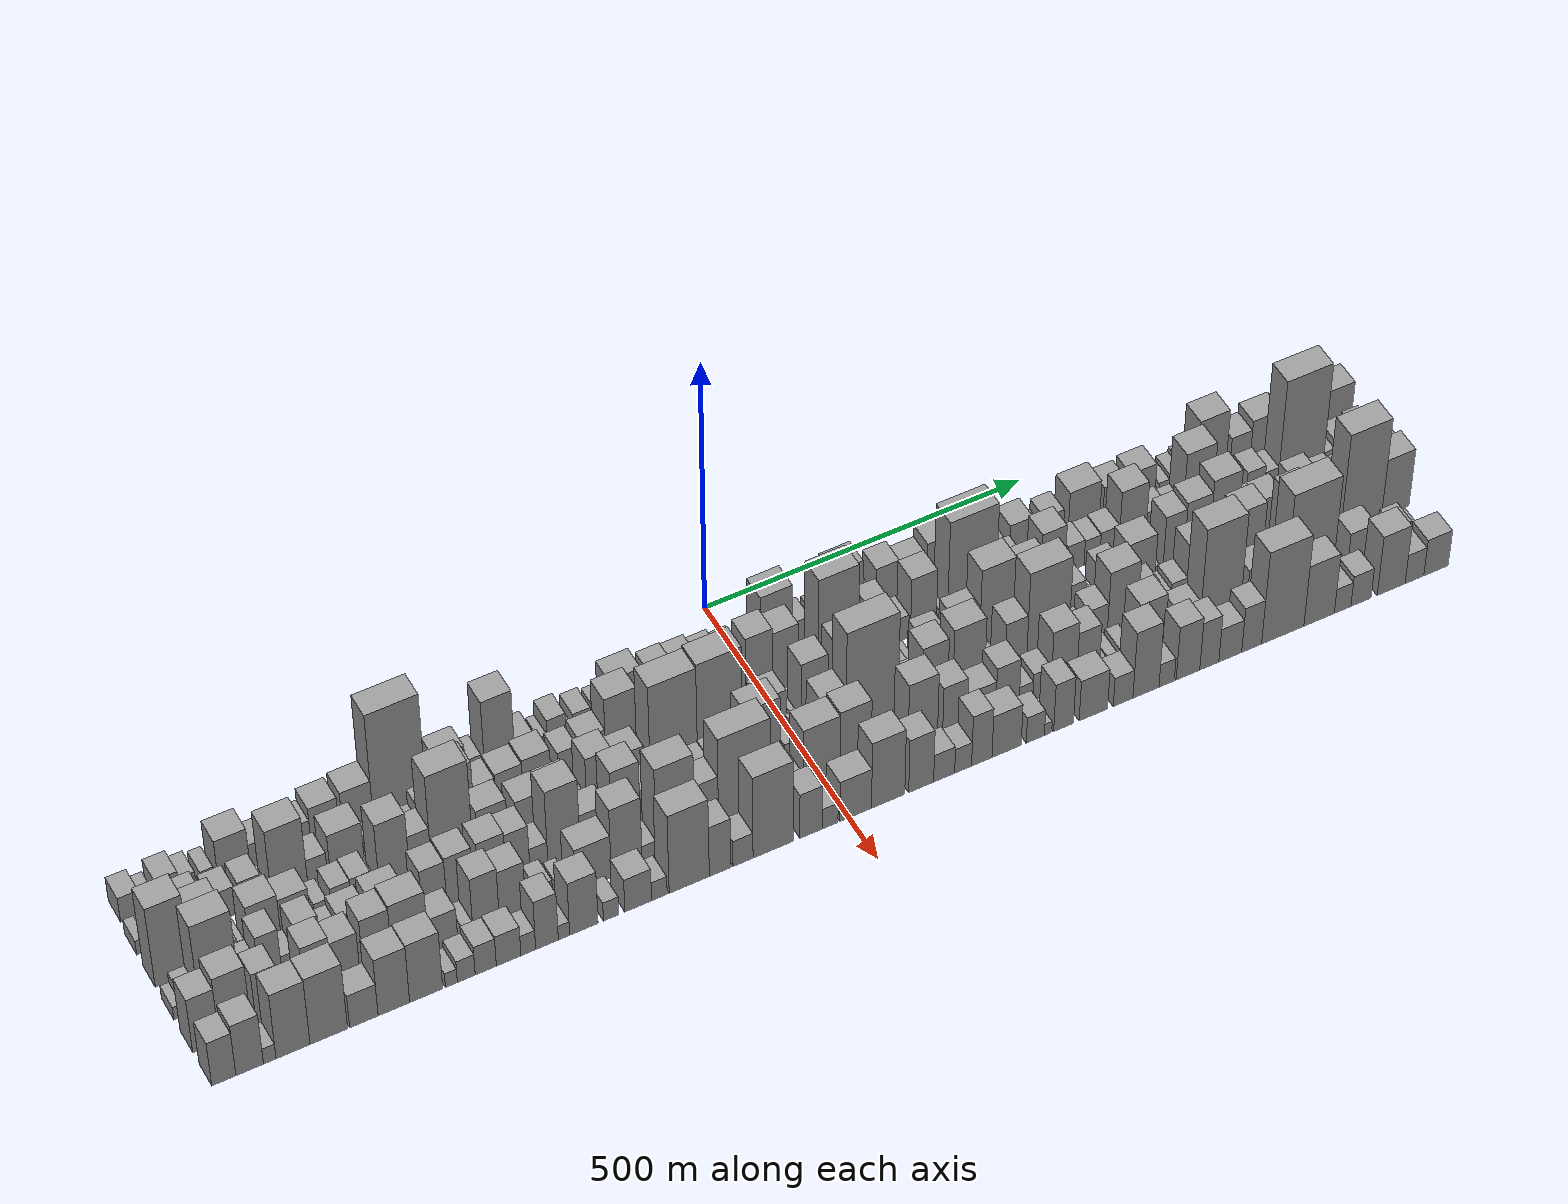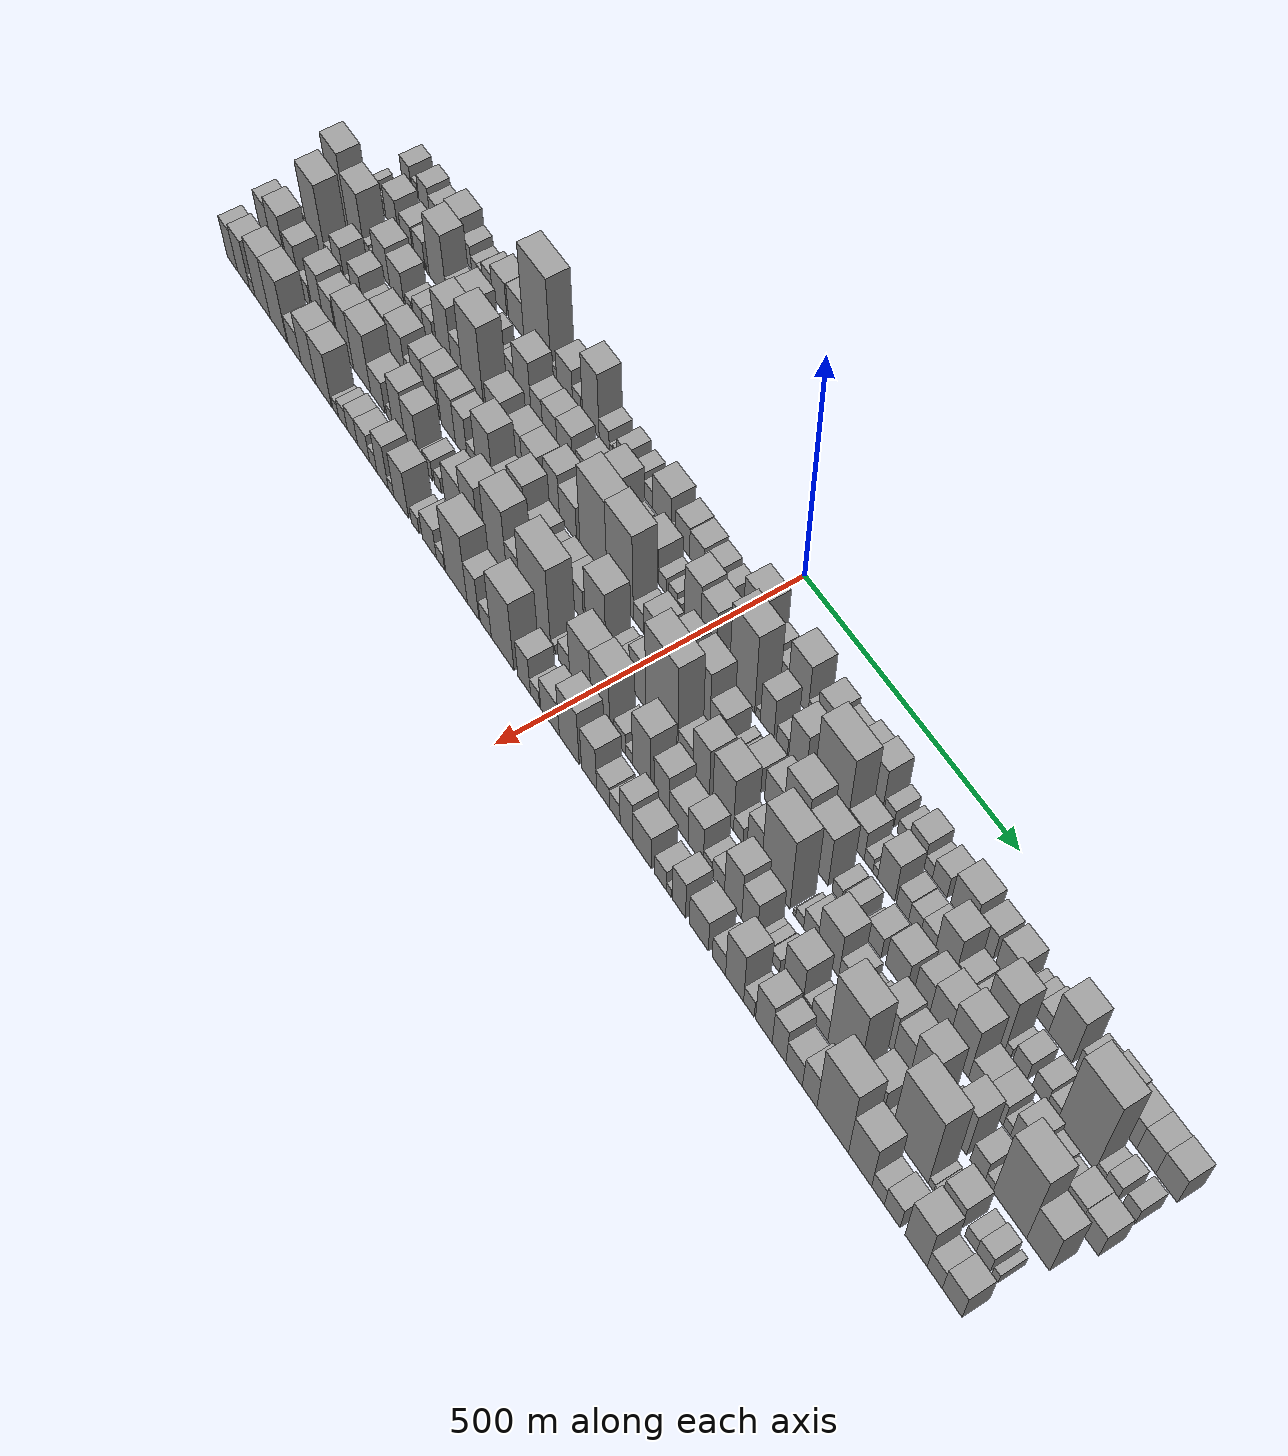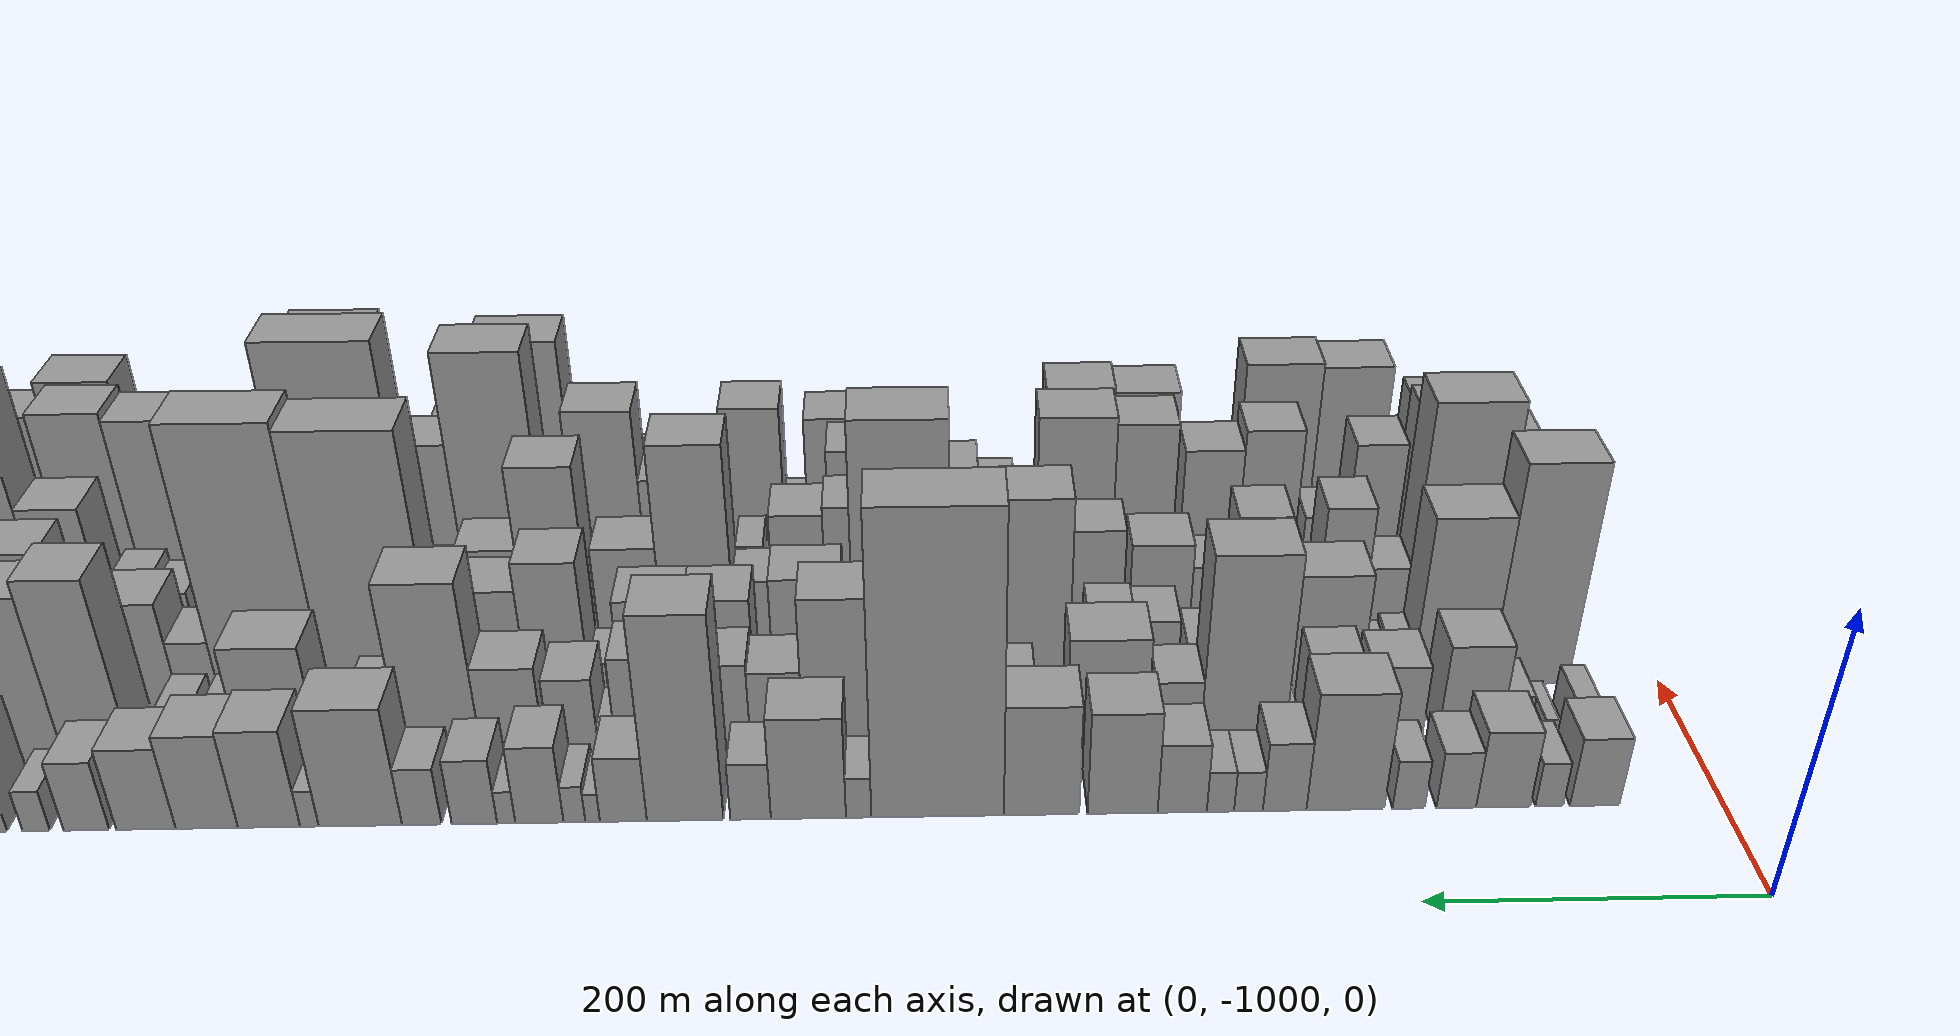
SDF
<sdf version="1.6">
 <world name="default">
  <scene>
   <sky><clouds><speed>12</speed></clouds></sky>
   <ambient>0.4 0.4 0.4 1</ambient>
   <background>0.7 0.7 0.7 1</background>
   <shadows>1</shadows>
  </scene>
  <gravity>0 0 -9.8066</gravity>
  <magnetic_field>6e-06 2.3e-05 -4.2e-05</magnetic_field>
  <physics default="0" name="default_physics" type="ode">
   <ode>
    <solver>
     <type>quick</type>
     <iters>10</iters>
     <sor>1.0</sor>
     <use_dynamic_moi_rescaling>0</use_dynamic_moi_rescaling>
    </solver>
    <constraints>
     <cfm>0</cfm>
     <erp>0.2</erp>
     <contact_max_correcting_vel>100</contact_max_correcting_vel>
     <contact_surface_layer>0.001</contact_surface_layer>
    </constraints>
   </ode>
   <max_step_size>0.004</max_step_size>
   <real_time_factor>1</real_time_factor>
   <real_time_update_rate>250</real_time_update_rate>
  </physics>
  <light name="sun" type="directional">
   <pose>0 0 10 0 0 0</pose>
   <diffuse>0.8 0.8 0.8 1</diffuse>
   <specular>0.2 0.2 0.2 1</specular>
   <attenuation>
    <range>1000</range>
    <constant>0.9</constant>
    <linear>0.01</linear>
    <quadratic>0.001</quadratic>
   </attenuation>
   <direction>-0.5 0.1 -0.9</direction>
  </light>
  <model name="building_1">
   <static>1</static>
   <pose>100.0000 -922.0106 0 0.000000 0.000000 0.000000</pose>
   <link name="link">
    <pose>0 0 25.50 0 0 0</pose>
    <collision name="collision"><geometry><box><size>40.0000 29.9787 51.0000</size></box></geometry></collision>
    <visual name="visual">
     <cast_shadows>0</cast_shadows>
     <geometry><box><size>40.0000 29.9787 51.0000</size></box></geometry>
     <material>
      <script>
       <uri>model://grey_wall/materials/scripts</uri>
       <uri>model://grey_wall/materials/textures</uri>
       <name>vrc/grey_wall</name>
      </script>
     </material>
    </visual>
   </link>
  </model>
  <model name="building_2">
   <static>1</static>
   <pose>100.0000 -894.5773 0 0.000000 0.000000 0.000000</pose>
   <link name="link">
    <pose>0 0 16.50 0 0 0</pose>
    <collision name="collision"><geometry><box><size>40.0000 16.8880 33.0000</size></box></geometry></collision>
    <visual name="visual">
     <cast_shadows>0</cast_shadows>
     <geometry><box><size>40.0000 16.8880 33.0000</size></box></geometry>
     <material>
      <script>
       <uri>model://grey_wall/materials/scripts</uri>
       <uri>model://grey_wall/materials/textures</uri>
       <name>vrc/grey_wall</name>
      </script>
     </material>
    </visual>
   </link>
  </model>
  <model name="building_3">
   <static>1</static>
   <pose>100.0000 -866.7093 0 0.000000 0.000000 0.000000</pose>
   <link name="link">
    <pose>0 0 28.50 0 0 0</pose>
    <collision name="collision"><geometry><box><size>40.0000 32.8479 57.0000</size></box></geometry></collision>
    <visual name="visual">
     <cast_shadows>0</cast_shadows>
     <geometry><box><size>40.0000 32.8479 57.0000</size></box></geometry>
     <material>
      <script>
       <uri>model://grey_wall/materials/scripts</uri>
       <uri>model://grey_wall/materials/textures</uri>
       <name>vrc/grey_wall</name>
      </script>
     </material>
    </visual>
   </link>
  </model>
  <model name="building_4">
   <static>1</static>
   <pose>100.0000 -838.2878 0 0.000000 0.000000 0.000000</pose>
   <link name="link">
    <pose>0 0 21.00 0 0 0</pose>
    <collision name="collision"><geometry><box><size>40.0000 23.9951 42.0000</size></box></geometry></collision>
    <visual name="visual">
     <cast_shadows>0</cast_shadows>
     <geometry><box><size>40.0000 23.9951 42.0000</size></box></geometry>
     <material>
      <script>
       <uri>model://grey_wall/materials/scripts</uri>
       <uri>model://grey_wall/materials/textures</uri>
       <name>vrc/grey_wall</name>
      </script>
     </material>
    </visual>
   </link>
  </model>
  <model name="building_5">
   <static>1</static>
   <pose>100.0000 -809.5649 0 0.000000 0.000000 0.000000</pose>
   <link name="link">
    <pose>0 0 18.00 0 0 0</pose>
    <collision name="collision"><geometry><box><size>40.0000 19.4507 36.0000</size></box></geometry></collision>
    <visual name="visual">
     <cast_shadows>0</cast_shadows>
     <geometry><box><size>40.0000 19.4507 36.0000</size></box></geometry>
     <material>
      <script>
       <uri>model://grey_wall/materials/scripts</uri>
       <uri>model://grey_wall/materials/textures</uri>
       <name>vrc/grey_wall</name>
      </script>
     </material>
    </visual>
   </link>
  </model>
  <model name="building_6">
   <static>1</static>
   <pose>100.0000 -771.3795 0 0.000000 0.000000 0.000000</pose>
   <link name="link">
    <pose>0 0 43.50 0 0 0</pose>
    <collision name="collision"><geometry><box><size>40.0000 46.9200 87.0000</size></box></geometry></collision>
    <visual name="visual">
     <cast_shadows>0</cast_shadows>
     <geometry><box><size>40.0000 46.9200 87.0000</size></box></geometry>
     <material>
      <script>
       <uri>model://grey_wall/materials/scripts</uri>
       <uri>model://grey_wall/materials/textures</uri>
       <name>vrc/grey_wall</name>
      </script>
     </material>
    </visual>
   </link>
  </model>
  <model name="building_7">
   <static>1</static>
   <pose>100.0000 -734.8246 0 0.000000 0.000000 0.000000</pose>
   <link name="link">
    <pose>0 0 25.50 0 0 0</pose>
    <collision name="collision"><geometry><box><size>40.0000 26.1900 51.0000</size></box></geometry></collision>
    <visual name="visual">
     <cast_shadows>0</cast_shadows>
     <geometry><box><size>40.0000 26.1900 51.0000</size></box></geometry>
     <material>
      <script>
       <uri>model://grey_wall/materials/scripts</uri>
       <uri>model://grey_wall/materials/textures</uri>
       <name>vrc/grey_wall</name>
      </script>
     </material>
    </visual>
   </link>
  </model>
  <model name="building_8">
   <static>1</static>
   <pose>100.0000 -713.0658 0 0.000000 0.000000 0.000000</pose>
   <link name="link">
    <pose>0 0 15.00 0 0 0</pose>
    <collision name="collision"><geometry><box><size>40.0000 17.3274 30.0000</size></box></geometry></collision>
    <visual name="visual">
     <cast_shadows>0</cast_shadows>
     <geometry><box><size>40.0000 17.3274 30.0000</size></box></geometry>
     <material>
      <script>
       <uri>model://grey_wall/materials/scripts</uri>
       <uri>model://grey_wall/materials/textures</uri>
       <name>vrc/grey_wall</name>
      </script>
     </material>
    </visual>
   </link>
  </model>
  <model name="building_9">
   <static>1</static>
   <pose>100.0000 -696.1878 0 0.000000 0.000000 0.000000</pose>
   <link name="link">
    <pose>0 0 15.00 0 0 0</pose>
    <collision name="collision"><geometry><box><size>40.0000 16.4287 30.0000</size></box></geometry></collision>
    <visual name="visual">
     <cast_shadows>0</cast_shadows>
     <geometry><box><size>40.0000 16.4287 30.0000</size></box></geometry>
     <material>
      <script>
       <uri>model://grey_wall/materials/scripts</uri>
       <uri>model://grey_wall/materials/textures</uri>
       <name>vrc/grey_wall</name>
      </script>
     </material>
    </visual>
   </link>
  </model>
  <model name="building_10">
   <static>1</static>
   <pose>100.0000 -673.2192 0 0.000000 0.000000 0.000000</pose>
   <link name="link">
    <pose>0 0 25.50 0 0 0</pose>
    <collision name="collision"><geometry><box><size>40.0000 29.5085 51.0000</size></box></geometry></collision>
    <visual name="visual">
     <cast_shadows>0</cast_shadows>
     <geometry><box><size>40.0000 29.5085 51.0000</size></box></geometry>
     <material>
      <script>
       <uri>model://grey_wall/materials/scripts</uri>
       <uri>model://grey_wall/materials/textures</uri>
       <name>vrc/grey_wall</name>
      </script>
     </material>
    </visual>
   </link>
  </model>
  <model name="building_11">
   <static>1</static>
   <pose>100.0000 -637.4435 0 0.000000 0.000000 0.000000</pose>
   <link name="link">
    <pose>0 0 37.50 0 0 0</pose>
    <collision name="collision"><geometry><box><size>40.0000 42.0427 75.0000</size></box></geometry></collision>
    <visual name="visual">
     <cast_shadows>0</cast_shadows>
     <geometry><box><size>40.0000 42.0427 75.0000</size></box></geometry>
     <material>
      <script>
       <uri>model://grey_wall/materials/scripts</uri>
       <uri>model://grey_wall/materials/textures</uri>
       <name>vrc/grey_wall</name>
      </script>
     </material>
    </visual>
   </link>
  </model>
  <model name="building_12">
   <static>1</static>
   <pose>100.0000 -588.8758 0 0.000000 0.000000 0.000000</pose>
   <link name="link">
    <pose>0 0 40.50 0 0 0</pose>
    <collision name="collision"><geometry><box><size>40.0000 45.0928 81.0000</size></box></geometry></collision>
    <visual name="visual">
     <cast_shadows>0</cast_shadows>
     <geometry><box><size>40.0000 45.0928 81.0000</size></box></geometry>
     <material>
      <script>
       <uri>model://grey_wall/materials/scripts</uri>
       <uri>model://grey_wall/materials/textures</uri>
       <name>vrc/grey_wall</name>
      </script>
     </material>
    </visual>
   </link>
  </model>
  <model name="building_13">
   <static>1</static>
   <pose>100.0000 -526.7478 0 0.000000 0.000000 0.000000</pose>
   <link name="link">
    <pose>0 0 109.50 0 0 0</pose>
    <collision name="collision"><geometry><box><size>40.0000 79.1632 219.0000</size></box></geometry></collision>
    <visual name="visual">
     <cast_shadows>0</cast_shadows>
     <geometry><box><size>40.0000 79.1632 219.0000</size></box></geometry>
     <material>
      <script>
       <uri>model://grey_wall/materials/scripts</uri>
       <uri>model://grey_wall/materials/textures</uri>
       <name>vrc/grey_wall</name>
      </script>
     </material>
    </visual>
   </link>
  </model>
  <model name="building_14">
   <static>1</static>
   <pose>100.0000 -479.6001 0 0.000000 0.000000 0.000000</pose>
   <link name="link">
    <pose>0 0 15.00 0 0 0</pose>
    <collision name="collision"><geometry><box><size>40.0000 15.1322 30.0000</size></box></geometry></collision>
    <visual name="visual">
     <cast_shadows>0</cast_shadows>
     <geometry><box><size>40.0000 15.1322 30.0000</size></box></geometry>
     <material>
      <script>
       <uri>model://grey_wall/materials/scripts</uri>
       <uri>model://grey_wall/materials/textures</uri>
       <name>vrc/grey_wall</name>
      </script>
     </material>
    </visual>
   </link>
  </model>
  <model name="building_15">
   <static>1</static>
   <pose>100.0000 -449.6756 0 0.000000 0.000000 0.000000</pose>
   <link name="link">
    <pose>0 0 37.50 0 0 0</pose>
    <collision name="collision"><geometry><box><size>40.0000 44.7167 75.0000</size></box></geometry></collision>
    <visual name="visual">
     <cast_shadows>0</cast_shadows>
     <geometry><box><size>40.0000 44.7167 75.0000</size></box></geometry>
     <material>
      <script>
       <uri>model://grey_wall/materials/scripts</uri>
       <uri>model://grey_wall/materials/textures</uri>
       <name>vrc/grey_wall</name>
      </script>
     </material>
    </visual>
   </link>
  </model>
  <model name="building_16">
   <static>1</static>
   <pose>100.0000 -415.2296 0 0.000000 0.000000 0.000000</pose>
   <link name="link">
    <pose>0 0 21.00 0 0 0</pose>
    <collision name="collision"><geometry><box><size>40.0000 24.1753 42.0000</size></box></geometry></collision>
    <visual name="visual">
     <cast_shadows>0</cast_shadows>
     <geometry><box><size>40.0000 24.1753 42.0000</size></box></geometry>
     <material>
      <script>
       <uri>model://grey_wall/materials/scripts</uri>
       <uri>model://grey_wall/materials/textures</uri>
       <name>vrc/grey_wall</name>
      </script>
     </material>
    </visual>
   </link>
  </model>
  <model name="building_17">
   <static>1</static>
   <pose>100.0000 -376.3590 0 0.000000 0.000000 0.000000</pose>
   <link name="link">
    <pose>0 0 75.00 0 0 0</pose>
    <collision name="collision"><geometry><box><size>40.0000 45.5659 150.0000</size></box></geometry></collision>
    <visual name="visual">
     <cast_shadows>0</cast_shadows>
     <geometry><box><size>40.0000 45.5659 150.0000</size></box></geometry>
     <material>
      <script>
       <uri>model://grey_wall/materials/scripts</uri>
       <uri>model://grey_wall/materials/textures</uri>
       <name>vrc/grey_wall</name>
      </script>
     </material>
    </visual>
   </link>
  </model>
  <model name="building_18">
   <static>1</static>
   <pose>100.0000 -339.6521 0 0.000000 0.000000 0.000000</pose>
   <link name="link">
    <pose>0 0 24.00 0 0 0</pose>
    <collision name="collision"><geometry><box><size>40.0000 27.8479 48.0000</size></box></geometry></collision>
    <visual name="visual">
     <cast_shadows>0</cast_shadows>
     <geometry><box><size>40.0000 27.8479 48.0000</size></box></geometry>
     <material>
      <script>
       <uri>model://grey_wall/materials/scripts</uri>
       <uri>model://grey_wall/materials/textures</uri>
       <name>vrc/grey_wall</name>
      </script>
     </material>
    </visual>
   </link>
  </model>
  <model name="building_19">
   <static>1</static>
   <pose>100.0000 -321.3916 0 0.000000 0.000000 0.000000</pose>
   <link name="link">
    <pose>0 0 10.50 0 0 0</pose>
    <collision name="collision"><geometry><box><size>40.0000 8.6731 21.0000</size></box></geometry></collision>
    <visual name="visual">
     <cast_shadows>0</cast_shadows>
     <geometry><box><size>40.0000 8.6731 21.0000</size></box></geometry>
     <material>
      <script>
       <uri>model://grey_wall/materials/scripts</uri>
       <uri>model://grey_wall/materials/textures</uri>
       <name>vrc/grey_wall</name>
      </script>
     </material>
    </visual>
   </link>
  </model>
  <model name="building_20">
   <static>1</static>
   <pose>100.0000 -310.6062 0 0.000000 0.000000 0.000000</pose>
   <link name="link">
    <pose>0 0 13.50 0 0 0</pose>
    <collision name="collision"><geometry><box><size>40.0000 12.8976 27.0000</size></box></geometry></collision>
    <visual name="visual">
     <cast_shadows>0</cast_shadows>
     <geometry><box><size>40.0000 12.8976 27.0000</size></box></geometry>
     <material>
      <script>
       <uri>model://grey_wall/materials/scripts</uri>
       <uri>model://grey_wall/materials/textures</uri>
       <name>vrc/grey_wall</name>
      </script>
     </material>
    </visual>
   </link>
  </model>
  <model name="building_21">
   <static>1</static>
   <pose>100.0000 -289.8967 0 0.000000 0.000000 0.000000</pose>
   <link name="link">
    <pose>0 0 28.50 0 0 0</pose>
    <collision name="collision"><geometry><box><size>40.0000 28.5214 57.0000</size></box></geometry></collision>
    <visual name="visual">
     <cast_shadows>0</cast_shadows>
     <geometry><box><size>40.0000 28.5214 57.0000</size></box></geometry>
     <material>
      <script>
       <uri>model://grey_wall/materials/scripts</uri>
       <uri>model://grey_wall/materials/textures</uri>
       <name>vrc/grey_wall</name>
      </script>
     </material>
    </visual>
   </link>
  </model>
  <model name="building_22">
   <static>1</static>
   <pose>100.0000 -270.2355 0 0.000000 0.000000 0.000000</pose>
   <link name="link">
    <pose>0 0 12.00 0 0 0</pose>
    <collision name="collision"><geometry><box><size>40.0000 10.8011 24.0000</size></box></geometry></collision>
    <visual name="visual">
     <cast_shadows>0</cast_shadows>
     <geometry><box><size>40.0000 10.8011 24.0000</size></box></geometry>
     <material>
      <script>
       <uri>model://grey_wall/materials/scripts</uri>
       <uri>model://grey_wall/materials/textures</uri>
       <name>vrc/grey_wall</name>
      </script>
     </material>
    </visual>
   </link>
  </model>
  <model name="building_23">
   <static>1</static>
   <pose>100.0000 -251.3677 0 0.000000 0.000000 0.000000</pose>
   <link name="link">
    <pose>0 0 24.00 0 0 0</pose>
    <collision name="collision"><geometry><box><size>40.0000 26.9344 48.0000</size></box></geometry></collision>
    <visual name="visual">
     <cast_shadows>0</cast_shadows>
     <geometry><box><size>40.0000 26.9344 48.0000</size></box></geometry>
     <material>
      <script>
       <uri>model://grey_wall/materials/scripts</uri>
       <uri>model://grey_wall/materials/textures</uri>
       <name>vrc/grey_wall</name>
      </script>
     </material>
    </visual>
   </link>
  </model>
  <model name="building_24">
   <static>1</static>
   <pose>100.0000 -220.2358 0 0.000000 0.000000 0.000000</pose>
   <link name="link">
    <pose>0 0 21.00 0 0 0</pose>
    <collision name="collision"><geometry><box><size>40.0000 23.3294 42.0000</size></box></geometry></collision>
    <visual name="visual">
     <cast_shadows>0</cast_shadows>
     <geometry><box><size>40.0000 23.3294 42.0000</size></box></geometry>
     <material>
      <script>
       <uri>model://grey_wall/materials/scripts</uri>
       <uri>model://grey_wall/materials/textures</uri>
       <name>vrc/grey_wall</name>
      </script>
     </material>
    </visual>
   </link>
  </model>
  <model name="building_25">
   <static>1</static>
   <pose>100.0000 -183.9872 0 0.000000 0.000000 0.000000</pose>
   <link name="link">
    <pose>0 0 43.50 0 0 0</pose>
    <collision name="collision"><geometry><box><size>40.0000 49.1678 87.0000</size></box></geometry></collision>
    <visual name="visual">
     <cast_shadows>0</cast_shadows>
     <geometry><box><size>40.0000 49.1678 87.0000</size></box></geometry>
     <material>
      <script>
       <uri>model://grey_wall/materials/scripts</uri>
       <uri>model://grey_wall/materials/textures</uri>
       <name>vrc/grey_wall</name>
      </script>
     </material>
    </visual>
   </link>
  </model>
  <model name="building_26">
   <static>1</static>
   <pose>100.0000 -153.9089 0 0.000000 0.000000 0.000000</pose>
   <link name="link">
    <pose>0 0 13.50 0 0 0</pose>
    <collision name="collision"><geometry><box><size>40.0000 10.9887 27.0000</size></box></geometry></collision>
    <visual name="visual">
     <cast_shadows>0</cast_shadows>
     <geometry><box><size>40.0000 10.9887 27.0000</size></box></geometry>
     <material>
      <script>
       <uri>model://grey_wall/materials/scripts</uri>
       <uri>model://grey_wall/materials/textures</uri>
       <name>vrc/grey_wall</name>
      </script>
     </material>
    </visual>
   </link>
  </model>
  <model name="building_27">
   <static>1</static>
   <pose>100.0000 -130.0910 0 0.000000 0.000000 0.000000</pose>
   <link name="link">
    <pose>0 0 36.00 0 0 0</pose>
    <collision name="collision"><geometry><box><size>40.0000 36.6471 72.0000</size></box></geometry></collision>
    <visual name="visual">
     <cast_shadows>0</cast_shadows>
     <geometry><box><size>40.0000 36.6471 72.0000</size></box></geometry>
     <material>
      <script>
       <uri>model://grey_wall/materials/scripts</uri>
       <uri>model://grey_wall/materials/textures</uri>
       <name>vrc/grey_wall</name>
      </script>
     </material>
    </visual>
   </link>
  </model>
  <model name="building_28">
   <static>1</static>
   <pose>100.0000 -93.4627 0 0.000000 0.000000 0.000000</pose>
   <link name="link">
    <pose>0 0 34.50 0 0 0</pose>
    <collision name="collision"><geometry><box><size>40.0000 36.6096 69.0000</size></box></geometry></collision>
    <visual name="visual">
     <cast_shadows>0</cast_shadows>
     <geometry><box><size>40.0000 36.6096 69.0000</size></box></geometry>
     <material>
      <script>
       <uri>model://grey_wall/materials/scripts</uri>
       <uri>model://grey_wall/materials/textures</uri>
       <name>vrc/grey_wall</name>
      </script>
     </material>
    </visual>
   </link>
  </model>
  <model name="building_29">
   <static>1</static>
   <pose>100.0000 -57.6574 0 0.000000 0.000000 0.000000</pose>
   <link name="link">
    <pose>0 0 30.00 0 0 0</pose>
    <collision name="collision"><geometry><box><size>40.0000 35.0009 60.0000</size></box></geometry></collision>
    <visual name="visual">
     <cast_shadows>0</cast_shadows>
     <geometry><box><size>40.0000 35.0009 60.0000</size></box></geometry>
     <material>
      <script>
       <uri>model://grey_wall/materials/scripts</uri>
       <uri>model://grey_wall/materials/textures</uri>
       <name>vrc/grey_wall</name>
      </script>
     </material>
    </visual>
   </link>
  </model>
  <model name="building_30">
   <static>1</static>
   <pose>100.0000 -22.7668 0 0.000000 0.000000 0.000000</pose>
   <link name="link">
    <pose>0 0 25.50 0 0 0</pose>
    <collision name="collision"><geometry><box><size>40.0000 26.7801 51.0000</size></box></geometry></collision>
    <visual name="visual">
     <cast_shadows>0</cast_shadows>
     <geometry><box><size>40.0000 26.7801 51.0000</size></box></geometry>
     <material>
      <script>
       <uri>model://grey_wall/materials/scripts</uri>
       <uri>model://grey_wall/materials/textures</uri>
       <name>vrc/grey_wall</name>
      </script>
     </material>
    </visual>
   </link>
  </model>
  <model name="building_31">
   <static>1</static>
   <pose>100.0000 6.6735 0 0.000000 0.000000 0.000000</pose>
   <link name="link">
    <pose>0 0 15.00 0 0 0</pose>
    <collision name="collision"><geometry><box><size>40.0000 16.1005 30.0000</size></box></geometry></collision>
    <visual name="visual">
     <cast_shadows>0</cast_shadows>
     <geometry><box><size>40.0000 16.1005 30.0000</size></box></geometry>
     <material>
      <script>
       <uri>model://grey_wall/materials/scripts</uri>
       <uri>model://grey_wall/materials/textures</uri>
       <name>vrc/grey_wall</name>
      </script>
     </material>
    </visual>
   </link>
  </model>
  <model name="building_32">
   <static>1</static>
   <pose>100.0000 48.6049 0 0.000000 0.000000 0.000000</pose>
   <link name="link">
    <pose>0 0 66.00 0 0 0</pose>
    <collision name="collision"><geometry><box><size>40.0000 49.7623 132.0000</size></box></geometry></collision>
    <visual name="visual">
     <cast_shadows>0</cast_shadows>
     <geometry><box><size>40.0000 49.7623 132.0000</size></box></geometry>
     <material>
      <script>
       <uri>model://grey_wall/materials/scripts</uri>
       <uri>model://grey_wall/materials/textures</uri>
       <name>vrc/grey_wall</name>
      </script>
     </material>
    </visual>
   </link>
  </model>
  <model name="building_33">
   <static>1</static>
   <pose>100.0000 86.8813 0 0.000000 0.000000 0.000000</pose>
   <link name="link">
    <pose>0 0 25.50 0 0 0</pose>
    <collision name="collision"><geometry><box><size>40.0000 26.7904 51.0000</size></box></geometry></collision>
    <visual name="visual">
     <cast_shadows>0</cast_shadows>
     <geometry><box><size>40.0000 26.7904 51.0000</size></box></geometry>
     <material>
      <script>
       <uri>model://grey_wall/materials/scripts</uri>
       <uri>model://grey_wall/materials/textures</uri>
       <name>vrc/grey_wall</name>
      </script>
     </material>
    </visual>
   </link>
  </model>
  <model name="building_34">
   <static>1</static>
   <pose>100.0000 121.1763 0 0.000000 0.000000 0.000000</pose>
   <link name="link">
    <pose>0 0 24.00 0 0 0</pose>
    <collision name="collision"><geometry><box><size>40.0000 27.7996 48.0000</size></box></geometry></collision>
    <visual name="visual">
     <cast_shadows>0</cast_shadows>
     <geometry><box><size>40.0000 27.7996 48.0000</size></box></geometry>
     <material>
      <script>
       <uri>model://grey_wall/materials/scripts</uri>
       <uri>model://grey_wall/materials/textures</uri>
       <name>vrc/grey_wall</name>
      </script>
     </material>
    </visual>
   </link>
  </model>
  <model name="building_35">
   <static>1</static>
   <pose>100.0000 159.3019 0 0.000000 0.000000 0.000000</pose>
   <link name="link">
    <pose>0 0 61.50 0 0 0</pose>
    <collision name="collision"><geometry><box><size>40.0000 48.4516 123.0000</size></box></geometry></collision>
    <visual name="visual">
     <cast_shadows>0</cast_shadows>
     <geometry><box><size>40.0000 48.4516 123.0000</size></box></geometry>
     <material>
      <script>
       <uri>model://grey_wall/materials/scripts</uri>
       <uri>model://grey_wall/materials/textures</uri>
       <name>vrc/grey_wall</name>
      </script>
     </material>
    </visual>
   </link>
  </model>
  <model name="building_36">
   <static>1</static>
   <pose>100.0000 193.6291 0 0.000000 0.000000 0.000000</pose>
   <link name="link">
    <pose>0 0 19.50 0 0 0</pose>
    <collision name="collision"><geometry><box><size>40.0000 20.2027 39.0000</size></box></geometry></collision>
    <visual name="visual">
     <cast_shadows>0</cast_shadows>
     <geometry><box><size>40.0000 20.2027 39.0000</size></box></geometry>
     <material>
      <script>
       <uri>model://grey_wall/materials/scripts</uri>
       <uri>model://grey_wall/materials/textures</uri>
       <name>vrc/grey_wall</name>
      </script>
     </material>
    </visual>
   </link>
  </model>
  <model name="building_37">
   <static>1</static>
   <pose>100.0000 222.0039 0 0.000000 0.000000 0.000000</pose>
   <link name="link">
    <pose>0 0 46.50 0 0 0</pose>
    <collision name="collision"><geometry><box><size>40.0000 36.5468 93.0000</size></box></geometry></collision>
    <visual name="visual">
     <cast_shadows>0</cast_shadows>
     <geometry><box><size>40.0000 36.5468 93.0000</size></box></geometry>
     <material>
      <script>
       <uri>model://grey_wall/materials/scripts</uri>
       <uri>model://grey_wall/materials/textures</uri>
       <name>vrc/grey_wall</name>
      </script>
     </material>
    </visual>
   </link>
  </model>
  <model name="building_38">
   <static>1</static>
   <pose>100.0000 262.5701 0 0.000000 0.000000 0.000000</pose>
   <link name="link">
    <pose>0 0 39.00 0 0 0</pose>
    <collision name="collision"><geometry><box><size>40.0000 44.5857 78.0000</size></box></geometry></collision>
    <visual name="visual">
     <cast_shadows>0</cast_shadows>
     <geometry><box><size>40.0000 44.5857 78.0000</size></box></geometry>
     <material>
      <script>
       <uri>model://grey_wall/materials/scripts</uri>
       <uri>model://grey_wall/materials/textures</uri>
       <name>vrc/grey_wall</name>
      </script>
     </material>
    </visual>
   </link>
  </model>
  <model name="building_39">
   <static>1</static>
   <pose>100.0000 302.8785 0 0.000000 0.000000 0.000000</pose>
   <link name="link">
    <pose>0 0 51.00 0 0 0</pose>
    <collision name="collision"><geometry><box><size>40.0000 36.0310 102.0000</size></box></geometry></collision>
    <visual name="visual">
     <cast_shadows>0</cast_shadows>
     <geometry><box><size>40.0000 36.0310 102.0000</size></box></geometry>
     <material>
      <script>
       <uri>model://grey_wall/materials/scripts</uri>
       <uri>model://grey_wall/materials/textures</uri>
       <name>vrc/grey_wall</name>
      </script>
     </material>
    </visual>
   </link>
  </model>
  <model name="building_40">
   <static>1</static>
   <pose>100.0000 339.5356 0 0.000000 0.000000 0.000000</pose>
   <link name="link">
    <pose>0 0 57.00 0 0 0</pose>
    <collision name="collision"><geometry><box><size>40.0000 37.2832 114.0000</size></box></geometry></collision>
    <visual name="visual">
     <cast_shadows>0</cast_shadows>
     <geometry><box><size>40.0000 37.2832 114.0000</size></box></geometry>
     <material>
      <script>
       <uri>model://grey_wall/materials/scripts</uri>
       <uri>model://grey_wall/materials/textures</uri>
       <name>vrc/grey_wall</name>
      </script>
     </material>
    </visual>
   </link>
  </model>
  <model name="building_41">
   <static>1</static>
   <pose>100.0000 372.7177 0 0.000000 0.000000 0.000000</pose>
   <link name="link">
    <pose>0 0 22.50 0 0 0</pose>
    <collision name="collision"><geometry><box><size>40.0000 23.0812 45.0000</size></box></geometry></collision>
    <visual name="visual">
     <cast_shadows>0</cast_shadows>
     <geometry><box><size>40.0000 23.0812 45.0000</size></box></geometry>
     <material>
      <script>
       <uri>model://grey_wall/materials/scripts</uri>
       <uri>model://grey_wall/materials/textures</uri>
       <name>vrc/grey_wall</name>
      </script>
     </material>
    </visual>
   </link>
  </model>
  <model name="building_42">
   <static>1</static>
   <pose>100.0000 402.9499 0 0.000000 0.000000 0.000000</pose>
   <link name="link">
    <pose>0 0 18.00 0 0 0</pose>
    <collision name="collision"><geometry><box><size>40.0000 21.3832 36.0000</size></box></geometry></collision>
    <visual name="visual">
     <cast_shadows>0</cast_shadows>
     <geometry><box><size>40.0000 21.3832 36.0000</size></box></geometry>
     <material>
      <script>
       <uri>model://grey_wall/materials/scripts</uri>
       <uri>model://grey_wall/materials/textures</uri>
       <name>vrc/grey_wall</name>
      </script>
     </material>
    </visual>
   </link>
  </model>
  <model name="building_43">
   <static>1</static>
   <pose>100.0000 434.9707 0 0.000000 0.000000 0.000000</pose>
   <link name="link">
    <pose>0 0 34.50 0 0 0</pose>
    <collision name="collision"><geometry><box><size>40.0000 36.6584 69.0000</size></box></geometry></collision>
    <visual name="visual">
     <cast_shadows>0</cast_shadows>
     <geometry><box><size>40.0000 36.6584 69.0000</size></box></geometry>
     <material>
      <script>
       <uri>model://grey_wall/materials/scripts</uri>
       <uri>model://grey_wall/materials/textures</uri>
       <name>vrc/grey_wall</name>
      </script>
     </material>
    </visual>
   </link>
  </model>
  <model name="building_44">
   <static>1</static>
   <pose>100.0000 462.3307 0 0.000000 0.000000 0.000000</pose>
   <link name="link">
    <pose>0 0 18.00 0 0 0</pose>
    <collision name="collision"><geometry><box><size>40.0000 18.0616 36.0000</size></box></geometry></collision>
    <visual name="visual">
     <cast_shadows>0</cast_shadows>
     <geometry><box><size>40.0000 18.0616 36.0000</size></box></geometry>
     <material>
      <script>
       <uri>model://grey_wall/materials/scripts</uri>
       <uri>model://grey_wall/materials/textures</uri>
       <name>vrc/grey_wall</name>
      </script>
     </material>
    </visual>
   </link>
  </model>
  <model name="building_45">
   <static>1</static>
   <pose>100.0000 487.5318 0 0.000000 0.000000 0.000000</pose>
   <link name="link">
    <pose>0 0 28.50 0 0 0</pose>
    <collision name="collision"><geometry><box><size>40.0000 32.3405 57.0000</size></box></geometry></collision>
    <visual name="visual">
     <cast_shadows>0</cast_shadows>
     <geometry><box><size>40.0000 32.3405 57.0000</size></box></geometry>
     <material>
      <script>
       <uri>model://grey_wall/materials/scripts</uri>
       <uri>model://grey_wall/materials/textures</uri>
       <name>vrc/grey_wall</name>
      </script>
     </material>
    </visual>
   </link>
  </model>
  <model name="building_46">
   <static>1</static>
   <pose>100.0000 537.1779 0 0.000000 0.000000 0.000000</pose>
   <link name="link">
    <pose>0 0 43.50 0 0 0</pose>
    <collision name="collision"><geometry><box><size>40.0000 50.9516 87.0000</size></box></geometry></collision>
    <visual name="visual">
     <cast_shadows>0</cast_shadows>
     <geometry><box><size>40.0000 50.9516 87.0000</size></box></geometry>
     <material>
      <script>
       <uri>model://grey_wall/materials/scripts</uri>
       <uri>model://grey_wall/materials/textures</uri>
       <name>vrc/grey_wall</name>
      </script>
     </material>
    </visual>
   </link>
  </model>
  <model name="building_47">
   <static>1</static>
   <pose>100.0000 585.8582 0 0.000000 0.000000 0.000000</pose>
   <link name="link">
    <pose>0 0 34.50 0 0 0</pose>
    <collision name="collision"><geometry><box><size>40.0000 36.4090 69.0000</size></box></geometry></collision>
    <visual name="visual">
     <cast_shadows>0</cast_shadows>
     <geometry><box><size>40.0000 36.4090 69.0000</size></box></geometry>
     <material>
      <script>
       <uri>model://grey_wall/materials/scripts</uri>
       <uri>model://grey_wall/materials/textures</uri>
       <name>vrc/grey_wall</name>
      </script>
     </material>
    </visual>
   </link>
  </model>
  <model name="building_48">
   <static>1</static>
   <pose>100.0000 631.2782 0 0.000000 0.000000 0.000000</pose>
   <link name="link">
    <pose>0 0 37.50 0 0 0</pose>
    <collision name="collision"><geometry><box><size>40.0000 42.4311 75.0000</size></box></geometry></collision>
    <visual name="visual">
     <cast_shadows>0</cast_shadows>
     <geometry><box><size>40.0000 42.4311 75.0000</size></box></geometry>
     <material>
      <script>
       <uri>model://grey_wall/materials/scripts</uri>
       <uri>model://grey_wall/materials/textures</uri>
       <name>vrc/grey_wall</name>
      </script>
     </material>
    </visual>
   </link>
  </model>
  <model name="building_49">
   <static>1</static>
   <pose>100.0000 655.4993 0 0.000000 0.000000 0.000000</pose>
   <link name="link">
    <pose>0 0 7.50 0 0 0</pose>
    <collision name="collision"><geometry><box><size>40.0000 6.0109 15.0000</size></box></geometry></collision>
    <visual name="visual">
     <cast_shadows>0</cast_shadows>
     <geometry><box><size>40.0000 6.0109 15.0000</size></box></geometry>
     <material>
      <script>
       <uri>model://grey_wall/materials/scripts</uri>
       <uri>model://grey_wall/materials/textures</uri>
       <name>vrc/grey_wall</name>
      </script>
     </material>
    </visual>
   </link>
  </model>
  <model name="building_50">
   <static>1</static>
   <pose>100.0000 667.1177 0 0.000000 0.000000 0.000000</pose>
   <link name="link">
    <pose>0 0 15.00 0 0 0</pose>
    <collision name="collision"><geometry><box><size>40.0000 17.2259 30.0000</size></box></geometry></collision>
    <visual name="visual">
     <cast_shadows>0</cast_shadows>
     <geometry><box><size>40.0000 17.2259 30.0000</size></box></geometry>
     <material>
      <script>
       <uri>model://grey_wall/materials/scripts</uri>
       <uri>model://grey_wall/materials/textures</uri>
       <name>vrc/grey_wall</name>
      </script>
     </material>
    </visual>
   </link>
  </model>
  <model name="building_51">
   <static>1</static>
   <pose>100.0000 685.6328 0 0.000000 0.000000 0.000000</pose>
   <link name="link">
    <pose>0 0 19.50 0 0 0</pose>
    <collision name="collision"><geometry><box><size>40.0000 19.8044 39.0000</size></box></geometry></collision>
    <visual name="visual">
     <cast_shadows>0</cast_shadows>
     <geometry><box><size>40.0000 19.8044 39.0000</size></box></geometry>
     <material>
      <script>
       <uri>model://grey_wall/materials/scripts</uri>
       <uri>model://grey_wall/materials/textures</uri>
       <name>vrc/grey_wall</name>
      </script>
     </material>
    </visual>
   </link>
  </model>
  <model name="building_52">
   <static>1</static>
   <pose>100.0000 708.1960 0 0.000000 0.000000 0.000000</pose>
   <link name="link">
    <pose>0 0 24.00 0 0 0</pose>
    <collision name="collision"><geometry><box><size>40.0000 25.3219 48.0000</size></box></geometry></collision>
    <visual name="visual">
     <cast_shadows>0</cast_shadows>
     <geometry><box><size>40.0000 25.3219 48.0000</size></box></geometry>
     <material>
      <script>
       <uri>model://grey_wall/materials/scripts</uri>
       <uri>model://grey_wall/materials/textures</uri>
       <name>vrc/grey_wall</name>
      </script>
     </material>
    </visual>
   </link>
  </model>
  <model name="building_53">
   <static>1</static>
   <pose>100.0000 744.9061 0 0.000000 0.000000 0.000000</pose>
   <link name="link">
    <pose>0 0 63.00 0 0 0</pose>
    <collision name="collision"><geometry><box><size>40.0000 48.0984 126.0000</size></box></geometry></collision>
    <visual name="visual">
     <cast_shadows>0</cast_shadows>
     <geometry><box><size>40.0000 48.0984 126.0000</size></box></geometry>
     <material>
      <script>
       <uri>model://grey_wall/materials/scripts</uri>
       <uri>model://grey_wall/materials/textures</uri>
       <name>vrc/grey_wall</name>
      </script>
     </material>
    </visual>
   </link>
  </model>
  <model name="building_54">
   <static>1</static>
   <pose>100.0000 792.7015 0 0.000000 0.000000 0.000000</pose>
   <link name="link">
    <pose>0 0 31.50 0 0 0</pose>
    <collision name="collision"><geometry><box><size>40.0000 33.4924 63.0000</size></box></geometry></collision>
    <visual name="visual">
     <cast_shadows>0</cast_shadows>
     <geometry><box><size>40.0000 33.4924 63.0000</size></box></geometry>
     <material>
      <script>
       <uri>model://grey_wall/materials/scripts</uri>
       <uri>model://grey_wall/materials/textures</uri>
       <name>vrc/grey_wall</name>
      </script>
     </material>
    </visual>
   </link>
  </model>
  <model name="building_55">
   <static>1</static>
   <pose>100.0000 832.7824 0 0.000000 0.000000 0.000000</pose>
   <link name="link">
    <pose>0 0 40.50 0 0 0</pose>
    <collision name="collision"><geometry><box><size>40.0000 46.6694 81.0000</size></box></geometry></collision>
    <visual name="visual">
     <cast_shadows>0</cast_shadows>
     <geometry><box><size>40.0000 46.6694 81.0000</size></box></geometry>
     <material>
      <script>
       <uri>model://grey_wall/materials/scripts</uri>
       <uri>model://grey_wall/materials/textures</uri>
       <name>vrc/grey_wall</name>
      </script>
     </material>
    </visual>
   </link>
  </model>
  <model name="building_56">
   <static>1</static>
   <pose>100.0000 877.3833 0 0.000000 0.000000 0.000000</pose>
   <link name="link">
    <pose>0 0 37.50 0 0 0</pose>
    <collision name="collision"><geometry><box><size>40.0000 42.5324 75.0000</size></box></geometry></collision>
    <visual name="visual">
     <cast_shadows>0</cast_shadows>
     <geometry><box><size>40.0000 42.5324 75.0000</size></box></geometry>
     <material>
      <script>
       <uri>model://grey_wall/materials/scripts</uri>
       <uri>model://grey_wall/materials/textures</uri>
       <name>vrc/grey_wall</name>
      </script>
     </material>
    </visual>
   </link>
  </model>
  <model name="building_57">
   <static>1</static>
   <pose>100.0000 917.4022 0 0.000000 0.000000 0.000000</pose>
   <link name="link">
    <pose>0 0 37.50 0 0 0</pose>
    <collision name="collision"><geometry><box><size>40.0000 37.5054 75.0000</size></box></geometry></collision>
    <visual name="visual">
     <cast_shadows>0</cast_shadows>
     <geometry><box><size>40.0000 37.5054 75.0000</size></box></geometry>
     <material>
      <script>
       <uri>model://grey_wall/materials/scripts</uri>
       <uri>model://grey_wall/materials/textures</uri>
       <name>vrc/grey_wall</name>
      </script>
     </material>
    </visual>
   </link>
  </model>
  <model name="building_58">
   <static>1</static>
   <pose>100.0000 957.1171 0 0.000000 0.000000 0.000000</pose>
   <link name="link">
    <pose>0 0 39.00 0 0 0</pose>
    <collision name="collision"><geometry><box><size>40.0000 41.9244 78.0000</size></box></geometry></collision>
    <visual name="visual">
     <cast_shadows>0</cast_shadows>
     <geometry><box><size>40.0000 41.9244 78.0000</size></box></geometry>
     <material>
      <script>
       <uri>model://grey_wall/materials/scripts</uri>
       <uri>model://grey_wall/materials/textures</uri>
       <name>vrc/grey_wall</name>
      </script>
     </material>
    </visual>
   </link>
  </model>
  <model name="building_59">
   <static>1</static>
   <pose>160.0000 -932.4052 0 0.000000 0.000000 0.000000</pose>
   <link name="link">
    <pose>0 0 15.00 0 0 0</pose>
    <collision name="collision"><geometry><box><size>40.0000 15.1895 30.0000</size></box></geometry></collision>
    <visual name="visual">
     <cast_shadows>0</cast_shadows>
     <geometry><box><size>40.0000 15.1895 30.0000</size></box></geometry>
     <material>
      <script>
       <uri>model://grey_wall/materials/scripts</uri>
       <uri>model://grey_wall/materials/textures</uri>
       <name>vrc/grey_wall</name>
      </script>
     </material>
    </visual>
   </link>
  </model>
  <model name="building_60">
   <static>1</static>
   <pose>160.0000 -910.6646 0 0.000000 0.000000 0.000000</pose>
   <link name="link">
    <pose>0 0 9.00 0 0 0</pose>
    <collision name="collision"><geometry><box><size>40.0000 8.2917 18.0000</size></box></geometry></collision>
    <visual name="visual">
     <cast_shadows>0</cast_shadows>
     <geometry><box><size>40.0000 8.2917 18.0000</size></box></geometry>
     <material>
      <script>
       <uri>model://grey_wall/materials/scripts</uri>
       <uri>model://grey_wall/materials/textures</uri>
       <name>vrc/grey_wall</name>
      </script>
     </material>
    </visual>
   </link>
  </model>
  <model name="building_61">
   <static>1</static>
   <pose>160.0000 -888.4596 0 0.000000 0.000000 0.000000</pose>
   <link name="link">
    <pose>0 0 18.00 0 0 0</pose>
    <collision name="collision"><geometry><box><size>40.0000 18.1182 36.0000</size></box></geometry></collision>
    <visual name="visual">
     <cast_shadows>0</cast_shadows>
     <geometry><box><size>40.0000 18.1182 36.0000</size></box></geometry>
     <material>
      <script>
       <uri>model://grey_wall/materials/scripts</uri>
       <uri>model://grey_wall/materials/textures</uri>
       <name>vrc/grey_wall</name>
      </script>
     </material>
    </visual>
   </link>
  </model>
  <model name="building_62">
   <static>1</static>
   <pose>160.0000 -859.8028 0 0.000000 0.000000 0.000000</pose>
   <link name="link">
    <pose>0 0 37.50 0 0 0</pose>
    <collision name="collision"><geometry><box><size>40.0000 39.1955 75.0000</size></box></geometry></collision>
    <visual name="visual">
     <cast_shadows>0</cast_shadows>
     <geometry><box><size>40.0000 39.1955 75.0000</size></box></geometry>
     <material>
      <script>
       <uri>model://grey_wall/materials/scripts</uri>
       <uri>model://grey_wall/materials/textures</uri>
       <name>vrc/grey_wall</name>
      </script>
     </material>
    </visual>
   </link>
  </model>
  <model name="building_63">
   <static>1</static>
   <pose>160.0000 -812.5876 0 0.000000 0.000000 0.000000</pose>
   <link name="link">
    <pose>0 0 30.00 0 0 0</pose>
    <collision name="collision"><geometry><box><size>40.0000 35.2349 60.0000</size></box></geometry></collision>
    <visual name="visual">
     <cast_shadows>0</cast_shadows>
     <geometry><box><size>40.0000 35.2349 60.0000</size></box></geometry>
     <material>
      <script>
       <uri>model://grey_wall/materials/scripts</uri>
       <uri>model://grey_wall/materials/textures</uri>
       <name>vrc/grey_wall</name>
      </script>
     </material>
    </visual>
   </link>
  </model>
  <model name="building_64">
   <static>1</static>
   <pose>160.0000 -773.4200 0 0.000000 0.000000 0.000000</pose>
   <link name="link">
    <pose>0 0 31.50 0 0 0</pose>
    <collision name="collision"><geometry><box><size>40.0000 33.1002 63.0000</size></box></geometry></collision>
    <visual name="visual">
     <cast_shadows>0</cast_shadows>
     <geometry><box><size>40.0000 33.1002 63.0000</size></box></geometry>
     <material>
      <script>
       <uri>model://grey_wall/materials/scripts</uri>
       <uri>model://grey_wall/materials/textures</uri>
       <name>vrc/grey_wall</name>
      </script>
     </material>
    </visual>
   </link>
  </model>
  <model name="building_65">
   <static>1</static>
   <pose>160.0000 -748.5970 0 0.000000 0.000000 0.000000</pose>
   <link name="link">
    <pose>0 0 10.50 0 0 0</pose>
    <collision name="collision"><geometry><box><size>40.0000 8.5458 21.0000</size></box></geometry></collision>
    <visual name="visual">
     <cast_shadows>0</cast_shadows>
     <geometry><box><size>40.0000 8.5458 21.0000</size></box></geometry>
     <material>
      <script>
       <uri>model://grey_wall/materials/scripts</uri>
       <uri>model://grey_wall/materials/textures</uri>
       <name>vrc/grey_wall</name>
      </script>
     </material>
    </visual>
   </link>
  </model>
  <model name="building_66">
   <static>1</static>
   <pose>160.0000 -717.8331 0 0.000000 0.000000 0.000000</pose>
   <link name="link">
    <pose>0 0 72.00 0 0 0</pose>
    <collision name="collision"><geometry><box><size>40.0000 52.9821 144.0000</size></box></geometry></collision>
    <visual name="visual">
     <cast_shadows>0</cast_shadows>
     <geometry><box><size>40.0000 52.9821 144.0000</size></box></geometry>
     <material>
      <script>
       <uri>model://grey_wall/materials/scripts</uri>
       <uri>model://grey_wall/materials/textures</uri>
       <name>vrc/grey_wall</name>
      </script>
     </material>
    </visual>
   </link>
  </model>
  <model name="building_67">
   <static>1</static>
   <pose>160.0000 -676.6787 0 0.000000 0.000000 0.000000</pose>
   <link name="link">
    <pose>0 0 25.50 0 0 0</pose>
    <collision name="collision"><geometry><box><size>40.0000 29.3267 51.0000</size></box></geometry></collision>
    <visual name="visual">
     <cast_shadows>0</cast_shadows>
     <geometry><box><size>40.0000 29.3267 51.0000</size></box></geometry>
     <material>
      <script>
       <uri>model://grey_wall/materials/scripts</uri>
       <uri>model://grey_wall/materials/textures</uri>
       <name>vrc/grey_wall</name>
      </script>
     </material>
    </visual>
   </link>
  </model>
  <model name="building_68">
   <static>1</static>
   <pose>160.0000 -632.9793 0 0.000000 0.000000 0.000000</pose>
   <link name="link">
    <pose>0 0 42.00 0 0 0</pose>
    <collision name="collision"><geometry><box><size>40.0000 50.0722 84.0000</size></box></geometry></collision>
    <visual name="visual">
     <cast_shadows>0</cast_shadows>
     <geometry><box><size>40.0000 50.0722 84.0000</size></box></geometry>
     <material>
      <script>
       <uri>model://grey_wall/materials/scripts</uri>
       <uri>model://grey_wall/materials/textures</uri>
       <name>vrc/grey_wall</name>
      </script>
     </material>
    </visual>
   </link>
  </model>
  <model name="building_69">
   <static>1</static>
   <pose>160.0000 -595.7479 0 0.000000 0.000000 0.000000</pose>
   <link name="link">
    <pose>0 0 15.00 0 0 0</pose>
    <collision name="collision"><geometry><box><size>40.0000 16.3907 30.0000</size></box></geometry></collision>
    <visual name="visual">
     <cast_shadows>0</cast_shadows>
     <geometry><box><size>40.0000 16.3907 30.0000</size></box></geometry>
     <material>
      <script>
       <uri>model://grey_wall/materials/scripts</uri>
       <uri>model://grey_wall/materials/textures</uri>
       <name>vrc/grey_wall</name>
      </script>
     </material>
    </visual>
   </link>
  </model>
  <model name="building_70">
   <static>1</static>
   <pose>160.0000 -573.2545 0 0.000000 0.000000 0.000000</pose>
   <link name="link">
    <pose>0 0 27.00 0 0 0</pose>
    <collision name="collision"><geometry><box><size>40.0000 28.5960 54.0000</size></box></geometry></collision>
    <visual name="visual">
     <cast_shadows>0</cast_shadows>
     <geometry><box><size>40.0000 28.5960 54.0000</size></box></geometry>
     <material>
      <script>
       <uri>model://grey_wall/materials/scripts</uri>
       <uri>model://grey_wall/materials/textures</uri>
       <name>vrc/grey_wall</name>
      </script>
     </material>
    </visual>
   </link>
  </model>
  <model name="building_71">
   <static>1</static>
   <pose>160.0000 -547.1746 0 0.000000 0.000000 0.000000</pose>
   <link name="link">
    <pose>0 0 13.50 0 0 0</pose>
    <collision name="collision"><geometry><box><size>40.0000 11.5638 27.0000</size></box></geometry></collision>
    <visual name="visual">
     <cast_shadows>0</cast_shadows>
     <geometry><box><size>40.0000 11.5638 27.0000</size></box></geometry>
     <material>
      <script>
       <uri>model://grey_wall/materials/scripts</uri>
       <uri>model://grey_wall/materials/textures</uri>
       <name>vrc/grey_wall</name>
      </script>
     </material>
    </visual>
   </link>
  </model>
  <model name="building_72">
   <static>1</static>
   <pose>160.0000 -532.4217 0 0.000000 0.000000 0.000000</pose>
   <link name="link">
    <pose>0 0 15.00 0 0 0</pose>
    <collision name="collision"><geometry><box><size>40.0000 17.9421 30.0000</size></box></geometry></collision>
    <visual name="visual">
     <cast_shadows>0</cast_shadows>
     <geometry><box><size>40.0000 17.9421 30.0000</size></box></geometry>
     <material>
      <script>
       <uri>model://grey_wall/materials/scripts</uri>
       <uri>model://grey_wall/materials/textures</uri>
       <name>vrc/grey_wall</name>
      </script>
     </material>
    </visual>
   </link>
  </model>
  <model name="building_73">
   <static>1</static>
   <pose>160.0000 -507.1314 0 0.000000 0.000000 0.000000</pose>
   <link name="link">
    <pose>0 0 30.00 0 0 0</pose>
    <collision name="collision"><geometry><box><size>40.0000 32.6385 60.0000</size></box></geometry></collision>
    <visual name="visual">
     <cast_shadows>0</cast_shadows>
     <geometry><box><size>40.0000 32.6385 60.0000</size></box></geometry>
     <material>
      <script>
       <uri>model://grey_wall/materials/scripts</uri>
       <uri>model://grey_wall/materials/textures</uri>
       <name>vrc/grey_wall</name>
      </script>
     </material>
    </visual>
   </link>
  </model>
  <model name="building_74">
   <static>1</static>
   <pose>160.0000 -467.6088 0 0.000000 0.000000 0.000000</pose>
   <link name="link">
    <pose>0 0 58.50 0 0 0</pose>
    <collision name="collision"><geometry><box><size>40.0000 46.4066 117.0000</size></box></geometry></collision>
    <visual name="visual">
     <cast_shadows>0</cast_shadows>
     <geometry><box><size>40.0000 46.4066 117.0000</size></box></geometry>
     <material>
      <script>
       <uri>model://grey_wall/materials/scripts</uri>
       <uri>model://grey_wall/materials/textures</uri>
       <name>vrc/grey_wall</name>
      </script>
     </material>
    </visual>
   </link>
  </model>
  <model name="building_75">
   <static>1</static>
   <pose>160.0000 -428.1133 0 0.000000 0.000000 0.000000</pose>
   <link name="link">
    <pose>0 0 31.50 0 0 0</pose>
    <collision name="collision"><geometry><box><size>40.0000 32.5844 63.0000</size></box></geometry></collision>
    <visual name="visual">
     <cast_shadows>0</cast_shadows>
     <geometry><box><size>40.0000 32.5844 63.0000</size></box></geometry>
     <material>
      <script>
       <uri>model://grey_wall/materials/scripts</uri>
       <uri>model://grey_wall/materials/textures</uri>
       <name>vrc/grey_wall</name>
      </script>
     </material>
    </visual>
   </link>
  </model>
  <model name="building_76">
   <static>1</static>
   <pose>160.0000 -391.2754 0 0.000000 0.000000 0.000000</pose>
   <link name="link">
    <pose>0 0 34.50 0 0 0</pose>
    <collision name="collision"><geometry><box><size>40.0000 41.0915 69.0000</size></box></geometry></collision>
    <visual name="visual">
     <cast_shadows>0</cast_shadows>
     <geometry><box><size>40.0000 41.0915 69.0000</size></box></geometry>
     <material>
      <script>
       <uri>model://grey_wall/materials/scripts</uri>
       <uri>model://grey_wall/materials/textures</uri>
       <name>vrc/grey_wall</name>
      </script>
     </material>
    </visual>
   </link>
  </model>
  <model name="building_77">
   <static>1</static>
   <pose>160.0000 -349.5944 0 0.000000 0.000000 0.000000</pose>
   <link name="link">
    <pose>0 0 37.50 0 0 0</pose>
    <collision name="collision"><geometry><box><size>40.0000 42.2706 75.0000</size></box></geometry></collision>
    <visual name="visual">
     <cast_shadows>0</cast_shadows>
     <geometry><box><size>40.0000 42.2706 75.0000</size></box></geometry>
     <material>
      <script>
       <uri>model://grey_wall/materials/scripts</uri>
       <uri>model://grey_wall/materials/textures</uri>
       <name>vrc/grey_wall</name>
      </script>
     </material>
    </visual>
   </link>
  </model>
  <model name="building_78">
   <static>1</static>
   <pose>160.0000 -323.1259 0 0.000000 0.000000 0.000000</pose>
   <link name="link">
    <pose>0 0 12.00 0 0 0</pose>
    <collision name="collision"><geometry><box><size>40.0000 10.6664 24.0000</size></box></geometry></collision>
    <visual name="visual">
     <cast_shadows>0</cast_shadows>
     <geometry><box><size>40.0000 10.6664 24.0000</size></box></geometry>
     <material>
      <script>
       <uri>model://grey_wall/materials/scripts</uri>
       <uri>model://grey_wall/materials/textures</uri>
       <name>vrc/grey_wall</name>
      </script>
     </material>
    </visual>
   </link>
  </model>
  <model name="building_79">
   <static>1</static>
   <pose>160.0000 -302.6198 0 0.000000 0.000000 0.000000</pose>
   <link name="link">
    <pose>0 0 30.00 0 0 0</pose>
    <collision name="collision"><geometry><box><size>40.0000 30.3458 60.0000</size></box></geometry></collision>
    <visual name="visual">
     <cast_shadows>0</cast_shadows>
     <geometry><box><size>40.0000 30.3458 60.0000</size></box></geometry>
     <material>
      <script>
       <uri>model://grey_wall/materials/scripts</uri>
       <uri>model://grey_wall/materials/textures</uri>
       <name>vrc/grey_wall</name>
      </script>
     </material>
    </visual>
   </link>
  </model>
  <model name="building_80">
   <static>1</static>
   <pose>160.0000 -265.0038 0 0.000000 0.000000 0.000000</pose>
   <link name="link">
    <pose>0 0 34.50 0 0 0</pose>
    <collision name="collision"><geometry><box><size>40.0000 38.8863 69.0000</size></box></geometry></collision>
    <visual name="visual">
     <cast_shadows>0</cast_shadows>
     <geometry><box><size>40.0000 38.8863 69.0000</size></box></geometry>
     <material>
      <script>
       <uri>model://grey_wall/materials/scripts</uri>
       <uri>model://grey_wall/materials/textures</uri>
       <name>vrc/grey_wall</name>
      </script>
     </material>
    </visual>
   </link>
  </model>
  <model name="building_81">
   <static>1</static>
   <pose>160.0000 -221.2060 0 0.000000 0.000000 0.000000</pose>
   <link name="link">
    <pose>0 0 66.00 0 0 0</pose>
    <collision name="collision"><geometry><box><size>40.0000 48.7094 132.0000</size></box></geometry></collision>
    <visual name="visual">
     <cast_shadows>0</cast_shadows>
     <geometry><box><size>40.0000 48.7094 132.0000</size></box></geometry>
     <material>
      <script>
       <uri>model://grey_wall/materials/scripts</uri>
       <uri>model://grey_wall/materials/textures</uri>
       <name>vrc/grey_wall</name>
      </script>
     </material>
    </visual>
   </link>
  </model>
  <model name="building_82">
   <static>1</static>
   <pose>160.0000 -182.8963 0 0.000000 0.000000 0.000000</pose>
   <link name="link">
    <pose>0 0 25.50 0 0 0</pose>
    <collision name="collision"><geometry><box><size>40.0000 27.9101 51.0000</size></box></geometry></collision>
    <visual name="visual">
     <cast_shadows>0</cast_shadows>
     <geometry><box><size>40.0000 27.9101 51.0000</size></box></geometry>
     <material>
      <script>
       <uri>model://grey_wall/materials/scripts</uri>
       <uri>model://grey_wall/materials/textures</uri>
       <name>vrc/grey_wall</name>
      </script>
     </material>
    </visual>
   </link>
  </model>
  <model name="building_83">
   <static>1</static>
   <pose>160.0000 -157.7309 0 0.000000 0.000000 0.000000</pose>
   <link name="link">
    <pose>0 0 21.00 0 0 0</pose>
    <collision name="collision"><geometry><box><size>40.0000 22.4206 42.0000</size></box></geometry></collision>
    <visual name="visual">
     <cast_shadows>0</cast_shadows>
     <geometry><box><size>40.0000 22.4206 42.0000</size></box></geometry>
     <material>
      <script>
       <uri>model://grey_wall/materials/scripts</uri>
       <uri>model://grey_wall/materials/textures</uri>
       <name>vrc/grey_wall</name>
      </script>
     </material>
    </visual>
   </link>
  </model>
  <model name="building_84">
   <static>1</static>
   <pose>160.0000 -122.2274 0 0.000000 0.000000 0.000000</pose>
   <link name="link">
    <pose>0 0 43.50 0 0 0</pose>
    <collision name="collision"><geometry><box><size>40.0000 48.5863 87.0000</size></box></geometry></collision>
    <visual name="visual">
     <cast_shadows>0</cast_shadows>
     <geometry><box><size>40.0000 48.5863 87.0000</size></box></geometry>
     <material>
      <script>
       <uri>model://grey_wall/materials/scripts</uri>
       <uri>model://grey_wall/materials/textures</uri>
       <name>vrc/grey_wall</name>
      </script>
     </material>
    </visual>
   </link>
  </model>
  <model name="building_85">
   <static>1</static>
   <pose>160.0000 -87.8632 0 0.000000 0.000000 0.000000</pose>
   <link name="link">
    <pose>0 0 19.50 0 0 0</pose>
    <collision name="collision"><geometry><box><size>40.0000 20.1421 39.0000</size></box></geometry></collision>
    <visual name="visual">
     <cast_shadows>0</cast_shadows>
     <geometry><box><size>40.0000 20.1421 39.0000</size></box></geometry>
     <material>
      <script>
       <uri>model://grey_wall/materials/scripts</uri>
       <uri>model://grey_wall/materials/textures</uri>
       <name>vrc/grey_wall</name>
      </script>
     </material>
    </visual>
   </link>
  </model>
  <model name="building_86">
   <static>1</static>
   <pose>160.0000 -60.9558 0 0.000000 0.000000 0.000000</pose>
   <link name="link">
    <pose>0 0 19.50 0 0 0</pose>
    <collision name="collision"><geometry><box><size>40.0000 21.6727 39.0000</size></box></geometry></collision>
    <visual name="visual">
     <cast_shadows>0</cast_shadows>
     <geometry><box><size>40.0000 21.6727 39.0000</size></box></geometry>
     <material>
      <script>
       <uri>model://grey_wall/materials/scripts</uri>
       <uri>model://grey_wall/materials/textures</uri>
       <name>vrc/grey_wall</name>
      </script>
     </material>
    </visual>
   </link>
  </model>
  <model name="building_87">
   <static>1</static>
   <pose>160.0000 -45.2092 0 0.000000 0.000000 0.000000</pose>
   <link name="link">
    <pose>0 0 12.00 0 0 0</pose>
    <collision name="collision"><geometry><box><size>40.0000 9.8205 24.0000</size></box></geometry></collision>
    <visual name="visual">
     <cast_shadows>0</cast_shadows>
     <geometry><box><size>40.0000 9.8205 24.0000</size></box></geometry>
     <material>
      <script>
       <uri>model://grey_wall/materials/scripts</uri>
       <uri>model://grey_wall/materials/textures</uri>
       <name>vrc/grey_wall</name>
      </script>
     </material>
    </visual>
   </link>
  </model>
  <model name="building_88">
   <static>1</static>
   <pose>160.0000 -10.5048 0 0.000000 0.000000 0.000000</pose>
   <link name="link">
    <pose>0 0 69.00 0 0 0</pose>
    <collision name="collision"><geometry><box><size>40.0000 41.5882 138.0000</size></box></geometry></collision>
    <visual name="visual">
     <cast_shadows>0</cast_shadows>
     <geometry><box><size>40.0000 41.5882 138.0000</size></box></geometry>
     <material>
      <script>
       <uri>model://grey_wall/materials/scripts</uri>
       <uri>model://grey_wall/materials/textures</uri>
       <name>vrc/grey_wall</name>
      </script>
     </material>
    </visual>
   </link>
  </model>
  <model name="building_89">
   <static>1</static>
   <pose>160.0000 30.4153 0 0.000000 0.000000 0.000000</pose>
   <link name="link">
    <pose>0 0 63.00 0 0 0</pose>
    <collision name="collision"><geometry><box><size>40.0000 40.2521 126.0000</size></box></geometry></collision>
    <visual name="visual">
     <cast_shadows>0</cast_shadows>
     <geometry><box><size>40.0000 40.2521 126.0000</size></box></geometry>
     <material>
      <script>
       <uri>model://grey_wall/materials/scripts</uri>
       <uri>model://grey_wall/materials/textures</uri>
       <name>vrc/grey_wall</name>
      </script>
     </material>
    </visual>
   </link>
  </model>
  <model name="building_90">
   <static>1</static>
   <pose>160.0000 64.2063 0 0.000000 0.000000 0.000000</pose>
   <link name="link">
    <pose>0 0 15.00 0 0 0</pose>
    <collision name="collision"><geometry><box><size>40.0000 17.3297 30.0000</size></box></geometry></collision>
    <visual name="visual">
     <cast_shadows>0</cast_shadows>
     <geometry><box><size>40.0000 17.3297 30.0000</size></box></geometry>
     <material>
      <script>
       <uri>model://grey_wall/materials/scripts</uri>
       <uri>model://grey_wall/materials/textures</uri>
       <name>vrc/grey_wall</name>
      </script>
     </material>
    </visual>
   </link>
  </model>
  <model name="building_91">
   <static>1</static>
   <pose>160.0000 113.0793 0 0.000000 0.000000 0.000000</pose>
   <link name="link">
    <pose>0 0 99.00 0 0 0</pose>
    <collision name="collision"><geometry><box><size>40.0000 62.4163 198.0000</size></box></geometry></collision>
    <visual name="visual">
     <cast_shadows>0</cast_shadows>
     <geometry><box><size>40.0000 62.4163 198.0000</size></box></geometry>
     <material>
      <script>
       <uri>model://grey_wall/materials/scripts</uri>
       <uri>model://grey_wall/materials/textures</uri>
       <name>vrc/grey_wall</name>
      </script>
     </material>
    </visual>
   </link>
  </model>
  <model name="building_92">
   <static>1</static>
   <pose>160.0000 152.6669 0 0.000000 0.000000 0.000000</pose>
   <link name="link">
    <pose>0 0 12.00 0 0 0</pose>
    <collision name="collision"><geometry><box><size>40.0000 10.7589 24.0000</size></box></geometry></collision>
    <visual name="visual">
     <cast_shadows>0</cast_shadows>
     <geometry><box><size>40.0000 10.7589 24.0000</size></box></geometry>
     <material>
      <script>
       <uri>model://grey_wall/materials/scripts</uri>
       <uri>model://grey_wall/materials/textures</uri>
       <name>vrc/grey_wall</name>
      </script>
     </material>
    </visual>
   </link>
  </model>
  <model name="building_93">
   <static>1</static>
   <pose>160.0000 174.5098 0 0.000000 0.000000 0.000000</pose>
   <link name="link">
    <pose>0 0 51.00 0 0 0</pose>
    <collision name="collision"><geometry><box><size>40.0000 32.9269 102.0000</size></box></geometry></collision>
    <visual name="visual">
     <cast_shadows>0</cast_shadows>
     <geometry><box><size>40.0000 32.9269 102.0000</size></box></geometry>
     <material>
      <script>
       <uri>model://grey_wall/materials/scripts</uri>
       <uri>model://grey_wall/materials/textures</uri>
       <name>vrc/grey_wall</name>
      </script>
     </material>
    </visual>
   </link>
  </model>
  <model name="building_94">
   <static>1</static>
   <pose>160.0000 210.0876 0 0.000000 0.000000 0.000000</pose>
   <link name="link">
    <pose>0 0 24.00 0 0 0</pose>
    <collision name="collision"><geometry><box><size>40.0000 26.2286 48.0000</size></box></geometry></collision>
    <visual name="visual">
     <cast_shadows>0</cast_shadows>
     <geometry><box><size>40.0000 26.2286 48.0000</size></box></geometry>
     <material>
      <script>
       <uri>model://grey_wall/materials/scripts</uri>
       <uri>model://grey_wall/materials/textures</uri>
       <name>vrc/grey_wall</name>
      </script>
     </material>
    </visual>
   </link>
  </model>
  <model name="building_95">
   <static>1</static>
   <pose>160.0000 246.5232 0 0.000000 0.000000 0.000000</pose>
   <link name="link">
    <pose>0 0 60.00 0 0 0</pose>
    <collision name="collision"><geometry><box><size>40.0000 40.6426 120.0000</size></box></geometry></collision>
    <visual name="visual">
     <cast_shadows>0</cast_shadows>
     <geometry><box><size>40.0000 40.6426 120.0000</size></box></geometry>
     <material>
      <script>
       <uri>model://grey_wall/materials/scripts</uri>
       <uri>model://grey_wall/materials/textures</uri>
       <name>vrc/grey_wall</name>
      </script>
     </material>
    </visual>
   </link>
  </model>
  <model name="building_96">
   <static>1</static>
   <pose>160.0000 279.6976 0 0.000000 0.000000 0.000000</pose>
   <link name="link">
    <pose>0 0 12.00 0 0 0</pose>
    <collision name="collision"><geometry><box><size>40.0000 9.7062 24.0000</size></box></geometry></collision>
    <visual name="visual">
     <cast_shadows>0</cast_shadows>
     <geometry><box><size>40.0000 9.7062 24.0000</size></box></geometry>
     <material>
      <script>
       <uri>model://grey_wall/materials/scripts</uri>
       <uri>model://grey_wall/materials/textures</uri>
       <name>vrc/grey_wall</name>
      </script>
     </material>
    </visual>
   </link>
  </model>
  <model name="building_97">
   <static>1</static>
   <pose>160.0000 322.7968 0 0.000000 0.000000 0.000000</pose>
   <link name="link">
    <pose>0 0 103.50 0 0 0</pose>
    <collision name="collision"><geometry><box><size>40.0000 76.4921 207.0000</size></box></geometry></collision>
    <visual name="visual">
     <cast_shadows>0</cast_shadows>
     <geometry><box><size>40.0000 76.4921 207.0000</size></box></geometry>
     <material>
      <script>
       <uri>model://grey_wall/materials/scripts</uri>
       <uri>model://grey_wall/materials/textures</uri>
       <name>vrc/grey_wall</name>
      </script>
     </material>
    </visual>
   </link>
  </model>
  <model name="building_98">
   <static>1</static>
   <pose>160.0000 381.9251 0 0.000000 0.000000 0.000000</pose>
   <link name="link">
    <pose>0 0 39.00 0 0 0</pose>
    <collision name="collision"><geometry><box><size>40.0000 41.7645 78.0000</size></box></geometry></collision>
    <visual name="visual">
     <cast_shadows>0</cast_shadows>
     <geometry><box><size>40.0000 41.7645 78.0000</size></box></geometry>
     <material>
      <script>
       <uri>model://grey_wall/materials/scripts</uri>
       <uri>model://grey_wall/materials/textures</uri>
       <name>vrc/grey_wall</name>
      </script>
     </material>
    </visual>
   </link>
  </model>
  <model name="building_99">
   <static>1</static>
   <pose>160.0000 412.6772 0 0.000000 0.000000 0.000000</pose>
   <link name="link">
    <pose>0 0 18.00 0 0 0</pose>
    <collision name="collision"><geometry><box><size>40.0000 19.7398 36.0000</size></box></geometry></collision>
    <visual name="visual">
     <cast_shadows>0</cast_shadows>
     <geometry><box><size>40.0000 19.7398 36.0000</size></box></geometry>
     <material>
      <script>
       <uri>model://grey_wall/materials/scripts</uri>
       <uri>model://grey_wall/materials/textures</uri>
       <name>vrc/grey_wall</name>
      </script>
     </material>
    </visual>
   </link>
  </model>
  <model name="building_100">
   <static>1</static>
   <pose>160.0000 427.8865 0 0.000000 0.000000 0.000000</pose>
   <link name="link">
    <pose>0 0 12.00 0 0 0</pose>
    <collision name="collision"><geometry><box><size>40.0000 10.6787 24.0000</size></box></geometry></collision>
    <visual name="visual">
     <cast_shadows>0</cast_shadows>
     <geometry><box><size>40.0000 10.6787 24.0000</size></box></geometry>
     <material>
      <script>
       <uri>model://grey_wall/materials/scripts</uri>
       <uri>model://grey_wall/materials/textures</uri>
       <name>vrc/grey_wall</name>
      </script>
     </material>
    </visual>
   </link>
  </model>
  <model name="building_101">
   <static>1</static>
   <pose>160.0000 452.5409 0 0.000000 0.000000 0.000000</pose>
   <link name="link">
    <pose>0 0 51.00 0 0 0</pose>
    <collision name="collision"><geometry><box><size>40.0000 38.6302 102.0000</size></box></geometry></collision>
    <visual name="visual">
     <cast_shadows>0</cast_shadows>
     <geometry><box><size>40.0000 38.6302 102.0000</size></box></geometry>
     <material>
      <script>
       <uri>model://grey_wall/materials/scripts</uri>
       <uri>model://grey_wall/materials/textures</uri>
       <name>vrc/grey_wall</name>
      </script>
     </material>
    </visual>
   </link>
  </model>
  <model name="building_102">
   <static>1</static>
   <pose>160.0000 489.4130 0 0.000000 0.000000 0.000000</pose>
   <link name="link">
    <pose>0 0 27.00 0 0 0</pose>
    <collision name="collision"><geometry><box><size>40.0000 27.1138 54.0000</size></box></geometry></collision>
    <visual name="visual">
     <cast_shadows>0</cast_shadows>
     <geometry><box><size>40.0000 27.1138 54.0000</size></box></geometry>
     <material>
      <script>
       <uri>model://grey_wall/materials/scripts</uri>
       <uri>model://grey_wall/materials/textures</uri>
       <name>vrc/grey_wall</name>
      </script>
     </material>
    </visual>
   </link>
  </model>
  <model name="building_103">
   <static>1</static>
   <pose>160.0000 515.7917 0 0.000000 0.000000 0.000000</pose>
   <link name="link">
    <pose>0 0 25.50 0 0 0</pose>
    <collision name="collision"><geometry><box><size>40.0000 25.6437 51.0000</size></box></geometry></collision>
    <visual name="visual">
     <cast_shadows>0</cast_shadows>
     <geometry><box><size>40.0000 25.6437 51.0000</size></box></geometry>
     <material>
      <script>
       <uri>model://grey_wall/materials/scripts</uri>
       <uri>model://grey_wall/materials/textures</uri>
       <name>vrc/grey_wall</name>
      </script>
     </material>
    </visual>
   </link>
  </model>
  <model name="building_104">
   <static>1</static>
   <pose>160.0000 543.7507 0 0.000000 0.000000 0.000000</pose>
   <link name="link">
    <pose>0 0 27.00 0 0 0</pose>
    <collision name="collision"><geometry><box><size>40.0000 30.2743 54.0000</size></box></geometry></collision>
    <visual name="visual">
     <cast_shadows>0</cast_shadows>
     <geometry><box><size>40.0000 30.2743 54.0000</size></box></geometry>
     <material>
      <script>
       <uri>model://grey_wall/materials/scripts</uri>
       <uri>model://grey_wall/materials/textures</uri>
       <name>vrc/grey_wall</name>
      </script>
     </material>
    </visual>
   </link>
  </model>
  <model name="building_105">
   <static>1</static>
   <pose>160.0000 580.6476 0 0.000000 0.000000 0.000000</pose>
   <link name="link">
    <pose>0 0 61.50 0 0 0</pose>
    <collision name="collision"><geometry><box><size>40.0000 43.5194 123.0000</size></box></geometry></collision>
    <visual name="visual">
     <cast_shadows>0</cast_shadows>
     <geometry><box><size>40.0000 43.5194 123.0000</size></box></geometry>
     <material>
      <script>
       <uri>model://grey_wall/materials/scripts</uri>
       <uri>model://grey_wall/materials/textures</uri>
       <name>vrc/grey_wall</name>
      </script>
     </material>
    </visual>
   </link>
  </model>
  <model name="building_106">
   <static>1</static>
   <pose>160.0000 619.1877 0 0.000000 0.000000 0.000000</pose>
   <link name="link">
    <pose>0 0 28.50 0 0 0</pose>
    <collision name="collision"><geometry><box><size>40.0000 33.5609 57.0000</size></box></geometry></collision>
    <visual name="visual">
     <cast_shadows>0</cast_shadows>
     <geometry><box><size>40.0000 33.5609 57.0000</size></box></geometry>
     <material>
      <script>
       <uri>model://grey_wall/materials/scripts</uri>
       <uri>model://grey_wall/materials/textures</uri>
       <name>vrc/grey_wall</name>
      </script>
     </material>
    </visual>
   </link>
  </model>
  <model name="building_107">
   <static>1</static>
   <pose>160.0000 648.9834 0 0.000000 0.000000 0.000000</pose>
   <link name="link">
    <pose>0 0 24.00 0 0 0</pose>
    <collision name="collision"><geometry><box><size>40.0000 26.0305 48.0000</size></box></geometry></collision>
    <visual name="visual">
     <cast_shadows>0</cast_shadows>
     <geometry><box><size>40.0000 26.0305 48.0000</size></box></geometry>
     <material>
      <script>
       <uri>model://grey_wall/materials/scripts</uri>
       <uri>model://grey_wall/materials/textures</uri>
       <name>vrc/grey_wall</name>
      </script>
     </material>
    </visual>
   </link>
  </model>
  <model name="building_108">
   <static>1</static>
   <pose>160.0000 686.3390 0 0.000000 0.000000 0.000000</pose>
   <link name="link">
    <pose>0 0 73.50 0 0 0</pose>
    <collision name="collision"><geometry><box><size>40.0000 48.6807 147.0000</size></box></geometry></collision>
    <visual name="visual">
     <cast_shadows>0</cast_shadows>
     <geometry><box><size>40.0000 48.6807 147.0000</size></box></geometry>
     <material>
      <script>
       <uri>model://grey_wall/materials/scripts</uri>
       <uri>model://grey_wall/materials/textures</uri>
       <name>vrc/grey_wall</name>
      </script>
     </material>
    </visual>
   </link>
  </model>
  <model name="building_109">
   <static>1</static>
   <pose>160.0000 716.7340 0 0.000000 0.000000 0.000000</pose>
   <link name="link">
    <pose>0 0 13.50 0 0 0</pose>
    <collision name="collision"><geometry><box><size>40.0000 12.1093 27.0000</size></box></geometry></collision>
    <visual name="visual">
     <cast_shadows>0</cast_shadows>
     <geometry><box><size>40.0000 12.1093 27.0000</size></box></geometry>
     <material>
      <script>
       <uri>model://grey_wall/materials/scripts</uri>
       <uri>model://grey_wall/materials/textures</uri>
       <name>vrc/grey_wall</name>
      </script>
     </material>
    </visual>
   </link>
  </model>
  <model name="building_110">
   <static>1</static>
   <pose>160.0000 741.7140 0 0.000000 0.000000 0.000000</pose>
   <link name="link">
    <pose>0 0 25.50 0 0 0</pose>
    <collision name="collision"><geometry><box><size>40.0000 29.8505 51.0000</size></box></geometry></collision>
    <visual name="visual">
     <cast_shadows>0</cast_shadows>
     <geometry><box><size>40.0000 29.8505 51.0000</size></box></geometry>
     <material>
      <script>
       <uri>model://grey_wall/materials/scripts</uri>
       <uri>model://grey_wall/materials/textures</uri>
       <name>vrc/grey_wall</name>
      </script>
     </material>
    </visual>
   </link>
  </model>
  <model name="building_111">
   <static>1</static>
   <pose>160.0000 781.6407 0 0.000000 0.000000 0.000000</pose>
   <link name="link">
    <pose>0 0 27.00 0 0 0</pose>
    <collision name="collision"><geometry><box><size>40.0000 30.0029 54.0000</size></box></geometry></collision>
    <visual name="visual">
     <cast_shadows>0</cast_shadows>
     <geometry><box><size>40.0000 30.0029 54.0000</size></box></geometry>
     <material>
      <script>
       <uri>model://grey_wall/materials/scripts</uri>
       <uri>model://grey_wall/materials/textures</uri>
       <name>vrc/grey_wall</name>
      </script>
     </material>
    </visual>
   </link>
  </model>
  <model name="building_112">
   <static>1</static>
   <pose>160.0000 807.7621 0 0.000000 0.000000 0.000000</pose>
   <link name="link">
    <pose>0 0 19.50 0 0 0</pose>
    <collision name="collision"><geometry><box><size>40.0000 22.2398 39.0000</size></box></geometry></collision>
    <visual name="visual">
     <cast_shadows>0</cast_shadows>
     <geometry><box><size>40.0000 22.2398 39.0000</size></box></geometry>
     <material>
      <script>
       <uri>model://grey_wall/materials/scripts</uri>
       <uri>model://grey_wall/materials/textures</uri>
       <name>vrc/grey_wall</name>
      </script>
     </material>
    </visual>
   </link>
  </model>
  <model name="building_113">
   <static>1</static>
   <pose>160.0000 856.2191 0 0.000000 0.000000 0.000000</pose>
   <link name="link">
    <pose>0 0 108.00 0 0 0</pose>
    <collision name="collision"><geometry><box><size>40.0000 74.6743 216.0000</size></box></geometry></collision>
    <visual name="visual">
     <cast_shadows>0</cast_shadows>
     <geometry><box><size>40.0000 74.6743 216.0000</size></box></geometry>
     <material>
      <script>
       <uri>model://grey_wall/materials/scripts</uri>
       <uri>model://grey_wall/materials/textures</uri>
       <name>vrc/grey_wall</name>
      </script>
     </material>
    </visual>
   </link>
  </model>
  <model name="building_114">
   <static>1</static>
   <pose>160.0000 902.4740 0 0.000000 0.000000 0.000000</pose>
   <link name="link">
    <pose>0 0 15.00 0 0 0</pose>
    <collision name="collision"><geometry><box><size>40.0000 17.8355 30.0000</size></box></geometry></collision>
    <visual name="visual">
     <cast_shadows>0</cast_shadows>
     <geometry><box><size>40.0000 17.8355 30.0000</size></box></geometry>
     <material>
      <script>
       <uri>model://grey_wall/materials/scripts</uri>
       <uri>model://grey_wall/materials/textures</uri>
       <name>vrc/grey_wall</name>
      </script>
     </material>
    </visual>
   </link>
  </model>
  <model name="building_115">
   <static>1</static>
   <pose>160.0000 924.5829 0 0.000000 0.000000 0.000000</pose>
   <link name="link">
    <pose>0 0 22.50 0 0 0</pose>
    <collision name="collision"><geometry><box><size>40.0000 26.3824 45.0000</size></box></geometry></collision>
    <visual name="visual">
     <cast_shadows>0</cast_shadows>
     <geometry><box><size>40.0000 26.3824 45.0000</size></box></geometry>
     <material>
      <script>
       <uri>model://grey_wall/materials/scripts</uri>
       <uri>model://grey_wall/materials/textures</uri>
       <name>vrc/grey_wall</name>
      </script>
     </material>
    </visual>
   </link>
  </model>
  <model name="building_116">
   <static>1</static>
   <pose>160.0000 958.8274 0 0.000000 0.000000 0.000000</pose>
   <link name="link">
    <pose>0 0 25.50 0 0 0</pose>
    <collision name="collision"><geometry><box><size>40.0000 26.1067 51.0000</size></box></geometry></collision>
    <visual name="visual">
     <cast_shadows>0</cast_shadows>
     <geometry><box><size>40.0000 26.1067 51.0000</size></box></geometry>
     <material>
      <script>
       <uri>model://grey_wall/materials/scripts</uri>
       <uri>model://grey_wall/materials/textures</uri>
       <name>vrc/grey_wall</name>
      </script>
     </material>
    </visual>
   </link>
  </model>
  <model name="building_117">
   <static>1</static>
   <pose>220.0000 -914.1873 0 0.000000 0.000000 0.000000</pose>
   <link name="link">
    <pose>0 0 84.00 0 0 0</pose>
    <collision name="collision"><geometry><box><size>40.0000 51.6253 168.0000</size></box></geometry></collision>
    <visual name="visual">
     <cast_shadows>0</cast_shadows>
     <geometry><box><size>40.0000 51.6253 168.0000</size></box></geometry>
     <material>
      <script>
       <uri>model://grey_wall/materials/scripts</uri>
       <uri>model://grey_wall/materials/textures</uri>
       <name>vrc/grey_wall</name>
      </script>
     </material>
    </visual>
   </link>
  </model>
  <model name="building_118">
   <static>1</static>
   <pose>220.0000 -862.8653 0 0.000000 0.000000 0.000000</pose>
   <link name="link">
    <pose>0 0 64.50 0 0 0</pose>
    <collision name="collision"><geometry><box><size>40.0000 51.0187 129.0000</size></box></geometry></collision>
    <visual name="visual">
     <cast_shadows>0</cast_shadows>
     <geometry><box><size>40.0000 51.0187 129.0000</size></box></geometry>
     <material>
      <script>
       <uri>model://grey_wall/materials/scripts</uri>
       <uri>model://grey_wall/materials/textures</uri>
       <name>vrc/grey_wall</name>
      </script>
     </material>
    </visual>
   </link>
  </model>
  <model name="building_119">
   <static>1</static>
   <pose>220.0000 -828.9897 0 0.000000 0.000000 0.000000</pose>
   <link name="link">
    <pose>0 0 15.00 0 0 0</pose>
    <collision name="collision"><geometry><box><size>40.0000 16.7325 30.0000</size></box></geometry></collision>
    <visual name="visual">
     <cast_shadows>0</cast_shadows>
     <geometry><box><size>40.0000 16.7325 30.0000</size></box></geometry>
     <material>
      <script>
       <uri>model://grey_wall/materials/scripts</uri>
       <uri>model://grey_wall/materials/textures</uri>
       <name>vrc/grey_wall</name>
      </script>
     </material>
    </visual>
   </link>
  </model>
  <model name="building_120">
   <static>1</static>
   <pose>220.0000 -815.4425 0 0.000000 0.000000 0.000000</pose>
   <link name="link">
    <pose>0 0 12.00 0 0 0</pose>
    <collision name="collision"><geometry><box><size>40.0000 10.3620 24.0000</size></box></geometry></collision>
    <visual name="visual">
     <cast_shadows>0</cast_shadows>
     <geometry><box><size>40.0000 10.3620 24.0000</size></box></geometry>
     <material>
      <script>
       <uri>model://grey_wall/materials/scripts</uri>
       <uri>model://grey_wall/materials/textures</uri>
       <name>vrc/grey_wall</name>
      </script>
     </material>
    </visual>
   </link>
  </model>
  <model name="building_121">
   <static>1</static>
   <pose>220.0000 -781.3089 0 0.000000 0.000000 0.000000</pose>
   <link name="link">
    <pose>0 0 43.50 0 0 0</pose>
    <collision name="collision"><geometry><box><size>40.0000 45.9051 87.0000</size></box></geometry></collision>
    <visual name="visual">
     <cast_shadows>0</cast_shadows>
     <geometry><box><size>40.0000 45.9051 87.0000</size></box></geometry>
     <material>
      <script>
       <uri>model://grey_wall/materials/scripts</uri>
       <uri>model://grey_wall/materials/textures</uri>
       <name>vrc/grey_wall</name>
      </script>
     </material>
    </visual>
   </link>
  </model>
  <model name="building_122">
   <static>1</static>
   <pose>220.0000 -736.4931 0 0.000000 0.000000 0.000000</pose>
   <link name="link">
    <pose>0 0 37.50 0 0 0</pose>
    <collision name="collision"><geometry><box><size>40.0000 43.7265 75.0000</size></box></geometry></collision>
    <visual name="visual">
     <cast_shadows>0</cast_shadows>
     <geometry><box><size>40.0000 43.7265 75.0000</size></box></geometry>
     <material>
      <script>
       <uri>model://grey_wall/materials/scripts</uri>
       <uri>model://grey_wall/materials/textures</uri>
       <name>vrc/grey_wall</name>
      </script>
     </material>
    </visual>
   </link>
  </model>
  <model name="building_123">
   <static>1</static>
   <pose>220.0000 -698.7653 0 0.000000 0.000000 0.000000</pose>
   <link name="link">
    <pose>0 0 18.00 0 0 0</pose>
    <collision name="collision"><geometry><box><size>40.0000 19.7292 36.0000</size></box></geometry></collision>
    <visual name="visual">
     <cast_shadows>0</cast_shadows>
     <geometry><box><size>40.0000 19.7292 36.0000</size></box></geometry>
     <material>
      <script>
       <uri>model://grey_wall/materials/scripts</uri>
       <uri>model://grey_wall/materials/textures</uri>
       <name>vrc/grey_wall</name>
      </script>
     </material>
    </visual>
   </link>
  </model>
  <model name="building_124">
   <static>1</static>
   <pose>220.0000 -669.1818 0 0.000000 0.000000 0.000000</pose>
   <link name="link">
    <pose>0 0 27.00 0 0 0</pose>
    <collision name="collision"><geometry><box><size>40.0000 29.4377 54.0000</size></box></geometry></collision>
    <visual name="visual">
     <cast_shadows>0</cast_shadows>
     <geometry><box><size>40.0000 29.4377 54.0000</size></box></geometry>
     <material>
      <script>
       <uri>model://grey_wall/materials/scripts</uri>
       <uri>model://grey_wall/materials/textures</uri>
       <name>vrc/grey_wall</name>
      </script>
     </material>
    </visual>
   </link>
  </model>
  <model name="building_125">
   <static>1</static>
   <pose>220.0000 -639.5511 0 0.000000 0.000000 0.000000</pose>
   <link name="link">
    <pose>0 0 28.50 0 0 0</pose>
    <collision name="collision"><geometry><box><size>40.0000 29.8237 57.0000</size></box></geometry></collision>
    <visual name="visual">
     <cast_shadows>0</cast_shadows>
     <geometry><box><size>40.0000 29.8237 57.0000</size></box></geometry>
     <material>
      <script>
       <uri>model://grey_wall/materials/scripts</uri>
       <uri>model://grey_wall/materials/textures</uri>
       <name>vrc/grey_wall</name>
      </script>
     </material>
    </visual>
   </link>
  </model>
  <model name="building_126">
   <static>1</static>
   <pose>220.0000 -619.0570 0 0.000000 0.000000 0.000000</pose>
   <link name="link">
    <pose>0 0 12.00 0 0 0</pose>
    <collision name="collision"><geometry><box><size>40.0000 11.1645 24.0000</size></box></geometry></collision>
    <visual name="visual">
     <cast_shadows>0</cast_shadows>
     <geometry><box><size>40.0000 11.1645 24.0000</size></box></geometry>
     <material>
      <script>
       <uri>model://grey_wall/materials/scripts</uri>
       <uri>model://grey_wall/materials/textures</uri>
       <name>vrc/grey_wall</name>
      </script>
     </material>
    </visual>
   </link>
  </model>
  <model name="building_127">
   <static>1</static>
   <pose>220.0000 -590.9575 0 0.000000 0.000000 0.000000</pose>
   <link name="link">
    <pose>0 0 73.50 0 0 0</pose>
    <collision name="collision"><geometry><box><size>40.0000 45.0345 147.0000</size></box></geometry></collision>
    <visual name="visual">
     <cast_shadows>0</cast_shadows>
     <geometry><box><size>40.0000 45.0345 147.0000</size></box></geometry>
     <material>
      <script>
       <uri>model://grey_wall/materials/scripts</uri>
       <uri>model://grey_wall/materials/textures</uri>
       <name>vrc/grey_wall</name>
      </script>
     </material>
    </visual>
   </link>
  </model>
  <model name="building_128">
   <static>1</static>
   <pose>220.0000 -552.4723 0 0.000000 0.000000 0.000000</pose>
   <link name="link">
    <pose>0 0 48.00 0 0 0</pose>
    <collision name="collision"><geometry><box><size>40.0000 31.9358 96.0000</size></box></geometry></collision>
    <visual name="visual">
     <cast_shadows>0</cast_shadows>
     <geometry><box><size>40.0000 31.9358 96.0000</size></box></geometry>
     <material>
      <script>
       <uri>model://grey_wall/materials/scripts</uri>
       <uri>model://grey_wall/materials/textures</uri>
       <name>vrc/grey_wall</name>
      </script>
     </material>
    </visual>
   </link>
  </model>
  <model name="building_129">
   <static>1</static>
   <pose>220.0000 -505.7605 0 0.000000 0.000000 0.000000</pose>
   <link name="link">
    <pose>0 0 102.00 0 0 0</pose>
    <collision name="collision"><geometry><box><size>40.0000 61.4878 204.0000</size></box></geometry></collision>
    <visual name="visual">
     <cast_shadows>0</cast_shadows>
     <geometry><box><size>40.0000 61.4878 204.0000</size></box></geometry>
     <material>
      <script>
       <uri>model://grey_wall/materials/scripts</uri>
       <uri>model://grey_wall/materials/textures</uri>
       <name>vrc/grey_wall</name>
      </script>
     </material>
    </visual>
   </link>
  </model>
  <model name="building_130">
   <static>1</static>
   <pose>220.0000 -445.4378 0 0.000000 0.000000 0.000000</pose>
   <link name="link">
    <pose>0 0 45.00 0 0 0</pose>
    <collision name="collision"><geometry><box><size>40.0000 45.1576 90.0000</size></box></geometry></collision>
    <visual name="visual">
     <cast_shadows>0</cast_shadows>
     <geometry><box><size>40.0000 45.1576 90.0000</size></box></geometry>
     <material>
      <script>
       <uri>model://grey_wall/materials/scripts</uri>
       <uri>model://grey_wall/materials/textures</uri>
       <name>vrc/grey_wall</name>
      </script>
     </material>
    </visual>
   </link>
  </model>
  <model name="building_131">
   <static>1</static>
   <pose>220.0000 -418.5740 0 0.000000 0.000000 0.000000</pose>
   <link name="link">
    <pose>0 0 9.00 0 0 0</pose>
    <collision name="collision"><geometry><box><size>40.0000 8.5701 18.0000</size></box></geometry></collision>
    <visual name="visual">
     <cast_shadows>0</cast_shadows>
     <geometry><box><size>40.0000 8.5701 18.0000</size></box></geometry>
     <material>
      <script>
       <uri>model://grey_wall/materials/scripts</uri>
       <uri>model://grey_wall/materials/textures</uri>
       <name>vrc/grey_wall</name>
      </script>
     </material>
    </visual>
   </link>
  </model>
  <model name="building_132">
   <static>1</static>
   <pose>220.0000 -389.3120 0 0.000000 0.000000 0.000000</pose>
   <link name="link">
    <pose>0 0 37.50 0 0 0</pose>
    <collision name="collision"><geometry><box><size>40.0000 41.9539 75.0000</size></box></geometry></collision>
    <visual name="visual">
     <cast_shadows>0</cast_shadows>
     <geometry><box><size>40.0000 41.9539 75.0000</size></box></geometry>
     <material>
      <script>
       <uri>model://grey_wall/materials/scripts</uri>
       <uri>model://grey_wall/materials/textures</uri>
       <name>vrc/grey_wall</name>
      </script>
     </material>
    </visual>
   </link>
  </model>
  <model name="building_133">
   <static>1</static>
   <pose>220.0000 -346.2086 0 0.000000 0.000000 0.000000</pose>
   <link name="link">
    <pose>0 0 37.50 0 0 0</pose>
    <collision name="collision"><geometry><box><size>40.0000 44.2529 75.0000</size></box></geometry></collision>
    <visual name="visual">
     <cast_shadows>0</cast_shadows>
     <geometry><box><size>40.0000 44.2529 75.0000</size></box></geometry>
     <material>
      <script>
       <uri>model://grey_wall/materials/scripts</uri>
       <uri>model://grey_wall/materials/textures</uri>
       <name>vrc/grey_wall</name>
      </script>
     </material>
    </visual>
   </link>
  </model>
  <model name="building_134">
   <static>1</static>
   <pose>220.0000 -310.3912 0 0.000000 0.000000 0.000000</pose>
   <link name="link">
    <pose>0 0 13.50 0 0 0</pose>
    <collision name="collision"><geometry><box><size>40.0000 11.3818 27.0000</size></box></geometry></collision>
    <visual name="visual">
     <cast_shadows>0</cast_shadows>
     <geometry><box><size>40.0000 11.3818 27.0000</size></box></geometry>
     <material>
      <script>
       <uri>model://grey_wall/materials/scripts</uri>
       <uri>model://grey_wall/materials/textures</uri>
       <name>vrc/grey_wall</name>
      </script>
     </material>
    </visual>
   </link>
  </model>
  <model name="building_135">
   <static>1</static>
   <pose>220.0000 -284.7197 0 0.000000 0.000000 0.000000</pose>
   <link name="link">
    <pose>0 0 52.50 0 0 0</pose>
    <collision name="collision"><geometry><box><size>40.0000 39.9612 105.0000</size></box></geometry></collision>
    <visual name="visual">
     <cast_shadows>0</cast_shadows>
     <geometry><box><size>40.0000 39.9612 105.0000</size></box></geometry>
     <material>
      <script>
       <uri>model://grey_wall/materials/scripts</uri>
       <uri>model://grey_wall/materials/textures</uri>
       <name>vrc/grey_wall</name>
      </script>
     </material>
    </visual>
   </link>
  </model>
  <model name="building_136">
   <static>1</static>
   <pose>220.0000 -241.1494 0 0.000000 0.000000 0.000000</pose>
   <link name="link">
    <pose>0 0 42.00 0 0 0</pose>
    <collision name="collision"><geometry><box><size>40.0000 47.1794 84.0000</size></box></geometry></collision>
    <visual name="visual">
     <cast_shadows>0</cast_shadows>
     <geometry><box><size>40.0000 47.1794 84.0000</size></box></geometry>
     <material>
      <script>
       <uri>model://grey_wall/materials/scripts</uri>
       <uri>model://grey_wall/materials/textures</uri>
       <name>vrc/grey_wall</name>
      </script>
     </material>
    </visual>
   </link>
  </model>
  <model name="building_137">
   <static>1</static>
   <pose>220.0000 -172.5578 0 0.000000 0.000000 0.000000</pose>
   <link name="link">
    <pose>0 0 100.50 0 0 0</pose>
    <collision name="collision"><geometry><box><size>40.0000 72.0038 201.0000</size></box></geometry></collision>
    <visual name="visual">
     <cast_shadows>0</cast_shadows>
     <geometry><box><size>40.0000 72.0038 201.0000</size></box></geometry>
     <material>
      <script>
       <uri>model://grey_wall/materials/scripts</uri>
       <uri>model://grey_wall/materials/textures</uri>
       <name>vrc/grey_wall</name>
      </script>
     </material>
    </visual>
   </link>
  </model>
  <model name="building_138">
   <static>1</static>
   <pose>220.0000 -102.0836 0 0.000000 0.000000 0.000000</pose>
   <link name="link">
    <pose>0 0 103.50 0 0 0</pose>
    <collision name="collision"><geometry><box><size>40.0000 68.9446 207.0000</size></box></geometry></collision>
    <visual name="visual">
     <cast_shadows>0</cast_shadows>
     <geometry><box><size>40.0000 68.9446 207.0000</size></box></geometry>
     <material>
      <script>
       <uri>model://grey_wall/materials/scripts</uri>
       <uri>model://grey_wall/materials/textures</uri>
       <name>vrc/grey_wall</name>
      </script>
     </material>
    </visual>
   </link>
  </model>
  <model name="building_139">
   <static>1</static>
   <pose>220.0000 -54.1604 0 0.000000 0.000000 0.000000</pose>
   <link name="link">
    <pose>0 0 24.00 0 0 0</pose>
    <collision name="collision"><geometry><box><size>40.0000 26.9018 48.0000</size></box></geometry></collision>
    <visual name="visual">
     <cast_shadows>0</cast_shadows>
     <geometry><box><size>40.0000 26.9018 48.0000</size></box></geometry>
     <material>
      <script>
       <uri>model://grey_wall/materials/scripts</uri>
       <uri>model://grey_wall/materials/textures</uri>
       <name>vrc/grey_wall</name>
      </script>
     </material>
    </visual>
   </link>
  </model>
  <model name="building_140">
   <static>1</static>
   <pose>220.0000 -20.4770 0 0.000000 0.000000 0.000000</pose>
   <link name="link">
    <pose>0 0 39.00 0 0 0</pose>
    <collision name="collision"><geometry><box><size>40.0000 40.4650 78.0000</size></box></geometry></collision>
    <visual name="visual">
     <cast_shadows>0</cast_shadows>
     <geometry><box><size>40.0000 40.4650 78.0000</size></box></geometry>
     <material>
      <script>
       <uri>model://grey_wall/materials/scripts</uri>
       <uri>model://grey_wall/materials/textures</uri>
       <name>vrc/grey_wall</name>
      </script>
     </material>
    </visual>
   </link>
  </model>
  <model name="building_141">
   <static>1</static>
   <pose>220.0000 12.1507 0 0.000000 0.000000 0.000000</pose>
   <link name="link">
    <pose>0 0 10.50 0 0 0</pose>
    <collision name="collision"><geometry><box><size>40.0000 8.7904 21.0000</size></box></geometry></collision>
    <visual name="visual">
     <cast_shadows>0</cast_shadows>
     <geometry><box><size>40.0000 8.7904 21.0000</size></box></geometry>
     <material>
      <script>
       <uri>model://grey_wall/materials/scripts</uri>
       <uri>model://grey_wall/materials/textures</uri>
       <name>vrc/grey_wall</name>
      </script>
     </material>
    </visual>
   </link>
  </model>
  <model name="building_142">
   <static>1</static>
   <pose>220.0000 43.4058 0 0.000000 0.000000 0.000000</pose>
   <link name="link">
    <pose>0 0 58.50 0 0 0</pose>
    <collision name="collision"><geometry><box><size>40.0000 41.7199 117.0000</size></box></geometry></collision>
    <visual name="visual">
     <cast_shadows>0</cast_shadows>
     <geometry><box><size>40.0000 41.7199 117.0000</size></box></geometry>
     <material>
      <script>
       <uri>model://grey_wall/materials/scripts</uri>
       <uri>model://grey_wall/materials/textures</uri>
       <name>vrc/grey_wall</name>
      </script>
     </material>
    </visual>
   </link>
  </model>
  <model name="building_143">
   <static>1</static>
   <pose>220.0000 69.8577 0 0.000000 0.000000 0.000000</pose>
   <link name="link">
    <pose>0 0 13.50 0 0 0</pose>
    <collision name="collision"><geometry><box><size>40.0000 11.1839 27.0000</size></box></geometry></collision>
    <visual name="visual">
     <cast_shadows>0</cast_shadows>
     <geometry><box><size>40.0000 11.1839 27.0000</size></box></geometry>
     <material>
      <script>
       <uri>model://grey_wall/materials/scripts</uri>
       <uri>model://grey_wall/materials/textures</uri>
       <name>vrc/grey_wall</name>
      </script>
     </material>
    </visual>
   </link>
  </model>
  <model name="building_144">
   <static>1</static>
   <pose>220.0000 101.0948 0 0.000000 0.000000 0.000000</pose>
   <link name="link">
    <pose>0 0 66.00 0 0 0</pose>
    <collision name="collision"><geometry><box><size>40.0000 51.2902 132.0000</size></box></geometry></collision>
    <visual name="visual">
     <cast_shadows>0</cast_shadows>
     <geometry><box><size>40.0000 51.2902 132.0000</size></box></geometry>
     <material>
      <script>
       <uri>model://grey_wall/materials/scripts</uri>
       <uri>model://grey_wall/materials/textures</uri>
       <name>vrc/grey_wall</name>
      </script>
     </material>
    </visual>
   </link>
  </model>
  <model name="building_145">
   <static>1</static>
   <pose>220.0000 145.7278 0 0.000000 0.000000 0.000000</pose>
   <link name="link">
    <pose>0 0 34.50 0 0 0</pose>
    <collision name="collision"><geometry><box><size>40.0000 37.9758 69.0000</size></box></geometry></collision>
    <visual name="visual">
     <cast_shadows>0</cast_shadows>
     <geometry><box><size>40.0000 37.9758 69.0000</size></box></geometry>
     <material>
      <script>
       <uri>model://grey_wall/materials/scripts</uri>
       <uri>model://grey_wall/materials/textures</uri>
       <name>vrc/grey_wall</name>
      </script>
     </material>
    </visual>
   </link>
  </model>
  <model name="building_146">
   <static>1</static>
   <pose>220.0000 181.9038 0 0.000000 0.000000 0.000000</pose>
   <link name="link">
    <pose>0 0 15.00 0 0 0</pose>
    <collision name="collision"><geometry><box><size>40.0000 16.3762 30.0000</size></box></geometry></collision>
    <visual name="visual">
     <cast_shadows>0</cast_shadows>
     <geometry><box><size>40.0000 16.3762 30.0000</size></box></geometry>
     <material>
      <script>
       <uri>model://grey_wall/materials/scripts</uri>
       <uri>model://grey_wall/materials/textures</uri>
       <name>vrc/grey_wall</name>
      </script>
     </material>
    </visual>
   </link>
  </model>
  <model name="building_147">
   <static>1</static>
   <pose>220.0000 195.8134 0 0.000000 0.000000 0.000000</pose>
   <link name="link">
    <pose>0 0 13.50 0 0 0</pose>
    <collision name="collision"><geometry><box><size>40.0000 11.4429 27.0000</size></box></geometry></collision>
    <visual name="visual">
     <cast_shadows>0</cast_shadows>
     <geometry><box><size>40.0000 11.4429 27.0000</size></box></geometry>
     <material>
      <script>
       <uri>model://grey_wall/materials/scripts</uri>
       <uri>model://grey_wall/materials/textures</uri>
       <name>vrc/grey_wall</name>
      </script>
     </material>
    </visual>
   </link>
  </model>
  <model name="building_148">
   <static>1</static>
   <pose>220.0000 229.7877 0 0.000000 0.000000 0.000000</pose>
   <link name="link">
    <pose>0 0 33.00 0 0 0</pose>
    <collision name="collision"><geometry><box><size>40.0000 38.5057 66.0000</size></box></geometry></collision>
    <visual name="visual">
     <cast_shadows>0</cast_shadows>
     <geometry><box><size>40.0000 38.5057 66.0000</size></box></geometry>
     <material>
      <script>
       <uri>model://grey_wall/materials/scripts</uri>
       <uri>model://grey_wall/materials/textures</uri>
       <name>vrc/grey_wall</name>
      </script>
     </material>
    </visual>
   </link>
  </model>
  <model name="building_149">
   <static>1</static>
   <pose>220.0000 280.4697 0 0.000000 0.000000 0.000000</pose>
   <link name="link">
    <pose>0 0 42.00 0 0 0</pose>
    <collision name="collision"><geometry><box><size>40.0000 42.8583 84.0000</size></box></geometry></collision>
    <visual name="visual">
     <cast_shadows>0</cast_shadows>
     <geometry><box><size>40.0000 42.8583 84.0000</size></box></geometry>
     <material>
      <script>
       <uri>model://grey_wall/materials/scripts</uri>
       <uri>model://grey_wall/materials/textures</uri>
       <name>vrc/grey_wall</name>
      </script>
     </material>
    </visual>
   </link>
  </model>
  <model name="building_150">
   <static>1</static>
   <pose>220.0000 329.0296 0 0.000000 0.000000 0.000000</pose>
   <link name="link">
    <pose>0 0 79.50 0 0 0</pose>
    <collision name="collision"><geometry><box><size>40.0000 54.2614 159.0000</size></box></geometry></collision>
    <visual name="visual">
     <cast_shadows>0</cast_shadows>
     <geometry><box><size>40.0000 54.2614 159.0000</size></box></geometry>
     <material>
      <script>
       <uri>model://grey_wall/materials/scripts</uri>
       <uri>model://grey_wall/materials/textures</uri>
       <name>vrc/grey_wall</name>
      </script>
     </material>
    </visual>
   </link>
  </model>
  <model name="building_151">
   <static>1</static>
   <pose>220.0000 382.0455 0 0.000000 0.000000 0.000000</pose>
   <link name="link">
    <pose>0 0 66.00 0 0 0</pose>
    <collision name="collision"><geometry><box><size>40.0000 51.7706 132.0000</size></box></geometry></collision>
    <visual name="visual">
     <cast_shadows>0</cast_shadows>
     <geometry><box><size>40.0000 51.7706 132.0000</size></box></geometry>
     <material>
      <script>
       <uri>model://grey_wall/materials/scripts</uri>
       <uri>model://grey_wall/materials/textures</uri>
       <name>vrc/grey_wall</name>
      </script>
     </material>
    </visual>
   </link>
  </model>
  <model name="building_152">
   <static>1</static>
   <pose>220.0000 427.6225 0 0.000000 0.000000 0.000000</pose>
   <link name="link">
    <pose>0 0 19.50 0 0 0</pose>
    <collision name="collision"><geometry><box><size>40.0000 21.3834 39.0000</size></box></geometry></collision>
    <visual name="visual">
     <cast_shadows>0</cast_shadows>
     <geometry><box><size>40.0000 21.3834 39.0000</size></box></geometry>
     <material>
      <script>
       <uri>model://grey_wall/materials/scripts</uri>
       <uri>model://grey_wall/materials/textures</uri>
       <name>vrc/grey_wall</name>
      </script>
     </material>
    </visual>
   </link>
  </model>
  <model name="building_153">
   <static>1</static>
   <pose>220.0000 456.7875 0 0.000000 0.000000 0.000000</pose>
   <link name="link">
    <pose>0 0 24.00 0 0 0</pose>
    <collision name="collision"><geometry><box><size>40.0000 26.9465 48.0000</size></box></geometry></collision>
    <visual name="visual">
     <cast_shadows>0</cast_shadows>
     <geometry><box><size>40.0000 26.9465 48.0000</size></box></geometry>
     <material>
      <script>
       <uri>model://grey_wall/materials/scripts</uri>
       <uri>model://grey_wall/materials/textures</uri>
       <name>vrc/grey_wall</name>
      </script>
     </material>
    </visual>
   </link>
  </model>
  <model name="building_154">
   <static>1</static>
   <pose>220.0000 479.7477 0 0.000000 0.000000 0.000000</pose>
   <link name="link">
    <pose>0 0 7.50 0 0 0</pose>
    <collision name="collision"><geometry><box><size>40.0000 6.9739 15.0000</size></box></geometry></collision>
    <visual name="visual">
     <cast_shadows>0</cast_shadows>
     <geometry><box><size>40.0000 6.9739 15.0000</size></box></geometry>
     <material>
      <script>
       <uri>model://grey_wall/materials/scripts</uri>
       <uri>model://grey_wall/materials/textures</uri>
       <name>vrc/grey_wall</name>
      </script>
     </material>
    </visual>
   </link>
  </model>
  <model name="building_155">
   <static>1</static>
   <pose>220.0000 510.1646 0 0.000000 0.000000 0.000000</pose>
   <link name="link">
    <pose>0 0 28.50 0 0 0</pose>
    <collision name="collision"><geometry><box><size>40.0000 33.8600 57.0000</size></box></geometry></collision>
    <visual name="visual">
     <cast_shadows>0</cast_shadows>
     <geometry><box><size>40.0000 33.8600 57.0000</size></box></geometry>
     <material>
      <script>
       <uri>model://grey_wall/materials/scripts</uri>
       <uri>model://grey_wall/materials/textures</uri>
       <name>vrc/grey_wall</name>
      </script>
     </material>
    </visual>
   </link>
  </model>
  <model name="building_156">
   <static>1</static>
   <pose>220.0000 559.9967 0 0.000000 0.000000 0.000000</pose>
   <link name="link">
    <pose>0 0 42.00 0 0 0</pose>
    <collision name="collision"><geometry><box><size>40.0000 45.8041 84.0000</size></box></geometry></collision>
    <visual name="visual">
     <cast_shadows>0</cast_shadows>
     <geometry><box><size>40.0000 45.8041 84.0000</size></box></geometry>
     <material>
      <script>
       <uri>model://grey_wall/materials/scripts</uri>
       <uri>model://grey_wall/materials/textures</uri>
       <name>vrc/grey_wall</name>
      </script>
     </material>
    </visual>
   </link>
  </model>
  <model name="building_157">
   <static>1</static>
   <pose>220.0000 586.6365 0 0.000000 0.000000 0.000000</pose>
   <link name="link">
    <pose>0 0 7.50 0 0 0</pose>
    <collision name="collision"><geometry><box><size>40.0000 7.4755 15.0000</size></box></geometry></collision>
    <visual name="visual">
     <cast_shadows>0</cast_shadows>
     <geometry><box><size>40.0000 7.4755 15.0000</size></box></geometry>
     <material>
      <script>
       <uri>model://grey_wall/materials/scripts</uri>
       <uri>model://grey_wall/materials/textures</uri>
       <name>vrc/grey_wall</name>
      </script>
     </material>
    </visual>
   </link>
  </model>
  <model name="building_158">
   <static>1</static>
   <pose>220.0000 612.2362 0 0.000000 0.000000 0.000000</pose>
   <link name="link">
    <pose>0 0 55.50 0 0 0</pose>
    <collision name="collision"><geometry><box><size>40.0000 33.7239 111.0000</size></box></geometry></collision>
    <visual name="visual">
     <cast_shadows>0</cast_shadows>
     <geometry><box><size>40.0000 33.7239 111.0000</size></box></geometry>
     <material>
      <script>
       <uri>model://grey_wall/materials/scripts</uri>
       <uri>model://grey_wall/materials/textures</uri>
       <name>vrc/grey_wall</name>
      </script>
     </material>
    </visual>
   </link>
  </model>
  <model name="building_159">
   <static>1</static>
   <pose>220.0000 649.5706 0 0.000000 0.000000 0.000000</pose>
   <link name="link">
    <pose>0 0 61.50 0 0 0</pose>
    <collision name="collision"><geometry><box><size>40.0000 40.9449 123.0000</size></box></geometry></collision>
    <visual name="visual">
     <cast_shadows>0</cast_shadows>
     <geometry><box><size>40.0000 40.9449 123.0000</size></box></geometry>
     <material>
      <script>
       <uri>model://grey_wall/materials/scripts</uri>
       <uri>model://grey_wall/materials/textures</uri>
       <name>vrc/grey_wall</name>
      </script>
     </material>
    </visual>
   </link>
  </model>
  <model name="building_160">
   <static>1</static>
   <pose>220.0000 693.0669 0 0.000000 0.000000 0.000000</pose>
   <link name="link">
    <pose>0 0 73.50 0 0 0</pose>
    <collision name="collision"><geometry><box><size>40.0000 46.0477 147.0000</size></box></geometry></collision>
    <visual name="visual">
     <cast_shadows>0</cast_shadows>
     <geometry><box><size>40.0000 46.0477 147.0000</size></box></geometry>
     <material>
      <script>
       <uri>model://grey_wall/materials/scripts</uri>
       <uri>model://grey_wall/materials/textures</uri>
       <name>vrc/grey_wall</name>
      </script>
     </material>
    </visual>
   </link>
  </model>
  <model name="building_161">
   <static>1</static>
   <pose>220.0000 733.4533 0 0.000000 0.000000 0.000000</pose>
   <link name="link">
    <pose>0 0 31.50 0 0 0</pose>
    <collision name="collision"><geometry><box><size>40.0000 34.7250 63.0000</size></box></geometry></collision>
    <visual name="visual">
     <cast_shadows>0</cast_shadows>
     <geometry><box><size>40.0000 34.7250 63.0000</size></box></geometry>
     <material>
      <script>
       <uri>model://grey_wall/materials/scripts</uri>
       <uri>model://grey_wall/materials/textures</uri>
       <name>vrc/grey_wall</name>
      </script>
     </material>
    </visual>
   </link>
  </model>
  <model name="building_162">
   <static>1</static>
   <pose>220.0000 769.5083 0 0.000000 0.000000 0.000000</pose>
   <link name="link">
    <pose>0 0 31.50 0 0 0</pose>
    <collision name="collision"><geometry><box><size>40.0000 37.3852 63.0000</size></box></geometry></collision>
    <visual name="visual">
     <cast_shadows>0</cast_shadows>
     <geometry><box><size>40.0000 37.3852 63.0000</size></box></geometry>
     <material>
      <script>
       <uri>model://grey_wall/materials/scripts</uri>
       <uri>model://grey_wall/materials/textures</uri>
       <name>vrc/grey_wall</name>
      </script>
     </material>
    </visual>
   </link>
  </model>
  <model name="building_163">
   <static>1</static>
   <pose>220.0000 795.8028 0 0.000000 0.000000 0.000000</pose>
   <link name="link">
    <pose>0 0 15.00 0 0 0</pose>
    <collision name="collision"><geometry><box><size>40.0000 15.2037 30.0000</size></box></geometry></collision>
    <visual name="visual">
     <cast_shadows>0</cast_shadows>
     <geometry><box><size>40.0000 15.2037 30.0000</size></box></geometry>
     <material>
      <script>
       <uri>model://grey_wall/materials/scripts</uri>
       <uri>model://grey_wall/materials/textures</uri>
       <name>vrc/grey_wall</name>
      </script>
     </material>
    </visual>
   </link>
  </model>
  <model name="building_164">
   <static>1</static>
   <pose>220.0000 823.3420 0 0.000000 0.000000 0.000000</pose>
   <link name="link">
    <pose>0 0 39.00 0 0 0</pose>
    <collision name="collision"><geometry><box><size>40.0000 39.8747 78.0000</size></box></geometry></collision>
    <visual name="visual">
     <cast_shadows>0</cast_shadows>
     <geometry><box><size>40.0000 39.8747 78.0000</size></box></geometry>
     <material>
      <script>
       <uri>model://grey_wall/materials/scripts</uri>
       <uri>model://grey_wall/materials/textures</uri>
       <name>vrc/grey_wall</name>
      </script>
     </material>
    </visual>
   </link>
  </model>
  <model name="building_165">
   <static>1</static>
   <pose>220.0000 860.3663 0 0.000000 0.000000 0.000000</pose>
   <link name="link">
    <pose>0 0 30.00 0 0 0</pose>
    <collision name="collision"><geometry><box><size>40.0000 34.1740 60.0000</size></box></geometry></collision>
    <visual name="visual">
     <cast_shadows>0</cast_shadows>
     <geometry><box><size>40.0000 34.1740 60.0000</size></box></geometry>
     <material>
      <script>
       <uri>model://grey_wall/materials/scripts</uri>
       <uri>model://grey_wall/materials/textures</uri>
       <name>vrc/grey_wall</name>
      </script>
     </material>
    </visual>
   </link>
  </model>
  <model name="building_166">
   <static>1</static>
   <pose>220.0000 889.5216 0 0.000000 0.000000 0.000000</pose>
   <link name="link">
    <pose>0 0 24.00 0 0 0</pose>
    <collision name="collision"><geometry><box><size>40.0000 24.1367 48.0000</size></box></geometry></collision>
    <visual name="visual">
     <cast_shadows>0</cast_shadows>
     <geometry><box><size>40.0000 24.1367 48.0000</size></box></geometry>
     <material>
      <script>
       <uri>model://grey_wall/materials/scripts</uri>
       <uri>model://grey_wall/materials/textures</uri>
       <name>vrc/grey_wall</name>
      </script>
     </material>
    </visual>
   </link>
  </model>
  <model name="building_167">
   <static>1</static>
   <pose>220.0000 920.6134 0 0.000000 0.000000 0.000000</pose>
   <link name="link">
    <pose>0 0 37.50 0 0 0</pose>
    <collision name="collision"><geometry><box><size>40.0000 38.0468 75.0000</size></box></geometry></collision>
    <visual name="visual">
     <cast_shadows>0</cast_shadows>
     <geometry><box><size>40.0000 38.0468 75.0000</size></box></geometry>
     <material>
      <script>
       <uri>model://grey_wall/materials/scripts</uri>
       <uri>model://grey_wall/materials/textures</uri>
       <name>vrc/grey_wall</name>
      </script>
     </material>
    </visual>
   </link>
  </model>
  <model name="building_168">
   <static>1</static>
   <pose>220.0000 959.4783 0 0.000000 0.000000 0.000000</pose>
   <link name="link">
    <pose>0 0 36.00 0 0 0</pose>
    <collision name="collision"><geometry><box><size>40.0000 39.6830 72.0000</size></box></geometry></collision>
    <visual name="visual">
     <cast_shadows>0</cast_shadows>
     <geometry><box><size>40.0000 39.6830 72.0000</size></box></geometry>
     <material>
      <script>
       <uri>model://grey_wall/materials/scripts</uri>
       <uri>model://grey_wall/materials/textures</uri>
       <name>vrc/grey_wall</name>
      </script>
     </material>
    </visual>
   </link>
  </model>
  <model name="building_169">
   <static>1</static>
   <pose>280.0000 -933.6014 0 0.000000 0.000000 0.000000</pose>
   <link name="link">
    <pose>0 0 13.50 0 0 0</pose>
    <collision name="collision"><geometry><box><size>40.0000 12.7972 27.0000</size></box></geometry></collision>
    <visual name="visual">
     <cast_shadows>0</cast_shadows>
     <geometry><box><size>40.0000 12.7972 27.0000</size></box></geometry>
     <material>
      <script>
       <uri>model://grey_wall/materials/scripts</uri>
       <uri>model://grey_wall/materials/textures</uri>
       <name>vrc/grey_wall</name>
      </script>
     </material>
    </visual>
   </link>
  </model>
  <model name="building_170">
   <static>1</static>
   <pose>280.0000 -915.1027 0 0.000000 0.000000 0.000000</pose>
   <link name="link">
    <pose>0 0 24.00 0 0 0</pose>
    <collision name="collision"><geometry><box><size>40.0000 24.2002 48.0000</size></box></geometry></collision>
    <visual name="visual">
     <cast_shadows>0</cast_shadows>
     <geometry><box><size>40.0000 24.2002 48.0000</size></box></geometry>
     <material>
      <script>
       <uri>model://grey_wall/materials/scripts</uri>
       <uri>model://grey_wall/materials/textures</uri>
       <name>vrc/grey_wall</name>
      </script>
     </material>
    </visual>
   </link>
  </model>
  <model name="building_171">
   <static>1</static>
   <pose>280.0000 -874.0741 0 0.000000 0.000000 0.000000</pose>
   <link name="link">
    <pose>0 0 88.50 0 0 0</pose>
    <collision name="collision"><geometry><box><size>40.0000 57.8569 177.0000</size></box></geometry></collision>
    <visual name="visual">
     <cast_shadows>0</cast_shadows>
     <geometry><box><size>40.0000 57.8569 177.0000</size></box></geometry>
     <material>
      <script>
       <uri>model://grey_wall/materials/scripts</uri>
       <uri>model://grey_wall/materials/textures</uri>
       <name>vrc/grey_wall</name>
      </script>
     </material>
    </visual>
   </link>
  </model>
  <model name="building_172">
   <static>1</static>
   <pose>280.0000 -830.8877 0 0.000000 0.000000 0.000000</pose>
   <link name="link">
    <pose>0 0 25.50 0 0 0</pose>
    <collision name="collision"><geometry><box><size>40.0000 28.5160 51.0000</size></box></geometry></collision>
    <visual name="visual">
     <cast_shadows>0</cast_shadows>
     <geometry><box><size>40.0000 28.5160 51.0000</size></box></geometry>
     <material>
      <script>
       <uri>model://grey_wall/materials/scripts</uri>
       <uri>model://grey_wall/materials/textures</uri>
       <name>vrc/grey_wall</name>
      </script>
     </material>
    </visual>
   </link>
  </model>
  <model name="building_173">
   <static>1</static>
   <pose>280.0000 -800.4242 0 0.000000 0.000000 0.000000</pose>
   <link name="link">
    <pose>0 0 49.50 0 0 0</pose>
    <collision name="collision"><geometry><box><size>40.0000 32.4110 99.0000</size></box></geometry></collision>
    <visual name="visual">
     <cast_shadows>0</cast_shadows>
     <geometry><box><size>40.0000 32.4110 99.0000</size></box></geometry>
     <material>
      <script>
       <uri>model://grey_wall/materials/scripts</uri>
       <uri>model://grey_wall/materials/textures</uri>
       <name>vrc/grey_wall</name>
      </script>
     </material>
    </visual>
   </link>
  </model>
  <model name="building_174">
   <static>1</static>
   <pose>280.0000 -773.3266 0 0.000000 0.000000 0.000000</pose>
   <link name="link">
    <pose>0 0 19.50 0 0 0</pose>
    <collision name="collision"><geometry><box><size>40.0000 21.7841 39.0000</size></box></geometry></collision>
    <visual name="visual">
     <cast_shadows>0</cast_shadows>
     <geometry><box><size>40.0000 21.7841 39.0000</size></box></geometry>
     <material>
      <script>
       <uri>model://grey_wall/materials/scripts</uri>
       <uri>model://grey_wall/materials/textures</uri>
       <name>vrc/grey_wall</name>
      </script>
     </material>
    </visual>
   </link>
  </model>
  <model name="building_175">
   <static>1</static>
   <pose>280.0000 -744.6228 0 0.000000 0.000000 0.000000</pose>
   <link name="link">
    <pose>0 0 46.50 0 0 0</pose>
    <collision name="collision"><geometry><box><size>40.0000 35.6234 93.0000</size></box></geometry></collision>
    <visual name="visual">
     <cast_shadows>0</cast_shadows>
     <geometry><box><size>40.0000 35.6234 93.0000</size></box></geometry>
     <material>
      <script>
       <uri>model://grey_wall/materials/scripts</uri>
       <uri>model://grey_wall/materials/textures</uri>
       <name>vrc/grey_wall</name>
      </script>
     </material>
    </visual>
   </link>
  </model>
  <model name="building_176">
   <static>1</static>
   <pose>280.0000 -712.9865 0 0.000000 0.000000 0.000000</pose>
   <link name="link">
    <pose>0 0 27.00 0 0 0</pose>
    <collision name="collision"><geometry><box><size>40.0000 27.6493 54.0000</size></box></geometry></collision>
    <visual name="visual">
     <cast_shadows>0</cast_shadows>
     <geometry><box><size>40.0000 27.6493 54.0000</size></box></geometry>
     <material>
      <script>
       <uri>model://grey_wall/materials/scripts</uri>
       <uri>model://grey_wall/materials/textures</uri>
       <name>vrc/grey_wall</name>
      </script>
     </material>
    </visual>
   </link>
  </model>
  <model name="building_177">
   <static>1</static>
   <pose>280.0000 -678.4718 0 0.000000 0.000000 0.000000</pose>
   <link name="link">
    <pose>0 0 36.00 0 0 0</pose>
    <collision name="collision"><geometry><box><size>40.0000 41.3801 72.0000</size></box></geometry></collision>
    <visual name="visual">
     <cast_shadows>0</cast_shadows>
     <geometry><box><size>40.0000 41.3801 72.0000</size></box></geometry>
     <material>
      <script>
       <uri>model://grey_wall/materials/scripts</uri>
       <uri>model://grey_wall/materials/textures</uri>
       <name>vrc/grey_wall</name>
      </script>
     </material>
    </visual>
   </link>
  </model>
  <model name="building_178">
   <static>1</static>
   <pose>280.0000 -628.5892 0 0.000000 0.000000 0.000000</pose>
   <link name="link">
    <pose>0 0 42.00 0 0 0</pose>
    <collision name="collision"><geometry><box><size>40.0000 50.3851 84.0000</size></box></geometry></collision>
    <visual name="visual">
     <cast_shadows>0</cast_shadows>
     <geometry><box><size>40.0000 50.3851 84.0000</size></box></geometry>
     <material>
      <script>
       <uri>model://grey_wall/materials/scripts</uri>
       <uri>model://grey_wall/materials/textures</uri>
       <name>vrc/grey_wall</name>
      </script>
     </material>
    </visual>
   </link>
  </model>
  <model name="building_179">
   <static>1</static>
   <pose>280.0000 -591.5331 0 0.000000 0.000000 0.000000</pose>
   <link name="link">
    <pose>0 0 21.00 0 0 0</pose>
    <collision name="collision"><geometry><box><size>40.0000 23.7270 42.0000</size></box></geometry></collision>
    <visual name="visual">
     <cast_shadows>0</cast_shadows>
     <geometry><box><size>40.0000 23.7270 42.0000</size></box></geometry>
     <material>
      <script>
       <uri>model://grey_wall/materials/scripts</uri>
       <uri>model://grey_wall/materials/textures</uri>
       <name>vrc/grey_wall</name>
      </script>
     </material>
    </visual>
   </link>
  </model>
  <model name="building_180">
   <static>1</static>
   <pose>280.0000 -561.4519 0 0.000000 0.000000 0.000000</pose>
   <link name="link">
    <pose>0 0 48.00 0 0 0</pose>
    <collision name="collision"><geometry><box><size>40.0000 36.4354 96.0000</size></box></geometry></collision>
    <visual name="visual">
     <cast_shadows>0</cast_shadows>
     <geometry><box><size>40.0000 36.4354 96.0000</size></box></geometry>
     <material>
      <script>
       <uri>model://grey_wall/materials/scripts</uri>
       <uri>model://grey_wall/materials/textures</uri>
       <name>vrc/grey_wall</name>
      </script>
     </material>
    </visual>
   </link>
  </model>
  <model name="building_181">
   <static>1</static>
   <pose>280.0000 -523.3913 0 0.000000 0.000000 0.000000</pose>
   <link name="link">
    <pose>0 0 51.00 0 0 0</pose>
    <collision name="collision"><geometry><box><size>40.0000 39.6857 102.0000</size></box></geometry></collision>
    <visual name="visual">
     <cast_shadows>0</cast_shadows>
     <geometry><box><size>40.0000 39.6857 102.0000</size></box></geometry>
     <material>
      <script>
       <uri>model://grey_wall/materials/scripts</uri>
       <uri>model://grey_wall/materials/textures</uri>
       <name>vrc/grey_wall</name>
      </script>
     </material>
    </visual>
   </link>
  </model>
  <model name="building_182">
   <static>1</static>
   <pose>280.0000 -475.8327 0 0.000000 0.000000 0.000000</pose>
   <link name="link">
    <pose>0 0 52.50 0 0 0</pose>
    <collision name="collision"><geometry><box><size>40.0000 41.4316 105.0000</size></box></geometry></collision>
    <visual name="visual">
     <cast_shadows>0</cast_shadows>
     <geometry><box><size>40.0000 41.4316 105.0000</size></box></geometry>
     <material>
      <script>
       <uri>model://grey_wall/materials/scripts</uri>
       <uri>model://grey_wall/materials/textures</uri>
       <name>vrc/grey_wall</name>
      </script>
     </material>
    </visual>
   </link>
  </model>
  <model name="building_183">
   <static>1</static>
   <pose>280.0000 -437.6139 0 0.000000 0.000000 0.000000</pose>
   <link name="link">
    <pose>0 0 49.50 0 0 0</pose>
    <collision name="collision"><geometry><box><size>40.0000 35.0060 99.0000</size></box></geometry></collision>
    <visual name="visual">
     <cast_shadows>0</cast_shadows>
     <geometry><box><size>40.0000 35.0060 99.0000</size></box></geometry>
     <material>
      <script>
       <uri>model://grey_wall/materials/scripts</uri>
       <uri>model://grey_wall/materials/textures</uri>
       <name>vrc/grey_wall</name>
      </script>
     </material>
    </visual>
   </link>
  </model>
  <model name="building_184">
   <static>1</static>
   <pose>280.0000 -406.7526 0 0.000000 0.000000 0.000000</pose>
   <link name="link">
    <pose>0 0 24.00 0 0 0</pose>
    <collision name="collision"><geometry><box><size>40.0000 26.7167 48.0000</size></box></geometry></collision>
    <visual name="visual">
     <cast_shadows>0</cast_shadows>
     <geometry><box><size>40.0000 26.7167 48.0000</size></box></geometry>
     <material>
      <script>
       <uri>model://grey_wall/materials/scripts</uri>
       <uri>model://grey_wall/materials/textures</uri>
       <name>vrc/grey_wall</name>
      </script>
     </material>
    </visual>
   </link>
  </model>
  <model name="building_185">
   <static>1</static>
   <pose>280.0000 -369.2548 0 0.000000 0.000000 0.000000</pose>
   <link name="link">
    <pose>0 0 76.50 0 0 0</pose>
    <collision name="collision"><geometry><box><size>40.0000 48.2788 153.0000</size></box></geometry></collision>
    <visual name="visual">
     <cast_shadows>0</cast_shadows>
     <geometry><box><size>40.0000 48.2788 153.0000</size></box></geometry>
     <material>
      <script>
       <uri>model://grey_wall/materials/scripts</uri>
       <uri>model://grey_wall/materials/textures</uri>
       <name>vrc/grey_wall</name>
      </script>
     </material>
    </visual>
   </link>
  </model>
  <model name="building_186">
   <static>1</static>
   <pose>280.0000 -323.8007 0 0.000000 0.000000 0.000000</pose>
   <link name="link">
    <pose>0 0 37.50 0 0 0</pose>
    <collision name="collision"><geometry><box><size>40.0000 42.6294 75.0000</size></box></geometry></collision>
    <visual name="visual">
     <cast_shadows>0</cast_shadows>
     <geometry><box><size>40.0000 42.6294 75.0000</size></box></geometry>
     <material>
      <script>
       <uri>model://grey_wall/materials/scripts</uri>
       <uri>model://grey_wall/materials/textures</uri>
       <name>vrc/grey_wall</name>
      </script>
     </material>
    </visual>
   </link>
  </model>
  <model name="building_187">
   <static>1</static>
   <pose>280.0000 -275.9442 0 0.000000 0.000000 0.000000</pose>
   <link name="link">
    <pose>0 0 69.00 0 0 0</pose>
    <collision name="collision"><geometry><box><size>40.0000 43.0835 138.0000</size></box></geometry></collision>
    <visual name="visual">
     <cast_shadows>0</cast_shadows>
     <geometry><box><size>40.0000 43.0835 138.0000</size></box></geometry>
     <material>
      <script>
       <uri>model://grey_wall/materials/scripts</uri>
       <uri>model://grey_wall/materials/textures</uri>
       <name>vrc/grey_wall</name>
      </script>
     </material>
    </visual>
   </link>
  </model>
  <model name="building_188">
   <static>1</static>
   <pose>280.0000 -234.1982 0 0.000000 0.000000 0.000000</pose>
   <link name="link">
    <pose>0 0 37.50 0 0 0</pose>
    <collision name="collision"><geometry><box><size>40.0000 40.4085 75.0000</size></box></geometry></collision>
    <visual name="visual">
     <cast_shadows>0</cast_shadows>
     <geometry><box><size>40.0000 40.4085 75.0000</size></box></geometry>
     <material>
      <script>
       <uri>model://grey_wall/materials/scripts</uri>
       <uri>model://grey_wall/materials/textures</uri>
       <name>vrc/grey_wall</name>
      </script>
     </material>
    </visual>
   </link>
  </model>
  <model name="building_189">
   <static>1</static>
   <pose>280.0000 -199.8114 0 0.000000 0.000000 0.000000</pose>
   <link name="link">
    <pose>0 0 27.00 0 0 0</pose>
    <collision name="collision"><geometry><box><size>40.0000 28.3650 54.0000</size></box></geometry></collision>
    <visual name="visual">
     <cast_shadows>0</cast_shadows>
     <geometry><box><size>40.0000 28.3650 54.0000</size></box></geometry>
     <material>
      <script>
       <uri>model://grey_wall/materials/scripts</uri>
       <uri>model://grey_wall/materials/textures</uri>
       <name>vrc/grey_wall</name>
      </script>
     </material>
    </visual>
   </link>
  </model>
  <model name="building_190">
   <static>1</static>
   <pose>280.0000 -166.5351 0 0.000000 0.000000 0.000000</pose>
   <link name="link">
    <pose>0 0 37.50 0 0 0</pose>
    <collision name="collision"><geometry><box><size>40.0000 38.1876 75.0000</size></box></geometry></collision>
    <visual name="visual">
     <cast_shadows>0</cast_shadows>
     <geometry><box><size>40.0000 38.1876 75.0000</size></box></geometry>
     <material>
      <script>
       <uri>model://grey_wall/materials/scripts</uri>
       <uri>model://grey_wall/materials/textures</uri>
       <name>vrc/grey_wall</name>
      </script>
     </material>
    </visual>
   </link>
  </model>
  <model name="building_191">
   <static>1</static>
   <pose>280.0000 -124.1288 0 0.000000 0.000000 0.000000</pose>
   <link name="link">
    <pose>0 0 39.00 0 0 0</pose>
    <collision name="collision"><geometry><box><size>40.0000 46.6250 78.0000</size></box></geometry></collision>
    <visual name="visual">
     <cast_shadows>0</cast_shadows>
     <geometry><box><size>40.0000 46.6250 78.0000</size></box></geometry>
     <material>
      <script>
       <uri>model://grey_wall/materials/scripts</uri>
       <uri>model://grey_wall/materials/textures</uri>
       <name>vrc/grey_wall</name>
      </script>
     </material>
    </visual>
   </link>
  </model>
  <model name="building_192">
   <static>1</static>
   <pose>280.0000 -68.1328 0 0.000000 0.000000 0.000000</pose>
   <link name="link">
    <pose>0 0 75.00 0 0 0</pose>
    <collision name="collision"><geometry><box><size>40.0000 53.3670 150.0000</size></box></geometry></collision>
    <visual name="visual">
     <cast_shadows>0</cast_shadows>
     <geometry><box><size>40.0000 53.3670 150.0000</size></box></geometry>
     <material>
      <script>
       <uri>model://grey_wall/materials/scripts</uri>
       <uri>model://grey_wall/materials/textures</uri>
       <name>vrc/grey_wall</name>
      </script>
     </material>
    </visual>
   </link>
  </model>
  <model name="building_193">
   <static>1</static>
   <pose>280.0000 -24.0288 0 0.000000 0.000000 0.000000</pose>
   <link name="link">
    <pose>0 0 22.50 0 0 0</pose>
    <collision name="collision"><geometry><box><size>40.0000 22.8409 45.0000</size></box></geometry></collision>
    <visual name="visual">
     <cast_shadows>0</cast_shadows>
     <geometry><box><size>40.0000 22.8409 45.0000</size></box></geometry>
     <material>
      <script>
       <uri>model://grey_wall/materials/scripts</uri>
       <uri>model://grey_wall/materials/textures</uri>
       <name>vrc/grey_wall</name>
      </script>
     </material>
    </visual>
   </link>
  </model>
  <model name="building_194">
   <static>1</static>
   <pose>280.0000 0.9178 0 0.000000 0.000000 0.000000</pose>
   <link name="link">
    <pose>0 0 27.00 0 0 0</pose>
    <collision name="collision"><geometry><box><size>40.0000 27.0524 54.0000</size></box></geometry></collision>
    <visual name="visual">
     <cast_shadows>0</cast_shadows>
     <geometry><box><size>40.0000 27.0524 54.0000</size></box></geometry>
     <material>
      <script>
       <uri>model://grey_wall/materials/scripts</uri>
       <uri>model://grey_wall/materials/textures</uri>
       <name>vrc/grey_wall</name>
      </script>
     </material>
    </visual>
   </link>
  </model>
  <model name="building_195">
   <static>1</static>
   <pose>280.0000 39.6602 0 0.000000 0.000000 0.000000</pose>
   <link name="link">
    <pose>0 0 55.50 0 0 0</pose>
    <collision name="collision"><geometry><box><size>40.0000 40.4323 111.0000</size></box></geometry></collision>
    <visual name="visual">
     <cast_shadows>0</cast_shadows>
     <geometry><box><size>40.0000 40.4323 111.0000</size></box></geometry>
     <material>
      <script>
       <uri>model://grey_wall/materials/scripts</uri>
       <uri>model://grey_wall/materials/textures</uri>
       <name>vrc/grey_wall</name>
      </script>
     </material>
    </visual>
   </link>
  </model>
  <model name="building_196">
   <static>1</static>
   <pose>280.0000 100.2851 0 0.000000 0.000000 0.000000</pose>
   <link name="link">
    <pose>0 0 112.50 0 0 0</pose>
    <collision name="collision"><geometry><box><size>40.0000 80.8175 225.0000</size></box></geometry></collision>
    <visual name="visual">
     <cast_shadows>0</cast_shadows>
     <geometry><box><size>40.0000 80.8175 225.0000</size></box></geometry>
     <material>
      <script>
       <uri>model://grey_wall/materials/scripts</uri>
       <uri>model://grey_wall/materials/textures</uri>
       <name>vrc/grey_wall</name>
      </script>
     </material>
    </visual>
   </link>
  </model>
  <model name="building_197">
   <static>1</static>
   <pose>280.0000 159.1217 0 0.000000 0.000000 0.000000</pose>
   <link name="link">
    <pose>0 0 33.00 0 0 0</pose>
    <collision name="collision"><geometry><box><size>40.0000 36.8557 66.0000</size></box></geometry></collision>
    <visual name="visual">
     <cast_shadows>0</cast_shadows>
     <geometry><box><size>40.0000 36.8557 66.0000</size></box></geometry>
     <material>
      <script>
       <uri>model://grey_wall/materials/scripts</uri>
       <uri>model://grey_wall/materials/textures</uri>
       <name>vrc/grey_wall</name>
      </script>
     </material>
    </visual>
   </link>
  </model>
  <model name="building_198">
   <static>1</static>
   <pose>280.0000 197.8304 0 0.000000 0.000000 0.000000</pose>
   <link name="link">
    <pose>0 0 63.00 0 0 0</pose>
    <collision name="collision"><geometry><box><size>40.0000 40.5616 126.0000</size></box></geometry></collision>
    <visual name="visual">
     <cast_shadows>0</cast_shadows>
     <geometry><box><size>40.0000 40.5616 126.0000</size></box></geometry>
     <material>
      <script>
       <uri>model://grey_wall/materials/scripts</uri>
       <uri>model://grey_wall/materials/textures</uri>
       <name>vrc/grey_wall</name>
      </script>
     </material>
    </visual>
   </link>
  </model>
  <model name="building_199">
   <static>1</static>
   <pose>280.0000 251.1501 0 0.000000 0.000000 0.000000</pose>
   <link name="link">
    <pose>0 0 69.00 0 0 0</pose>
    <collision name="collision"><geometry><box><size>40.0000 50.0779 138.0000</size></box></geometry></collision>
    <visual name="visual">
     <cast_shadows>0</cast_shadows>
     <geometry><box><size>40.0000 50.0779 138.0000</size></box></geometry>
     <material>
      <script>
       <uri>model://grey_wall/materials/scripts</uri>
       <uri>model://grey_wall/materials/textures</uri>
       <name>vrc/grey_wall</name>
      </script>
     </material>
    </visual>
   </link>
  </model>
  <model name="building_200">
   <static>1</static>
   <pose>280.0000 287.5621 0 0.000000 0.000000 0.000000</pose>
   <link name="link">
    <pose>0 0 21.00 0 0 0</pose>
    <collision name="collision"><geometry><box><size>40.0000 22.7461 42.0000</size></box></geometry></collision>
    <visual name="visual">
     <cast_shadows>0</cast_shadows>
     <geometry><box><size>40.0000 22.7461 42.0000</size></box></geometry>
     <material>
      <script>
       <uri>model://grey_wall/materials/scripts</uri>
       <uri>model://grey_wall/materials/textures</uri>
       <name>vrc/grey_wall</name>
      </script>
     </material>
    </visual>
   </link>
  </model>
  <model name="building_201">
   <static>1</static>
   <pose>280.0000 325.0978 0 0.000000 0.000000 0.000000</pose>
   <link name="link">
    <pose>0 0 52.50 0 0 0</pose>
    <collision name="collision"><geometry><box><size>40.0000 34.3254 105.0000</size></box></geometry></collision>
    <visual name="visual">
     <cast_shadows>0</cast_shadows>
     <geometry><box><size>40.0000 34.3254 105.0000</size></box></geometry>
     <material>
      <script>
       <uri>model://grey_wall/materials/scripts</uri>
       <uri>model://grey_wall/materials/textures</uri>
       <name>vrc/grey_wall</name>
      </script>
     </material>
    </visual>
   </link>
  </model>
  <model name="building_202">
   <static>1</static>
   <pose>280.0000 375.5246 0 0.000000 0.000000 0.000000</pose>
   <link name="link">
    <pose>0 0 96.00 0 0 0</pose>
    <collision name="collision"><geometry><box><size>40.0000 66.5281 192.0000</size></box></geometry></collision>
    <visual name="visual">
     <cast_shadows>0</cast_shadows>
     <geometry><box><size>40.0000 66.5281 192.0000</size></box></geometry>
     <material>
      <script>
       <uri>model://grey_wall/materials/scripts</uri>
       <uri>model://grey_wall/materials/textures</uri>
       <name>vrc/grey_wall</name>
      </script>
     </material>
    </visual>
   </link>
  </model>
  <model name="building_203">
   <static>1</static>
   <pose>280.0000 419.0102 0 0.000000 0.000000 0.000000</pose>
   <link name="link">
    <pose>0 0 7.50 0 0 0</pose>
    <collision name="collision"><geometry><box><size>40.0000 6.4431 15.0000</size></box></geometry></collision>
    <visual name="visual">
     <cast_shadows>0</cast_shadows>
     <geometry><box><size>40.0000 6.4431 15.0000</size></box></geometry>
     <material>
      <script>
       <uri>model://grey_wall/materials/scripts</uri>
       <uri>model://grey_wall/materials/textures</uri>
       <name>vrc/grey_wall</name>
      </script>
     </material>
    </visual>
   </link>
  </model>
  <model name="building_204">
   <static>1</static>
   <pose>280.0000 431.2254 0 0.000000 0.000000 0.000000</pose>
   <link name="link">
    <pose>0 0 15.00 0 0 0</pose>
    <collision name="collision"><geometry><box><size>40.0000 17.9874 30.0000</size></box></geometry></collision>
    <visual name="visual">
     <cast_shadows>0</cast_shadows>
     <geometry><box><size>40.0000 17.9874 30.0000</size></box></geometry>
     <material>
      <script>
       <uri>model://grey_wall/materials/scripts</uri>
       <uri>model://grey_wall/materials/textures</uri>
       <name>vrc/grey_wall</name>
      </script>
     </material>
    </visual>
   </link>
  </model>
  <model name="building_205">
   <static>1</static>
   <pose>280.0000 455.6945 0 0.000000 0.000000 0.000000</pose>
   <link name="link">
    <pose>0 0 30.00 0 0 0</pose>
    <collision name="collision"><geometry><box><size>40.0000 30.9508 60.0000</size></box></geometry></collision>
    <visual name="visual">
     <cast_shadows>0</cast_shadows>
     <geometry><box><size>40.0000 30.9508 60.0000</size></box></geometry>
     <material>
      <script>
       <uri>model://grey_wall/materials/scripts</uri>
       <uri>model://grey_wall/materials/textures</uri>
       <name>vrc/grey_wall</name>
      </script>
     </material>
    </visual>
   </link>
  </model>
  <model name="building_206">
   <static>1</static>
   <pose>280.0000 495.4267 0 0.000000 0.000000 0.000000</pose>
   <link name="link">
    <pose>0 0 61.50 0 0 0</pose>
    <collision name="collision"><geometry><box><size>40.0000 48.5135 123.0000</size></box></geometry></collision>
    <visual name="visual">
     <cast_shadows>0</cast_shadows>
     <geometry><box><size>40.0000 48.5135 123.0000</size></box></geometry>
     <material>
      <script>
       <uri>model://grey_wall/materials/scripts</uri>
       <uri>model://grey_wall/materials/textures</uri>
       <name>vrc/grey_wall</name>
      </script>
     </material>
    </visual>
   </link>
  </model>
  <model name="building_207">
   <static>1</static>
   <pose>280.0000 536.5306 0 0.000000 0.000000 0.000000</pose>
   <link name="link">
    <pose>0 0 30.00 0 0 0</pose>
    <collision name="collision"><geometry><box><size>40.0000 33.6944 60.0000</size></box></geometry></collision>
    <visual name="visual">
     <cast_shadows>0</cast_shadows>
     <geometry><box><size>40.0000 33.6944 60.0000</size></box></geometry>
     <material>
      <script>
       <uri>model://grey_wall/materials/scripts</uri>
       <uri>model://grey_wall/materials/textures</uri>
       <name>vrc/grey_wall</name>
      </script>
     </material>
    </visual>
   </link>
  </model>
  <model name="building_208">
   <static>1</static>
   <pose>280.0000 562.9861 0 0.000000 0.000000 0.000000</pose>
   <link name="link">
    <pose>0 0 16.50 0 0 0</pose>
    <collision name="collision"><geometry><box><size>40.0000 19.2165 33.0000</size></box></geometry></collision>
    <visual name="visual">
     <cast_shadows>0</cast_shadows>
     <geometry><box><size>40.0000 19.2165 33.0000</size></box></geometry>
     <material>
      <script>
       <uri>model://grey_wall/materials/scripts</uri>
       <uri>model://grey_wall/materials/textures</uri>
       <name>vrc/grey_wall</name>
      </script>
     </material>
    </visual>
   </link>
  </model>
  <model name="building_209">
   <static>1</static>
   <pose>280.0000 585.2209 0 0.000000 0.000000 0.000000</pose>
   <link name="link">
    <pose>0 0 22.50 0 0 0</pose>
    <collision name="collision"><geometry><box><size>40.0000 25.2531 45.0000</size></box></geometry></collision>
    <visual name="visual">
     <cast_shadows>0</cast_shadows>
     <geometry><box><size>40.0000 25.2531 45.0000</size></box></geometry>
     <material>
      <script>
       <uri>model://grey_wall/materials/scripts</uri>
       <uri>model://grey_wall/materials/textures</uri>
       <name>vrc/grey_wall</name>
      </script>
     </material>
    </visual>
   </link>
  </model>
  <model name="building_210">
   <static>1</static>
   <pose>280.0000 618.6021 0 0.000000 0.000000 0.000000</pose>
   <link name="link">
    <pose>0 0 55.50 0 0 0</pose>
    <collision name="collision"><geometry><box><size>40.0000 41.5093 111.0000</size></box></geometry></collision>
    <visual name="visual">
     <cast_shadows>0</cast_shadows>
     <geometry><box><size>40.0000 41.5093 111.0000</size></box></geometry>
     <material>
      <script>
       <uri>model://grey_wall/materials/scripts</uri>
       <uri>model://grey_wall/materials/textures</uri>
       <name>vrc/grey_wall</name>
      </script>
     </material>
    </visual>
   </link>
  </model>
  <model name="building_211">
   <static>1</static>
   <pose>280.0000 657.3192 0 0.000000 0.000000 0.000000</pose>
   <link name="link">
    <pose>0 0 49.50 0 0 0</pose>
    <collision name="collision"><geometry><box><size>40.0000 35.9250 99.0000</size></box></geometry></collision>
    <visual name="visual">
     <cast_shadows>0</cast_shadows>
     <geometry><box><size>40.0000 35.9250 99.0000</size></box></geometry>
     <material>
      <script>
       <uri>model://grey_wall/materials/scripts</uri>
       <uri>model://grey_wall/materials/textures</uri>
       <name>vrc/grey_wall</name>
      </script>
     </material>
    </visual>
   </link>
  </model>
  <model name="building_212">
   <static>1</static>
   <pose>280.0000 697.5575 0 0.000000 0.000000 0.000000</pose>
   <link name="link">
    <pose>0 0 69.00 0 0 0</pose>
    <collision name="collision"><geometry><box><size>40.0000 44.5516 138.0000</size></box></geometry></collision>
    <visual name="visual">
     <cast_shadows>0</cast_shadows>
     <geometry><box><size>40.0000 44.5516 138.0000</size></box></geometry>
     <material>
      <script>
       <uri>model://grey_wall/materials/scripts</uri>
       <uri>model://grey_wall/materials/textures</uri>
       <name>vrc/grey_wall</name>
      </script>
     </material>
    </visual>
   </link>
  </model>
  <model name="building_213">
   <static>1</static>
   <pose>280.0000 723.5657 0 0.000000 0.000000 0.000000</pose>
   <link name="link">
    <pose>0 0 7.50 0 0 0</pose>
    <collision name="collision"><geometry><box><size>40.0000 7.4647 15.0000</size></box></geometry></collision>
    <visual name="visual">
     <cast_shadows>0</cast_shadows>
     <geometry><box><size>40.0000 7.4647 15.0000</size></box></geometry>
     <material>
      <script>
       <uri>model://grey_wall/materials/scripts</uri>
       <uri>model://grey_wall/materials/textures</uri>
       <name>vrc/grey_wall</name>
      </script>
     </material>
    </visual>
   </link>
  </model>
  <model name="building_214">
   <static>1</static>
   <pose>280.0000 735.1990 0 0.000000 0.000000 0.000000</pose>
   <link name="link">
    <pose>0 0 15.00 0 0 0</pose>
    <collision name="collision"><geometry><box><size>40.0000 15.8019 30.0000</size></box></geometry></collision>
    <visual name="visual">
     <cast_shadows>0</cast_shadows>
     <geometry><box><size>40.0000 15.8019 30.0000</size></box></geometry>
     <material>
      <script>
       <uri>model://grey_wall/materials/scripts</uri>
       <uri>model://grey_wall/materials/textures</uri>
       <name>vrc/grey_wall</name>
      </script>
     </material>
    </visual>
   </link>
  </model>
  <model name="building_215">
   <static>1</static>
   <pose>280.0000 749.0518 0 0.000000 0.000000 0.000000</pose>
   <link name="link">
    <pose>0 0 13.50 0 0 0</pose>
    <collision name="collision"><geometry><box><size>40.0000 11.9036 27.0000</size></box></geometry></collision>
    <visual name="visual">
     <cast_shadows>0</cast_shadows>
     <geometry><box><size>40.0000 11.9036 27.0000</size></box></geometry>
     <material>
      <script>
       <uri>model://grey_wall/materials/scripts</uri>
       <uri>model://grey_wall/materials/textures</uri>
       <name>vrc/grey_wall</name>
      </script>
     </material>
    </visual>
   </link>
  </model>
  <model name="building_216">
   <static>1</static>
   <pose>280.0000 774.9124 0 0.000000 0.000000 0.000000</pose>
   <link name="link">
    <pose>0 0 66.00 0 0 0</pose>
    <collision name="collision"><geometry><box><size>40.0000 39.8175 132.0000</size></box></geometry></collision>
    <visual name="visual">
     <cast_shadows>0</cast_shadows>
     <geometry><box><size>40.0000 39.8175 132.0000</size></box></geometry>
     <material>
      <script>
       <uri>model://grey_wall/materials/scripts</uri>
       <uri>model://grey_wall/materials/textures</uri>
       <name>vrc/grey_wall</name>
      </script>
     </material>
    </visual>
   </link>
  </model>
  <model name="building_217">
   <static>1</static>
   <pose>280.0000 817.2269 0 0.000000 0.000000 0.000000</pose>
   <link name="link">
    <pose>0 0 30.00 0 0 0</pose>
    <collision name="collision"><geometry><box><size>40.0000 30.8115 60.0000</size></box></geometry></collision>
    <visual name="visual">
     <cast_shadows>0</cast_shadows>
     <geometry><box><size>40.0000 30.8115 60.0000</size></box></geometry>
     <material>
      <script>
       <uri>model://grey_wall/materials/scripts</uri>
       <uri>model://grey_wall/materials/textures</uri>
       <name>vrc/grey_wall</name>
      </script>
     </material>
    </visual>
   </link>
  </model>
  <model name="building_218">
   <static>1</static>
   <pose>280.0000 840.8599 0 0.000000 0.000000 0.000000</pose>
   <link name="link">
    <pose>0 0 15.00 0 0 0</pose>
    <collision name="collision"><geometry><box><size>40.0000 16.4546 30.0000</size></box></geometry></collision>
    <visual name="visual">
     <cast_shadows>0</cast_shadows>
     <geometry><box><size>40.0000 16.4546 30.0000</size></box></geometry>
     <material>
      <script>
       <uri>model://grey_wall/materials/scripts</uri>
       <uri>model://grey_wall/materials/textures</uri>
       <name>vrc/grey_wall</name>
      </script>
     </material>
    </visual>
   </link>
  </model>
  <model name="building_219">
   <static>1</static>
   <pose>280.0000 882.9304 0 0.000000 0.000000 0.000000</pose>
   <link name="link">
    <pose>0 0 103.50 0 0 0</pose>
    <collision name="collision"><geometry><box><size>40.0000 67.6862 207.0000</size></box></geometry></collision>
    <visual name="visual">
     <cast_shadows>0</cast_shadows>
     <geometry><box><size>40.0000 67.6862 207.0000</size></box></geometry>
     <material>
      <script>
       <uri>model://grey_wall/materials/scripts</uri>
       <uri>model://grey_wall/materials/textures</uri>
       <name>vrc/grey_wall</name>
      </script>
     </material>
    </visual>
   </link>
  </model>
  <model name="building_220">
   <static>1</static>
   <pose>280.0000 939.5464 0 0.000000 0.000000 0.000000</pose>
   <link name="link">
    <pose>0 0 60.00 0 0 0</pose>
    <collision name="collision"><geometry><box><size>40.0000 45.5458 120.0000</size></box></geometry></collision>
    <visual name="visual">
     <cast_shadows>0</cast_shadows>
     <geometry><box><size>40.0000 45.5458 120.0000</size></box></geometry>
     <material>
      <script>
       <uri>model://grey_wall/materials/scripts</uri>
       <uri>model://grey_wall/materials/textures</uri>
       <name>vrc/grey_wall</name>
      </script>
     </material>
    </visual>
   </link>
  </model>
  <model name="building_221">
   <static>1</static>
   <pose>340.0000 -920.9329 0 0.000000 0.000000 0.000000</pose>
   <link name="link">
    <pose>0 0 57.00 0 0 0</pose>
    <collision name="collision"><geometry><box><size>40.0000 38.1341 114.0000</size></box></geometry></collision>
    <visual name="visual">
     <cast_shadows>0</cast_shadows>
     <geometry><box><size>40.0000 38.1341 114.0000</size></box></geometry>
     <material>
      <script>
       <uri>model://grey_wall/materials/scripts</uri>
       <uri>model://grey_wall/materials/textures</uri>
       <name>vrc/grey_wall</name>
      </script>
     </material>
    </visual>
   </link>
  </model>
  <model name="building_222">
   <static>1</static>
   <pose>340.0000 -878.8045 0 0.000000 0.000000 0.000000</pose>
   <link name="link">
    <pose>0 0 67.50 0 0 0</pose>
    <collision name="collision"><geometry><box><size>40.0000 46.1228 135.0000</size></box></geometry></collision>
    <visual name="visual">
     <cast_shadows>0</cast_shadows>
     <geometry><box><size>40.0000 46.1228 135.0000</size></box></geometry>
     <material>
      <script>
       <uri>model://grey_wall/materials/scripts</uri>
       <uri>model://grey_wall/materials/textures</uri>
       <name>vrc/grey_wall</name>
      </script>
     </material>
    </visual>
   </link>
  </model>
  <model name="building_223">
   <static>1</static>
   <pose>340.0000 -831.2304 0 0.000000 0.000000 0.000000</pose>
   <link name="link">
    <pose>0 0 55.50 0 0 0</pose>
    <collision name="collision"><geometry><box><size>40.0000 35.0254 111.0000</size></box></geometry></collision>
    <visual name="visual">
     <cast_shadows>0</cast_shadows>
     <geometry><box><size>40.0000 35.0254 111.0000</size></box></geometry>
     <material>
      <script>
       <uri>model://grey_wall/materials/scripts</uri>
       <uri>model://grey_wall/materials/textures</uri>
       <name>vrc/grey_wall</name>
      </script>
     </material>
    </visual>
   </link>
  </model>
  <model name="building_224">
   <static>1</static>
   <pose>340.0000 -798.8366 0 0.000000 0.000000 0.000000</pose>
   <link name="link">
    <pose>0 0 27.00 0 0 0</pose>
    <collision name="collision"><geometry><box><size>40.0000 29.7622 54.0000</size></box></geometry></collision>
    <visual name="visual">
     <cast_shadows>0</cast_shadows>
     <geometry><box><size>40.0000 29.7622 54.0000</size></box></geometry>
     <material>
      <script>
       <uri>model://grey_wall/materials/scripts</uri>
       <uri>model://grey_wall/materials/textures</uri>
       <name>vrc/grey_wall</name>
      </script>
     </material>
    </visual>
   </link>
  </model>
  <model name="building_225">
   <static>1</static>
   <pose>340.0000 -758.0986 0 0.000000 0.000000 0.000000</pose>
   <link name="link">
    <pose>0 0 61.50 0 0 0</pose>
    <collision name="collision"><geometry><box><size>40.0000 39.7137 123.0000</size></box></geometry></collision>
    <visual name="visual">
     <cast_shadows>0</cast_shadows>
     <geometry><box><size>40.0000 39.7137 123.0000</size></box></geometry>
     <material>
      <script>
       <uri>model://grey_wall/materials/scripts</uri>
       <uri>model://grey_wall/materials/textures</uri>
       <name>vrc/grey_wall</name>
      </script>
     </material>
    </visual>
   </link>
  </model>
  <model name="building_226">
   <static>1</static>
   <pose>340.0000 -718.1166 0 0.000000 0.000000 0.000000</pose>
   <link name="link">
    <pose>0 0 54.00 0 0 0</pose>
    <collision name="collision"><geometry><box><size>40.0000 40.2503 108.0000</size></box></geometry></collision>
    <visual name="visual">
     <cast_shadows>0</cast_shadows>
     <geometry><box><size>40.0000 40.2503 108.0000</size></box></geometry>
     <material>
      <script>
       <uri>model://grey_wall/materials/scripts</uri>
       <uri>model://grey_wall/materials/textures</uri>
       <name>vrc/grey_wall</name>
      </script>
     </material>
    </visual>
   </link>
  </model>
  <model name="building_227">
   <static>1</static>
   <pose>340.0000 -672.1691 0 0.000000 0.000000 0.000000</pose>
   <link name="link">
    <pose>0 0 64.50 0 0 0</pose>
    <collision name="collision"><geometry><box><size>40.0000 41.6448 129.0000</size></box></geometry></collision>
    <visual name="visual">
     <cast_shadows>0</cast_shadows>
     <geometry><box><size>40.0000 41.6448 129.0000</size></box></geometry>
     <material>
      <script>
       <uri>model://grey_wall/materials/scripts</uri>
       <uri>model://grey_wall/materials/textures</uri>
       <name>vrc/grey_wall</name>
      </script>
     </material>
    </visual>
   </link>
  </model>
  <model name="building_228">
   <static>1</static>
   <pose>340.0000 -625.0194 0 0.000000 0.000000 0.000000</pose>
   <link name="link">
    <pose>0 0 67.50 0 0 0</pose>
    <collision name="collision"><geometry><box><size>40.0000 52.6547 135.0000</size></box></geometry></collision>
    <visual name="visual">
     <cast_shadows>0</cast_shadows>
     <geometry><box><size>40.0000 52.6547 135.0000</size></box></geometry>
     <material>
      <script>
       <uri>model://grey_wall/materials/scripts</uri>
       <uri>model://grey_wall/materials/textures</uri>
       <name>vrc/grey_wall</name>
      </script>
     </material>
    </visual>
   </link>
  </model>
  <model name="building_229">
   <static>1</static>
   <pose>340.0000 -577.4168 0 0.000000 0.000000 0.000000</pose>
   <link name="link">
    <pose>0 0 36.00 0 0 0</pose>
    <collision name="collision"><geometry><box><size>40.0000 42.5505 72.0000</size></box></geometry></collision>
    <visual name="visual">
     <cast_shadows>0</cast_shadows>
     <geometry><box><size>40.0000 42.5505 72.0000</size></box></geometry>
     <material>
      <script>
       <uri>model://grey_wall/materials/scripts</uri>
       <uri>model://grey_wall/materials/textures</uri>
       <name>vrc/grey_wall</name>
      </script>
     </material>
    </visual>
   </link>
  </model>
  <model name="building_230">
   <static>1</static>
   <pose>340.0000 -541.9302 0 0.000000 0.000000 0.000000</pose>
   <link name="link">
    <pose>0 0 15.00 0 0 0</pose>
    <collision name="collision"><geometry><box><size>40.0000 16.4226 30.0000</size></box></geometry></collision>
    <visual name="visual">
     <cast_shadows>0</cast_shadows>
     <geometry><box><size>40.0000 16.4226 30.0000</size></box></geometry>
     <material>
      <script>
       <uri>model://grey_wall/materials/scripts</uri>
       <uri>model://grey_wall/materials/textures</uri>
       <name>vrc/grey_wall</name>
      </script>
     </material>
    </visual>
   </link>
  </model>
  <model name="building_231">
   <static>1</static>
   <pose>340.0000 -514.2004 0 0.000000 0.000000 0.000000</pose>
   <link name="link">
    <pose>0 0 60.00 0 0 0</pose>
    <collision name="collision"><geometry><box><size>40.0000 39.0370 120.0000</size></box></geometry></collision>
    <visual name="visual">
     <cast_shadows>0</cast_shadows>
     <geometry><box><size>40.0000 39.0370 120.0000</size></box></geometry>
     <material>
      <script>
       <uri>model://grey_wall/materials/scripts</uri>
       <uri>model://grey_wall/materials/textures</uri>
       <name>vrc/grey_wall</name>
      </script>
     </material>
    </visual>
   </link>
  </model>
  <model name="building_232">
   <static>1</static>
   <pose>340.0000 -475.1679 0 0.000000 0.000000 0.000000</pose>
   <link name="link">
    <pose>0 0 55.50 0 0 0</pose>
    <collision name="collision"><geometry><box><size>40.0000 39.0281 111.0000</size></box></geometry></collision>
    <visual name="visual">
     <cast_shadows>0</cast_shadows>
     <geometry><box><size>40.0000 39.0281 111.0000</size></box></geometry>
     <material>
      <script>
       <uri>model://grey_wall/materials/scripts</uri>
       <uri>model://grey_wall/materials/textures</uri>
       <name>vrc/grey_wall</name>
      </script>
     </material>
    </visual>
   </link>
  </model>
  <model name="building_233">
   <static>1</static>
   <pose>340.0000 -448.1190 0 0.000000 0.000000 0.000000</pose>
   <link name="link">
    <pose>0 0 15.00 0 0 0</pose>
    <collision name="collision"><geometry><box><size>40.0000 15.0698 30.0000</size></box></geometry></collision>
    <visual name="visual">
     <cast_shadows>0</cast_shadows>
     <geometry><box><size>40.0000 15.0698 30.0000</size></box></geometry>
     <material>
      <script>
       <uri>model://grey_wall/materials/scripts</uri>
       <uri>model://grey_wall/materials/textures</uri>
       <name>vrc/grey_wall</name>
      </script>
     </material>
    </visual>
   </link>
  </model>
  <model name="building_234">
   <static>1</static>
   <pose>340.0000 -428.1554 0 0.000000 0.000000 0.000000</pose>
   <link name="link">
    <pose>0 0 24.00 0 0 0</pose>
    <collision name="collision"><geometry><box><size>40.0000 24.8574 48.0000</size></box></geometry></collision>
    <visual name="visual">
     <cast_shadows>0</cast_shadows>
     <geometry><box><size>40.0000 24.8574 48.0000</size></box></geometry>
     <material>
      <script>
       <uri>model://grey_wall/materials/scripts</uri>
       <uri>model://grey_wall/materials/textures</uri>
       <name>vrc/grey_wall</name>
      </script>
     </material>
    </visual>
   </link>
  </model>
  <model name="building_235">
   <static>1</static>
   <pose>340.0000 -400.2562 0 0.000000 0.000000 0.000000</pose>
   <link name="link">
    <pose>0 0 18.00 0 0 0</pose>
    <collision name="collision"><geometry><box><size>40.0000 18.9411 36.0000</size></box></geometry></collision>
    <visual name="visual">
     <cast_shadows>0</cast_shadows>
     <geometry><box><size>40.0000 18.9411 36.0000</size></box></geometry>
     <material>
      <script>
       <uri>model://grey_wall/materials/scripts</uri>
       <uri>model://grey_wall/materials/textures</uri>
       <name>vrc/grey_wall</name>
      </script>
     </material>
    </visual>
   </link>
  </model>
  <model name="building_236">
   <static>1</static>
   <pose>340.0000 -355.1814 0 0.000000 0.000000 0.000000</pose>
   <link name="link">
    <pose>0 0 45.00 0 0 0</pose>
    <collision name="collision"><geometry><box><size>40.0000 53.2085 90.0000</size></box></geometry></collision>
    <visual name="visual">
     <cast_shadows>0</cast_shadows>
     <geometry><box><size>40.0000 53.2085 90.0000</size></box></geometry>
     <material>
      <script>
       <uri>model://grey_wall/materials/scripts</uri>
       <uri>model://grey_wall/materials/textures</uri>
       <name>vrc/grey_wall</name>
      </script>
     </material>
    </visual>
   </link>
  </model>
  <model name="building_237">
   <static>1</static>
   <pose>340.0000 -305.4862 0 0.000000 0.000000 0.000000</pose>
   <link name="link">
    <pose>0 0 72.00 0 0 0</pose>
    <collision name="collision"><geometry><box><size>40.0000 46.1819 144.0000</size></box></geometry></collision>
    <visual name="visual">
     <cast_shadows>0</cast_shadows>
     <geometry><box><size>40.0000 46.1819 144.0000</size></box></geometry>
     <material>
      <script>
       <uri>model://grey_wall/materials/scripts</uri>
       <uri>model://grey_wall/materials/textures</uri>
       <name>vrc/grey_wall</name>
      </script>
     </material>
    </visual>
   </link>
  </model>
  <model name="building_238">
   <static>1</static>
   <pose>340.0000 -271.6953 0 0.000000 0.000000 0.000000</pose>
   <link name="link">
    <pose>0 0 19.50 0 0 0</pose>
    <collision name="collision"><geometry><box><size>40.0000 21.4000 39.0000</size></box></geometry></collision>
    <visual name="visual">
     <cast_shadows>0</cast_shadows>
     <geometry><box><size>40.0000 21.4000 39.0000</size></box></geometry>
     <material>
      <script>
       <uri>model://grey_wall/materials/scripts</uri>
       <uri>model://grey_wall/materials/textures</uri>
       <name>vrc/grey_wall</name>
      </script>
     </material>
    </visual>
   </link>
  </model>
  <model name="building_239">
   <static>1</static>
   <pose>340.0000 -232.0114 0 0.000000 0.000000 0.000000</pose>
   <link name="link">
    <pose>0 0 94.50 0 0 0</pose>
    <collision name="collision"><geometry><box><size>40.0000 57.9678 189.0000</size></box></geometry></collision>
    <visual name="visual">
     <cast_shadows>0</cast_shadows>
     <geometry><box><size>40.0000 57.9678 189.0000</size></box></geometry>
     <material>
      <script>
       <uri>model://grey_wall/materials/scripts</uri>
       <uri>model://grey_wall/materials/textures</uri>
       <name>vrc/grey_wall</name>
      </script>
     </material>
    </visual>
   </link>
  </model>
  <model name="building_240">
   <static>1</static>
   <pose>340.0000 -184.9934 0 0.000000 0.000000 0.000000</pose>
   <link name="link">
    <pose>0 0 60.00 0 0 0</pose>
    <collision name="collision"><geometry><box><size>40.0000 36.0682 120.0000</size></box></geometry></collision>
    <visual name="visual">
     <cast_shadows>0</cast_shadows>
     <geometry><box><size>40.0000 36.0682 120.0000</size></box></geometry>
     <material>
      <script>
       <uri>model://grey_wall/materials/scripts</uri>
       <uri>model://grey_wall/materials/textures</uri>
       <name>vrc/grey_wall</name>
      </script>
     </material>
    </visual>
   </link>
  </model>
  <model name="building_241">
   <static>1</static>
   <pose>340.0000 -127.4728 0 0.000000 0.000000 0.000000</pose>
   <link name="link">
    <pose>0 0 99.00 0 0 0</pose>
    <collision name="collision"><geometry><box><size>40.0000 78.9730 198.0000</size></box></geometry></collision>
    <visual name="visual">
     <cast_shadows>0</cast_shadows>
     <geometry><box><size>40.0000 78.9730 198.0000</size></box></geometry>
     <material>
      <script>
       <uri>model://grey_wall/materials/scripts</uri>
       <uri>model://grey_wall/materials/textures</uri>
       <name>vrc/grey_wall</name>
      </script>
     </material>
    </visual>
   </link>
  </model>
  <model name="building_242">
   <static>1</static>
   <pose>340.0000 -82.2673 0 0.000000 0.000000 0.000000</pose>
   <link name="link">
    <pose>0 0 12.00 0 0 0</pose>
    <collision name="collision"><geometry><box><size>40.0000 11.4379 24.0000</size></box></geometry></collision>
    <visual name="visual">
     <cast_shadows>0</cast_shadows>
     <geometry><box><size>40.0000 11.4379 24.0000</size></box></geometry>
     <material>
      <script>
       <uri>model://grey_wall/materials/scripts</uri>
       <uri>model://grey_wall/materials/textures</uri>
       <name>vrc/grey_wall</name>
      </script>
     </material>
    </visual>
   </link>
  </model>
  <model name="building_243">
   <static>1</static>
   <pose>340.0000 -53.3140 0 0.000000 0.000000 0.000000</pose>
   <link name="link">
    <pose>0 0 25.50 0 0 0</pose>
    <collision name="collision"><geometry><box><size>40.0000 30.4687 51.0000</size></box></geometry></collision>
    <visual name="visual">
     <cast_shadows>0</cast_shadows>
     <geometry><box><size>40.0000 30.4687 51.0000</size></box></geometry>
     <material>
      <script>
       <uri>model://grey_wall/materials/scripts</uri>
       <uri>model://grey_wall/materials/textures</uri>
       <name>vrc/grey_wall</name>
      </script>
     </material>
    </visual>
   </link>
  </model>
  <model name="building_244">
   <static>1</static>
   <pose>340.0000 -10.0375 0 0.000000 0.000000 0.000000</pose>
   <link name="link">
    <pose>0 0 70.50 0 0 0</pose>
    <collision name="collision"><geometry><box><size>40.0000 56.0843 141.0000</size></box></geometry></collision>
    <visual name="visual">
     <cast_shadows>0</cast_shadows>
     <geometry><box><size>40.0000 56.0843 141.0000</size></box></geometry>
     <material>
      <script>
       <uri>model://grey_wall/materials/scripts</uri>
       <uri>model://grey_wall/materials/textures</uri>
       <name>vrc/grey_wall</name>
      </script>
     </material>
    </visual>
   </link>
  </model>
  <model name="building_245">
   <static>1</static>
   <pose>340.0000 42.0665 0 0.000000 0.000000 0.000000</pose>
   <link name="link">
    <pose>0 0 73.50 0 0 0</pose>
    <collision name="collision"><geometry><box><size>40.0000 48.1237 147.0000</size></box></geometry></collision>
    <visual name="visual">
     <cast_shadows>0</cast_shadows>
     <geometry><box><size>40.0000 48.1237 147.0000</size></box></geometry>
     <material>
      <script>
       <uri>model://grey_wall/materials/scripts</uri>
       <uri>model://grey_wall/materials/textures</uri>
       <name>vrc/grey_wall</name>
      </script>
     </material>
    </visual>
   </link>
  </model>
  <model name="building_246">
   <static>1</static>
   <pose>340.0000 90.7543 0 0.000000 0.000000 0.000000</pose>
   <link name="link">
    <pose>0 0 27.00 0 0 0</pose>
    <collision name="collision"><geometry><box><size>40.0000 29.2520 54.0000</size></box></geometry></collision>
    <visual name="visual">
     <cast_shadows>0</cast_shadows>
     <geometry><box><size>40.0000 29.2520 54.0000</size></box></geometry>
     <material>
      <script>
       <uri>model://grey_wall/materials/scripts</uri>
       <uri>model://grey_wall/materials/textures</uri>
       <name>vrc/grey_wall</name>
      </script>
     </material>
    </visual>
   </link>
  </model>
  <model name="building_247">
   <static>1</static>
   <pose>340.0000 114.2577 0 0.000000 0.000000 0.000000</pose>
   <link name="link">
    <pose>0 0 15.00 0 0 0</pose>
    <collision name="collision"><geometry><box><size>40.0000 17.7548 30.0000</size></box></geometry></collision>
    <visual name="visual">
     <cast_shadows>0</cast_shadows>
     <geometry><box><size>40.0000 17.7548 30.0000</size></box></geometry>
     <material>
      <script>
       <uri>model://grey_wall/materials/scripts</uri>
       <uri>model://grey_wall/materials/textures</uri>
       <name>vrc/grey_wall</name>
      </script>
     </material>
    </visual>
   </link>
  </model>
  <model name="building_248">
   <static>1</static>
   <pose>340.0000 145.9977 0 0.000000 0.000000 0.000000</pose>
   <link name="link">
    <pose>0 0 72.00 0 0 0</pose>
    <collision name="collision"><geometry><box><size>40.0000 45.7251 144.0000</size></box></geometry></collision>
    <visual name="visual">
     <cast_shadows>0</cast_shadows>
     <geometry><box><size>40.0000 45.7251 144.0000</size></box></geometry>
     <material>
      <script>
       <uri>model://grey_wall/materials/scripts</uri>
       <uri>model://grey_wall/materials/textures</uri>
       <name>vrc/grey_wall</name>
      </script>
     </material>
    </visual>
   </link>
  </model>
  <model name="building_249">
   <static>1</static>
   <pose>340.0000 195.8101 0 0.000000 0.000000 0.000000</pose>
   <link name="link">
    <pose>0 0 54.00 0 0 0</pose>
    <collision name="collision"><geometry><box><size>40.0000 37.8998 108.0000</size></box></geometry></collision>
    <visual name="visual">
     <cast_shadows>0</cast_shadows>
     <geometry><box><size>40.0000 37.8998 108.0000</size></box></geometry>
     <material>
      <script>
       <uri>model://grey_wall/materials/scripts</uri>
       <uri>model://grey_wall/materials/textures</uri>
       <name>vrc/grey_wall</name>
      </script>
     </material>
    </visual>
   </link>
  </model>
  <model name="building_250">
   <static>1</static>
   <pose>340.0000 237.2342 0 0.000000 0.000000 0.000000</pose>
   <link name="link">
    <pose>0 0 37.50 0 0 0</pose>
    <collision name="collision"><geometry><box><size>40.0000 44.9484 75.0000</size></box></geometry></collision>
    <visual name="visual">
     <cast_shadows>0</cast_shadows>
     <geometry><box><size>40.0000 44.9484 75.0000</size></box></geometry>
     <material>
      <script>
       <uri>model://grey_wall/materials/scripts</uri>
       <uri>model://grey_wall/materials/textures</uri>
       <name>vrc/grey_wall</name>
      </script>
     </material>
    </visual>
   </link>
  </model>
  <model name="building_251">
   <static>1</static>
   <pose>340.0000 278.1554 0 0.000000 0.000000 0.000000</pose>
   <link name="link">
    <pose>0 0 51.00 0 0 0</pose>
    <collision name="collision"><geometry><box><size>40.0000 36.8940 102.0000</size></box></geometry></collision>
    <visual name="visual">
     <cast_shadows>0</cast_shadows>
     <geometry><box><size>40.0000 36.8940 102.0000</size></box></geometry>
     <material>
      <script>
       <uri>model://grey_wall/materials/scripts</uri>
       <uri>model://grey_wall/materials/textures</uri>
       <name>vrc/grey_wall</name>
      </script>
     </material>
    </visual>
   </link>
  </model>
  <model name="building_252">
   <static>1</static>
   <pose>340.0000 307.3551 0 0.000000 0.000000 0.000000</pose>
   <link name="link">
    <pose>0 0 21.00 0 0 0</pose>
    <collision name="collision"><geometry><box><size>40.0000 21.5054 42.0000</size></box></geometry></collision>
    <visual name="visual">
     <cast_shadows>0</cast_shadows>
     <geometry><box><size>40.0000 21.5054 42.0000</size></box></geometry>
     <material>
      <script>
       <uri>model://grey_wall/materials/scripts</uri>
       <uri>model://grey_wall/materials/textures</uri>
       <name>vrc/grey_wall</name>
      </script>
     </material>
    </visual>
   </link>
  </model>
  <model name="building_253">
   <static>1</static>
   <pose>340.0000 332.3922 0 0.000000 0.000000 0.000000</pose>
   <link name="link">
    <pose>0 0 28.50 0 0 0</pose>
    <collision name="collision"><geometry><box><size>40.0000 28.5689 57.0000</size></box></geometry></collision>
    <visual name="visual">
     <cast_shadows>0</cast_shadows>
     <geometry><box><size>40.0000 28.5689 57.0000</size></box></geometry>
     <material>
      <script>
       <uri>model://grey_wall/materials/scripts</uri>
       <uri>model://grey_wall/materials/textures</uri>
       <name>vrc/grey_wall</name>
      </script>
     </material>
    </visual>
   </link>
  </model>
  <model name="building_254">
   <static>1</static>
   <pose>340.0000 366.9986 0 0.000000 0.000000 0.000000</pose>
   <link name="link">
    <pose>0 0 64.50 0 0 0</pose>
    <collision name="collision"><geometry><box><size>40.0000 40.6440 129.0000</size></box></geometry></collision>
    <visual name="visual">
     <cast_shadows>0</cast_shadows>
     <geometry><box><size>40.0000 40.6440 129.0000</size></box></geometry>
     <material>
      <script>
       <uri>model://grey_wall/materials/scripts</uri>
       <uri>model://grey_wall/materials/textures</uri>
       <name>vrc/grey_wall</name>
      </script>
     </material>
    </visual>
   </link>
  </model>
  <model name="building_255">
   <static>1</static>
   <pose>340.0000 405.1842 0 0.000000 0.000000 0.000000</pose>
   <link name="link">
    <pose>0 0 52.50 0 0 0</pose>
    <collision name="collision"><geometry><box><size>40.0000 35.7270 105.0000</size></box></geometry></collision>
    <visual name="visual">
     <cast_shadows>0</cast_shadows>
     <geometry><box><size>40.0000 35.7270 105.0000</size></box></geometry>
     <material>
      <script>
       <uri>model://grey_wall/materials/scripts</uri>
       <uri>model://grey_wall/materials/textures</uri>
       <name>vrc/grey_wall</name>
      </script>
     </material>
    </visual>
   </link>
  </model>
  <model name="building_256">
   <static>1</static>
   <pose>340.0000 428.9954 0 0.000000 0.000000 0.000000</pose>
   <link name="link">
    <pose>0 0 13.50 0 0 0</pose>
    <collision name="collision"><geometry><box><size>40.0000 11.8954 27.0000</size></box></geometry></collision>
    <visual name="visual">
     <cast_shadows>0</cast_shadows>
     <geometry><box><size>40.0000 11.8954 27.0000</size></box></geometry>
     <material>
      <script>
       <uri>model://grey_wall/materials/scripts</uri>
       <uri>model://grey_wall/materials/textures</uri>
       <name>vrc/grey_wall</name>
      </script>
     </material>
    </visual>
   </link>
  </model>
  <model name="building_257">
   <static>1</static>
   <pose>340.0000 442.9900 0 0.000000 0.000000 0.000000</pose>
   <link name="link">
    <pose>0 0 15.00 0 0 0</pose>
    <collision name="collision"><geometry><box><size>40.0000 16.0938 30.0000</size></box></geometry></collision>
    <visual name="visual">
     <cast_shadows>0</cast_shadows>
     <geometry><box><size>40.0000 16.0938 30.0000</size></box></geometry>
     <material>
      <script>
       <uri>model://grey_wall/materials/scripts</uri>
       <uri>model://grey_wall/materials/textures</uri>
       <name>vrc/grey_wall</name>
      </script>
     </material>
    </visual>
   </link>
  </model>
  <model name="building_258">
   <static>1</static>
   <pose>340.0000 464.4818 0 0.000000 0.000000 0.000000</pose>
   <link name="link">
    <pose>0 0 18.00 0 0 0</pose>
    <collision name="collision"><geometry><box><size>40.0000 20.8900 36.0000</size></box></geometry></collision>
    <visual name="visual">
     <cast_shadows>0</cast_shadows>
     <geometry><box><size>40.0000 20.8900 36.0000</size></box></geometry>
     <material>
      <script>
       <uri>model://grey_wall/materials/scripts</uri>
       <uri>model://grey_wall/materials/textures</uri>
       <name>vrc/grey_wall</name>
      </script>
     </material>
    </visual>
   </link>
  </model>
  <model name="building_259">
   <static>1</static>
   <pose>340.0000 505.6894 0 0.000000 0.000000 0.000000</pose>
   <link name="link">
    <pose>0 0 55.50 0 0 0</pose>
    <collision name="collision"><geometry><box><size>40.0000 43.5251 111.0000</size></box></geometry></collision>
    <visual name="visual">
     <cast_shadows>0</cast_shadows>
     <geometry><box><size>40.0000 43.5251 111.0000</size></box></geometry>
     <material>
      <script>
       <uri>model://grey_wall/materials/scripts</uri>
       <uri>model://grey_wall/materials/textures</uri>
       <name>vrc/grey_wall</name>
      </script>
     </material>
    </visual>
   </link>
  </model>
  <model name="building_260">
   <static>1</static>
   <pose>340.0000 536.6325 0 0.000000 0.000000 0.000000</pose>
   <link name="link">
    <pose>0 0 16.50 0 0 0</pose>
    <collision name="collision"><geometry><box><size>40.0000 18.3612 33.0000</size></box></geometry></collision>
    <visual name="visual">
     <cast_shadows>0</cast_shadows>
     <geometry><box><size>40.0000 18.3612 33.0000</size></box></geometry>
     <material>
      <script>
       <uri>model://grey_wall/materials/scripts</uri>
       <uri>model://grey_wall/materials/textures</uri>
       <name>vrc/grey_wall</name>
      </script>
     </material>
    </visual>
   </link>
  </model>
  <model name="building_261">
   <static>1</static>
   <pose>340.0000 564.5853 0 0.000000 0.000000 0.000000</pose>
   <link name="link">
    <pose>0 0 31.50 0 0 0</pose>
    <collision name="collision"><geometry><box><size>40.0000 37.5446 63.0000</size></box></geometry></collision>
    <visual name="visual">
     <cast_shadows>0</cast_shadows>
     <geometry><box><size>40.0000 37.5446 63.0000</size></box></geometry>
     <material>
      <script>
       <uri>model://grey_wall/materials/scripts</uri>
       <uri>model://grey_wall/materials/textures</uri>
       <name>vrc/grey_wall</name>
      </script>
     </material>
    </visual>
   </link>
  </model>
  <model name="building_262">
   <static>1</static>
   <pose>340.0000 615.9587 0 0.000000 0.000000 0.000000</pose>
   <link name="link">
    <pose>0 0 106.50 0 0 0</pose>
    <collision name="collision"><geometry><box><size>40.0000 65.2022 213.0000</size></box></geometry></collision>
    <visual name="visual">
     <cast_shadows>0</cast_shadows>
     <geometry><box><size>40.0000 65.2022 213.0000</size></box></geometry>
     <material>
      <script>
       <uri>model://grey_wall/materials/scripts</uri>
       <uri>model://grey_wall/materials/textures</uri>
       <name>vrc/grey_wall</name>
      </script>
     </material>
    </visual>
   </link>
  </model>
  <model name="building_263">
   <static>1</static>
   <pose>340.0000 680.4985 0 0.000000 0.000000 0.000000</pose>
   <link name="link">
    <pose>0 0 43.50 0 0 0</pose>
    <collision name="collision"><geometry><box><size>40.0000 43.8773 87.0000</size></box></geometry></collision>
    <visual name="visual">
     <cast_shadows>0</cast_shadows>
     <geometry><box><size>40.0000 43.8773 87.0000</size></box></geometry>
     <material>
      <script>
       <uri>model://grey_wall/materials/scripts</uri>
       <uri>model://grey_wall/materials/textures</uri>
       <name>vrc/grey_wall</name>
      </script>
     </material>
    </visual>
   </link>
  </model>
  <model name="building_264">
   <static>1</static>
   <pose>340.0000 707.5894 0 0.000000 0.000000 0.000000</pose>
   <link name="link">
    <pose>0 0 10.50 0 0 0</pose>
    <collision name="collision"><geometry><box><size>40.0000 10.3046 21.0000</size></box></geometry></collision>
    <visual name="visual">
     <cast_shadows>0</cast_shadows>
     <geometry><box><size>40.0000 10.3046 21.0000</size></box></geometry>
     <material>
      <script>
       <uri>model://grey_wall/materials/scripts</uri>
       <uri>model://grey_wall/materials/textures</uri>
       <name>vrc/grey_wall</name>
      </script>
     </material>
    </visual>
   </link>
  </model>
  <model name="building_265">
   <static>1</static>
   <pose>340.0000 760.4077 0 0.000000 0.000000 0.000000</pose>
   <link name="link">
    <pose>0 0 105.00 0 0 0</pose>
    <collision name="collision"><geometry><box><size>40.0000 77.3319 210.0000</size></box></geometry></collision>
    <visual name="visual">
     <cast_shadows>0</cast_shadows>
     <geometry><box><size>40.0000 77.3319 210.0000</size></box></geometry>
     <material>
      <script>
       <uri>model://grey_wall/materials/scripts</uri>
       <uri>model://grey_wall/materials/textures</uri>
       <name>vrc/grey_wall</name>
      </script>
     </material>
    </visual>
   </link>
  </model>
  <model name="building_266">
   <static>1</static>
   <pose>340.0000 804.5996 0 0.000000 0.000000 0.000000</pose>
   <link name="link">
    <pose>0 0 12.00 0 0 0</pose>
    <collision name="collision"><geometry><box><size>40.0000 11.0520 24.0000</size></box></geometry></collision>
    <visual name="visual">
     <cast_shadows>0</cast_shadows>
     <geometry><box><size>40.0000 11.0520 24.0000</size></box></geometry>
     <material>
      <script>
       <uri>model://grey_wall/materials/scripts</uri>
       <uri>model://grey_wall/materials/textures</uri>
       <name>vrc/grey_wall</name>
      </script>
     </material>
    </visual>
   </link>
  </model>
  <model name="building_267">
   <static>1</static>
   <pose>340.0000 815.2268 0 0.000000 0.000000 0.000000</pose>
   <link name="link">
    <pose>0 0 10.50 0 0 0</pose>
    <collision name="collision"><geometry><box><size>40.0000 10.2025 21.0000</size></box></geometry></collision>
    <visual name="visual">
     <cast_shadows>0</cast_shadows>
     <geometry><box><size>40.0000 10.2025 21.0000</size></box></geometry>
     <material>
      <script>
       <uri>model://grey_wall/materials/scripts</uri>
       <uri>model://grey_wall/materials/textures</uri>
       <name>vrc/grey_wall</name>
      </script>
     </material>
    </visual>
   </link>
  </model>
  <model name="building_268">
   <static>1</static>
   <pose>340.0000 844.2635 0 0.000000 0.000000 0.000000</pose>
   <link name="link">
    <pose>0 0 37.50 0 0 0</pose>
    <collision name="collision"><geometry><box><size>40.0000 41.8707 75.0000</size></box></geometry></collision>
    <visual name="visual">
     <cast_shadows>0</cast_shadows>
     <geometry><box><size>40.0000 41.8707 75.0000</size></box></geometry>
     <material>
      <script>
       <uri>model://grey_wall/materials/scripts</uri>
       <uri>model://grey_wall/materials/textures</uri>
       <name>vrc/grey_wall</name>
      </script>
     </material>
    </visual>
   </link>
  </model>
  <model name="building_269">
   <static>1</static>
   <pose>340.0000 885.7918 0 0.000000 0.000000 0.000000</pose>
   <link name="link">
    <pose>0 0 19.50 0 0 0</pose>
    <collision name="collision"><geometry><box><size>40.0000 23.1860 39.0000</size></box></geometry></collision>
    <visual name="visual">
     <cast_shadows>0</cast_shadows>
     <geometry><box><size>40.0000 23.1860 39.0000</size></box></geometry>
     <material>
      <script>
       <uri>model://grey_wall/materials/scripts</uri>
       <uri>model://grey_wall/materials/textures</uri>
       <name>vrc/grey_wall</name>
      </script>
     </material>
    </visual>
   </link>
  </model>
  <model name="building_270">
   <static>1</static>
   <pose>340.0000 911.4681 0 0.000000 0.000000 0.000000</pose>
   <link name="link">
    <pose>0 0 24.00 0 0 0</pose>
    <collision name="collision"><geometry><box><size>40.0000 28.1666 48.0000</size></box></geometry></collision>
    <visual name="visual">
     <cast_shadows>0</cast_shadows>
     <geometry><box><size>40.0000 28.1666 48.0000</size></box></geometry>
     <material>
      <script>
       <uri>model://grey_wall/materials/scripts</uri>
       <uri>model://grey_wall/materials/textures</uri>
       <name>vrc/grey_wall</name>
      </script>
     </material>
    </visual>
   </link>
  </model>
  <model name="building_271">
   <static>1</static>
   <pose>340.0000 934.8178 0 0.000000 0.000000 0.000000</pose>
   <link name="link">
    <pose>0 0 13.50 0 0 0</pose>
    <collision name="collision"><geometry><box><size>40.0000 12.5328 27.0000</size></box></geometry></collision>
    <visual name="visual">
     <cast_shadows>0</cast_shadows>
     <geometry><box><size>40.0000 12.5328 27.0000</size></box></geometry>
     <material>
      <script>
       <uri>model://grey_wall/materials/scripts</uri>
       <uri>model://grey_wall/materials/textures</uri>
       <name>vrc/grey_wall</name>
      </script>
     </material>
    </visual>
   </link>
  </model>
  <model name="building_272">
   <static>1</static>
   <pose>400.0000 -922.8086 0 0.000000 0.000000 0.000000</pose>
   <link name="link">
    <pose>0 0 46.50 0 0 0</pose>
    <collision name="collision"><geometry><box><size>40.0000 34.3828 93.0000</size></box></geometry></collision>
    <visual name="visual">
     <cast_shadows>0</cast_shadows>
     <geometry><box><size>40.0000 34.3828 93.0000</size></box></geometry>
     <material>
      <script>
       <uri>model://grey_wall/materials/scripts</uri>
       <uri>model://grey_wall/materials/textures</uri>
       <name>vrc/grey_wall</name>
      </script>
     </material>
    </visual>
   </link>
  </model>
  <model name="building_273">
   <static>1</static>
   <pose>400.0000 -885.9509 0 0.000000 0.000000 0.000000</pose>
   <link name="link">
    <pose>0 0 54.00 0 0 0</pose>
    <collision name="collision"><geometry><box><size>40.0000 39.3325 108.0000</size></box></geometry></collision>
    <visual name="visual">
     <cast_shadows>0</cast_shadows>
     <geometry><box><size>40.0000 39.3325 108.0000</size></box></geometry>
     <material>
      <script>
       <uri>model://grey_wall/materials/scripts</uri>
       <uri>model://grey_wall/materials/textures</uri>
       <name>vrc/grey_wall</name>
      </script>
     </material>
    </visual>
   </link>
  </model>
  <model name="building_274">
   <static>1</static>
   <pose>400.0000 -857.2999 0 0.000000 0.000000 0.000000</pose>
   <link name="link">
    <pose>0 0 16.50 0 0 0</pose>
    <collision name="collision"><geometry><box><size>40.0000 17.9696 33.0000</size></box></geometry></collision>
    <visual name="visual">
     <cast_shadows>0</cast_shadows>
     <geometry><box><size>40.0000 17.9696 33.0000</size></box></geometry>
     <material>
      <script>
       <uri>model://grey_wall/materials/scripts</uri>
       <uri>model://grey_wall/materials/textures</uri>
       <name>vrc/grey_wall</name>
      </script>
     </material>
    </visual>
   </link>
  </model>
  <model name="building_275">
   <static>1</static>
   <pose>400.0000 -823.9137 0 0.000000 0.000000 0.000000</pose>
   <link name="link">
    <pose>0 0 69.00 0 0 0</pose>
    <collision name="collision"><geometry><box><size>40.0000 48.8029 138.0000</size></box></geometry></collision>
    <visual name="visual">
     <cast_shadows>0</cast_shadows>
     <geometry><box><size>40.0000 48.8029 138.0000</size></box></geometry>
     <material>
      <script>
       <uri>model://grey_wall/materials/scripts</uri>
       <uri>model://grey_wall/materials/textures</uri>
       <name>vrc/grey_wall</name>
      </script>
     </material>
    </visual>
   </link>
  </model>
  <model name="building_276">
   <static>1</static>
   <pose>400.0000 -772.5262 0 0.000000 0.000000 0.000000</pose>
   <link name="link">
    <pose>0 0 70.50 0 0 0</pose>
    <collision name="collision"><geometry><box><size>40.0000 53.9720 141.0000</size></box></geometry></collision>
    <visual name="visual">
     <cast_shadows>0</cast_shadows>
     <geometry><box><size>40.0000 53.9720 141.0000</size></box></geometry>
     <material>
      <script>
       <uri>model://grey_wall/materials/scripts</uri>
       <uri>model://grey_wall/materials/textures</uri>
       <name>vrc/grey_wall</name>
      </script>
     </material>
    </visual>
   </link>
  </model>
  <model name="building_277">
   <static>1</static>
   <pose>400.0000 -721.9607 0 0.000000 0.000000 0.000000</pose>
   <link name="link">
    <pose>0 0 34.50 0 0 0</pose>
    <collision name="collision"><geometry><box><size>40.0000 41.1591 69.0000</size></box></geometry></collision>
    <visual name="visual">
     <cast_shadows>0</cast_shadows>
     <geometry><box><size>40.0000 41.1591 69.0000</size></box></geometry>
     <material>
      <script>
       <uri>model://grey_wall/materials/scripts</uri>
       <uri>model://grey_wall/materials/textures</uri>
       <name>vrc/grey_wall</name>
      </script>
     </material>
    </visual>
   </link>
  </model>
  <model name="building_278">
   <static>1</static>
   <pose>400.0000 -678.5164 0 0.000000 0.000000 0.000000</pose>
   <link name="link">
    <pose>0 0 60.00 0 0 0</pose>
    <collision name="collision"><geometry><box><size>40.0000 45.7294 120.0000</size></box></geometry></collision>
    <visual name="visual">
     <cast_shadows>0</cast_shadows>
     <geometry><box><size>40.0000 45.7294 120.0000</size></box></geometry>
     <material>
      <script>
       <uri>model://grey_wall/materials/scripts</uri>
       <uri>model://grey_wall/materials/textures</uri>
       <name>vrc/grey_wall</name>
      </script>
     </material>
    </visual>
   </link>
  </model>
  <model name="building_279">
   <static>1</static>
   <pose>400.0000 -631.6013 0 0.000000 0.000000 0.000000</pose>
   <link name="link">
    <pose>0 0 61.50 0 0 0</pose>
    <collision name="collision"><geometry><box><size>40.0000 48.1009 123.0000</size></box></geometry></collision>
    <visual name="visual">
     <cast_shadows>0</cast_shadows>
     <geometry><box><size>40.0000 48.1009 123.0000</size></box></geometry>
     <material>
      <script>
       <uri>model://grey_wall/materials/scripts</uri>
       <uri>model://grey_wall/materials/textures</uri>
       <name>vrc/grey_wall</name>
      </script>
     </material>
    </visual>
   </link>
  </model>
  <model name="building_280">
   <static>1</static>
   <pose>400.0000 -594.8963 0 0.000000 0.000000 0.000000</pose>
   <link name="link">
    <pose>0 0 15.00 0 0 0</pose>
    <collision name="collision"><geometry><box><size>40.0000 17.3092 30.0000</size></box></geometry></collision>
    <visual name="visual">
     <cast_shadows>0</cast_shadows>
     <geometry><box><size>40.0000 17.3092 30.0000</size></box></geometry>
     <material>
      <script>
       <uri>model://grey_wall/materials/scripts</uri>
       <uri>model://grey_wall/materials/textures</uri>
       <name>vrc/grey_wall</name>
      </script>
     </material>
    </visual>
   </link>
  </model>
  <model name="building_281">
   <static>1</static>
   <pose>400.0000 -573.1667 0 0.000000 0.000000 0.000000</pose>
   <link name="link">
    <pose>0 0 22.50 0 0 0</pose>
    <collision name="collision"><geometry><box><size>40.0000 26.1501 45.0000</size></box></geometry></collision>
    <visual name="visual">
     <cast_shadows>0</cast_shadows>
     <geometry><box><size>40.0000 26.1501 45.0000</size></box></geometry>
     <material>
      <script>
       <uri>model://grey_wall/materials/scripts</uri>
       <uri>model://grey_wall/materials/textures</uri>
       <name>vrc/grey_wall</name>
      </script>
     </material>
    </visual>
   </link>
  </model>
  <model name="building_282">
   <static>1</static>
   <pose>400.0000 -544.5979 0 0.000000 0.000000 0.000000</pose>
   <link name="link">
    <pose>0 0 30.00 0 0 0</pose>
    <collision name="collision"><geometry><box><size>40.0000 30.9874 60.0000</size></box></geometry></collision>
    <visual name="visual">
     <cast_shadows>0</cast_shadows>
     <geometry><box><size>40.0000 30.9874 60.0000</size></box></geometry>
     <material>
      <script>
       <uri>model://grey_wall/materials/scripts</uri>
       <uri>model://grey_wall/materials/textures</uri>
       <name>vrc/grey_wall</name>
      </script>
     </material>
    </visual>
   </link>
  </model>
  <model name="building_283">
   <static>1</static>
   <pose>400.0000 -511.0162 0 0.000000 0.000000 0.000000</pose>
   <link name="link">
    <pose>0 0 31.50 0 0 0</pose>
    <collision name="collision"><geometry><box><size>40.0000 36.1760 63.0000</size></box></geometry></collision>
    <visual name="visual">
     <cast_shadows>0</cast_shadows>
     <geometry><box><size>40.0000 36.1760 63.0000</size></box></geometry>
     <material>
      <script>
       <uri>model://grey_wall/materials/scripts</uri>
       <uri>model://grey_wall/materials/textures</uri>
       <name>vrc/grey_wall</name>
      </script>
     </material>
    </visual>
   </link>
  </model>
  <model name="building_284">
   <static>1</static>
   <pose>400.0000 -482.0587 0 0.000000 0.000000 0.000000</pose>
   <link name="link">
    <pose>0 0 21.00 0 0 0</pose>
    <collision name="collision"><geometry><box><size>40.0000 21.7391 42.0000</size></box></geometry></collision>
    <visual name="visual">
     <cast_shadows>0</cast_shadows>
     <geometry><box><size>40.0000 21.7391 42.0000</size></box></geometry>
     <material>
      <script>
       <uri>model://grey_wall/materials/scripts</uri>
       <uri>model://grey_wall/materials/textures</uri>
       <name>vrc/grey_wall</name>
      </script>
     </material>
    </visual>
   </link>
  </model>
  <model name="building_285">
   <static>1</static>
   <pose>400.0000 -454.4705 0 0.000000 0.000000 0.000000</pose>
   <link name="link">
    <pose>0 0 51.00 0 0 0</pose>
    <collision name="collision"><geometry><box><size>40.0000 33.4373 102.0000</size></box></geometry></collision>
    <visual name="visual">
     <cast_shadows>0</cast_shadows>
     <geometry><box><size>40.0000 33.4373 102.0000</size></box></geometry>
     <material>
      <script>
       <uri>model://grey_wall/materials/scripts</uri>
       <uri>model://grey_wall/materials/textures</uri>
       <name>vrc/grey_wall</name>
      </script>
     </material>
    </visual>
   </link>
  </model>
  <model name="building_286">
   <static>1</static>
   <pose>400.0000 -429.3938 0 0.000000 0.000000 0.000000</pose>
   <link name="link">
    <pose>0 0 15.00 0 0 0</pose>
    <collision name="collision"><geometry><box><size>40.0000 16.7162 30.0000</size></box></geometry></collision>
    <visual name="visual">
     <cast_shadows>0</cast_shadows>
     <geometry><box><size>40.0000 16.7162 30.0000</size></box></geometry>
     <material>
      <script>
       <uri>model://grey_wall/materials/scripts</uri>
       <uri>model://grey_wall/materials/textures</uri>
       <name>vrc/grey_wall</name>
      </script>
     </material>
    </visual>
   </link>
  </model>
  <model name="building_287">
   <static>1</static>
   <pose>400.0000 -399.9482 0 0.000000 0.000000 0.000000</pose>
   <link name="link">
    <pose>0 0 55.50 0 0 0</pose>
    <collision name="collision"><geometry><box><size>40.0000 42.1749 111.0000</size></box></geometry></collision>
    <visual name="visual">
     <cast_shadows>0</cast_shadows>
     <geometry><box><size>40.0000 42.1749 111.0000</size></box></geometry>
     <material>
      <script>
       <uri>model://grey_wall/materials/scripts</uri>
       <uri>model://grey_wall/materials/textures</uri>
       <name>vrc/grey_wall</name>
      </script>
     </material>
    </visual>
   </link>
  </model>
  <model name="building_288">
   <static>1</static>
   <pose>400.0000 -359.4716 0 0.000000 0.000000 0.000000</pose>
   <link name="link">
    <pose>0 0 19.50 0 0 0</pose>
    <collision name="collision"><geometry><box><size>40.0000 22.7784 39.0000</size></box></geometry></collision>
    <visual name="visual">
     <cast_shadows>0</cast_shadows>
     <geometry><box><size>40.0000 22.7784 39.0000</size></box></geometry>
     <material>
      <script>
       <uri>model://grey_wall/materials/scripts</uri>
       <uri>model://grey_wall/materials/textures</uri>
       <name>vrc/grey_wall</name>
      </script>
     </material>
    </visual>
   </link>
  </model>
  <model name="building_289">
   <static>1</static>
   <pose>400.0000 -319.0998 0 0.000000 0.000000 0.000000</pose>
   <link name="link">
    <pose>0 0 34.50 0 0 0</pose>
    <collision name="collision"><geometry><box><size>40.0000 39.9651 69.0000</size></box></geometry></collision>
    <visual name="visual">
     <cast_shadows>0</cast_shadows>
     <geometry><box><size>40.0000 39.9651 69.0000</size></box></geometry>
     <material>
      <script>
       <uri>model://grey_wall/materials/scripts</uri>
       <uri>model://grey_wall/materials/textures</uri>
       <name>vrc/grey_wall</name>
      </script>
     </material>
    </visual>
   </link>
  </model>
  <model name="building_290">
   <static>1</static>
   <pose>400.0000 -287.4389 0 0.000000 0.000000 0.000000</pose>
   <link name="link">
    <pose>0 0 19.50 0 0 0</pose>
    <collision name="collision"><geometry><box><size>40.0000 23.3568 39.0000</size></box></geometry></collision>
    <visual name="visual">
     <cast_shadows>0</cast_shadows>
     <geometry><box><size>40.0000 23.3568 39.0000</size></box></geometry>
     <material>
      <script>
       <uri>model://grey_wall/materials/scripts</uri>
       <uri>model://grey_wall/materials/textures</uri>
       <name>vrc/grey_wall</name>
      </script>
     </material>
    </visual>
   </link>
  </model>
  <model name="building_291">
   <static>1</static>
   <pose>400.0000 -242.5897 0 0.000000 0.000000 0.000000</pose>
   <link name="link">
    <pose>0 0 82.50 0 0 0</pose>
    <collision name="collision"><geometry><box><size>40.0000 60.3415 165.0000</size></box></geometry></collision>
    <visual name="visual">
     <cast_shadows>0</cast_shadows>
     <geometry><box><size>40.0000 60.3415 165.0000</size></box></geometry>
     <material>
      <script>
       <uri>model://grey_wall/materials/scripts</uri>
       <uri>model://grey_wall/materials/textures</uri>
       <name>vrc/grey_wall</name>
      </script>
     </material>
    </visual>
   </link>
  </model>
  <model name="building_292">
   <static>1</static>
   <pose>400.0000 -196.0566 0 0.000000 0.000000 0.000000</pose>
   <link name="link">
    <pose>0 0 52.50 0 0 0</pose>
    <collision name="collision"><geometry><box><size>40.0000 32.7249 105.0000</size></box></geometry></collision>
    <visual name="visual">
     <cast_shadows>0</cast_shadows>
     <geometry><box><size>40.0000 32.7249 105.0000</size></box></geometry>
     <material>
      <script>
       <uri>model://grey_wall/materials/scripts</uri>
       <uri>model://grey_wall/materials/textures</uri>
       <name>vrc/grey_wall</name>
      </script>
     </material>
    </visual>
   </link>
  </model>
  <model name="building_293">
   <static>1</static>
   <pose>400.0000 -161.5534 0 0.000000 0.000000 0.000000</pose>
   <link name="link">
    <pose>0 0 27.00 0 0 0</pose>
    <collision name="collision"><geometry><box><size>40.0000 30.2813 54.0000</size></box></geometry></collision>
    <visual name="visual">
     <cast_shadows>0</cast_shadows>
     <geometry><box><size>40.0000 30.2813 54.0000</size></box></geometry>
     <material>
      <script>
       <uri>model://grey_wall/materials/scripts</uri>
       <uri>model://grey_wall/materials/textures</uri>
       <name>vrc/grey_wall</name>
      </script>
     </material>
    </visual>
   </link>
  </model>
  <model name="building_294">
   <static>1</static>
   <pose>400.0000 -115.8240 0 0.000000 0.000000 0.000000</pose>
   <link name="link">
    <pose>0 0 85.50 0 0 0</pose>
    <collision name="collision"><geometry><box><size>40.0000 61.1775 171.0000</size></box></geometry></collision>
    <visual name="visual">
     <cast_shadows>0</cast_shadows>
     <geometry><box><size>40.0000 61.1775 171.0000</size></box></geometry>
     <material>
      <script>
       <uri>model://grey_wall/materials/scripts</uri>
       <uri>model://grey_wall/materials/textures</uri>
       <name>vrc/grey_wall</name>
      </script>
     </material>
    </visual>
   </link>
  </model>
  <model name="building_295">
   <static>1</static>
   <pose>400.0000 -58.3372 0 0.000000 0.000000 0.000000</pose>
   <link name="link">
    <pose>0 0 46.50 0 0 0</pose>
    <collision name="collision"><geometry><box><size>40.0000 33.7961 93.0000</size></box></geometry></collision>
    <visual name="visual">
     <cast_shadows>0</cast_shadows>
     <geometry><box><size>40.0000 33.7961 93.0000</size></box></geometry>
     <material>
      <script>
       <uri>model://grey_wall/materials/scripts</uri>
       <uri>model://grey_wall/materials/textures</uri>
       <name>vrc/grey_wall</name>
      </script>
     </material>
    </visual>
   </link>
  </model>
  <model name="building_296">
   <static>1</static>
   <pose>400.0000 -29.3582 0 0.000000 0.000000 0.000000</pose>
   <link name="link">
    <pose>0 0 21.00 0 0 0</pose>
    <collision name="collision"><geometry><box><size>40.0000 24.1621 42.0000</size></box></geometry></collision>
    <visual name="visual">
     <cast_shadows>0</cast_shadows>
     <geometry><box><size>40.0000 24.1621 42.0000</size></box></geometry>
     <material>
      <script>
       <uri>model://grey_wall/materials/scripts</uri>
       <uri>model://grey_wall/materials/textures</uri>
       <name>vrc/grey_wall</name>
      </script>
     </material>
    </visual>
   </link>
  </model>
  <model name="building_297">
   <static>1</static>
   <pose>400.0000 9.9327 0 0.000000 0.000000 0.000000</pose>
   <link name="link">
    <pose>0 0 42.00 0 0 0</pose>
    <collision name="collision"><geometry><box><size>40.0000 48.4197 84.0000</size></box></geometry></collision>
    <visual name="visual">
     <cast_shadows>0</cast_shadows>
     <geometry><box><size>40.0000 48.4197 84.0000</size></box></geometry>
     <material>
      <script>
       <uri>model://grey_wall/materials/scripts</uri>
       <uri>model://grey_wall/materials/textures</uri>
       <name>vrc/grey_wall</name>
      </script>
     </material>
    </visual>
   </link>
  </model>
  <model name="building_298">
   <static>1</static>
   <pose>400.0000 59.7652 0 0.000000 0.000000 0.000000</pose>
   <link name="link">
    <pose>0 0 69.00 0 0 0</pose>
    <collision name="collision"><geometry><box><size>40.0000 51.2453 138.0000</size></box></geometry></collision>
    <visual name="visual">
     <cast_shadows>0</cast_shadows>
     <geometry><box><size>40.0000 51.2453 138.0000</size></box></geometry>
     <material>
      <script>
       <uri>model://grey_wall/materials/scripts</uri>
       <uri>model://grey_wall/materials/textures</uri>
       <name>vrc/grey_wall</name>
      </script>
     </material>
    </visual>
   </link>
  </model>
  <model name="building_299">
   <static>1</static>
   <pose>400.0000 110.6484 0 0.000000 0.000000 0.000000</pose>
   <link name="link">
    <pose>0 0 55.50 0 0 0</pose>
    <collision name="collision"><geometry><box><size>40.0000 38.5213 111.0000</size></box></geometry></collision>
    <visual name="visual">
     <cast_shadows>0</cast_shadows>
     <geometry><box><size>40.0000 38.5213 111.0000</size></box></geometry>
     <material>
      <script>
       <uri>model://grey_wall/materials/scripts</uri>
       <uri>model://grey_wall/materials/textures</uri>
       <name>vrc/grey_wall</name>
      </script>
     </material>
    </visual>
   </link>
  </model>
  <model name="building_300">
   <static>1</static>
   <pose>400.0000 146.2100 0 0.000000 0.000000 0.000000</pose>
   <link name="link">
    <pose>0 0 28.50 0 0 0</pose>
    <collision name="collision"><geometry><box><size>40.0000 32.6019 57.0000</size></box></geometry></collision>
    <visual name="visual">
     <cast_shadows>0</cast_shadows>
     <geometry><box><size>40.0000 32.6019 57.0000</size></box></geometry>
     <material>
      <script>
       <uri>model://grey_wall/materials/scripts</uri>
       <uri>model://grey_wall/materials/textures</uri>
       <name>vrc/grey_wall</name>
      </script>
     </material>
    </visual>
   </link>
  </model>
  <model name="building_301">
   <static>1</static>
   <pose>400.0000 175.6424 0 0.000000 0.000000 0.000000</pose>
   <link name="link">
    <pose>0 0 25.50 0 0 0</pose>
    <collision name="collision"><geometry><box><size>40.0000 26.2629 51.0000</size></box></geometry></collision>
    <visual name="visual">
     <cast_shadows>0</cast_shadows>
     <geometry><box><size>40.0000 26.2629 51.0000</size></box></geometry>
     <material>
      <script>
       <uri>model://grey_wall/materials/scripts</uri>
       <uri>model://grey_wall/materials/textures</uri>
       <name>vrc/grey_wall</name>
      </script>
     </material>
    </visual>
   </link>
  </model>
  <model name="building_302">
   <static>1</static>
   <pose>400.0000 204.6441 0 0.000000 0.000000 0.000000</pose>
   <link name="link">
    <pose>0 0 52.50 0 0 0</pose>
    <collision name="collision"><geometry><box><size>40.0000 31.7406 105.0000</size></box></geometry></collision>
    <visual name="visual">
     <cast_shadows>0</cast_shadows>
     <geometry><box><size>40.0000 31.7406 105.0000</size></box></geometry>
     <material>
      <script>
       <uri>model://grey_wall/materials/scripts</uri>
       <uri>model://grey_wall/materials/textures</uri>
       <name>vrc/grey_wall</name>
      </script>
     </material>
    </visual>
   </link>
  </model>
  <model name="building_303">
   <static>1</static>
   <pose>400.0000 243.2642 0 0.000000 0.000000 0.000000</pose>
   <link name="link">
    <pose>0 0 43.50 0 0 0</pose>
    <collision name="collision"><geometry><box><size>40.0000 45.4996 87.0000</size></box></geometry></collision>
    <visual name="visual">
     <cast_shadows>0</cast_shadows>
     <geometry><box><size>40.0000 45.4996 87.0000</size></box></geometry>
     <material>
      <script>
       <uri>model://grey_wall/materials/scripts</uri>
       <uri>model://grey_wall/materials/textures</uri>
       <name>vrc/grey_wall</name>
      </script>
     </material>
    </visual>
   </link>
  </model>
  <model name="building_304">
   <static>1</static>
   <pose>400.0000 288.2163 0 0.000000 0.000000 0.000000</pose>
   <link name="link">
    <pose>0 0 27.00 0 0 0</pose>
    <collision name="collision"><geometry><box><size>40.0000 28.4044 54.0000</size></box></geometry></collision>
    <visual name="visual">
     <cast_shadows>0</cast_shadows>
     <geometry><box><size>40.0000 28.4044 54.0000</size></box></geometry>
     <material>
      <script>
       <uri>model://grey_wall/materials/scripts</uri>
       <uri>model://grey_wall/materials/textures</uri>
       <name>vrc/grey_wall</name>
      </script>
     </material>
    </visual>
   </link>
  </model>
  <model name="building_305">
   <static>1</static>
   <pose>400.0000 308.1759 0 0.000000 0.000000 0.000000</pose>
   <link name="link">
    <pose>0 0 12.00 0 0 0</pose>
    <collision name="collision"><geometry><box><size>40.0000 11.5147 24.0000</size></box></geometry></collision>
    <visual name="visual">
     <cast_shadows>0</cast_shadows>
     <geometry><box><size>40.0000 11.5147 24.0000</size></box></geometry>
     <material>
      <script>
       <uri>model://grey_wall/materials/scripts</uri>
       <uri>model://grey_wall/materials/textures</uri>
       <name>vrc/grey_wall</name>
      </script>
     </material>
    </visual>
   </link>
  </model>
  <model name="building_306">
   <static>1</static>
   <pose>400.0000 332.5060 0 0.000000 0.000000 0.000000</pose>
   <link name="link">
    <pose>0 0 49.50 0 0 0</pose>
    <collision name="collision"><geometry><box><size>40.0000 31.1455 99.0000</size></box></geometry></collision>
    <visual name="visual">
     <cast_shadows>0</cast_shadows>
     <geometry><box><size>40.0000 31.1455 99.0000</size></box></geometry>
     <material>
      <script>
       <uri>model://grey_wall/materials/scripts</uri>
       <uri>model://grey_wall/materials/textures</uri>
       <name>vrc/grey_wall</name>
      </script>
     </material>
    </visual>
   </link>
  </model>
  <model name="building_307">
   <static>1</static>
   <pose>400.0000 379.5316 0 0.000000 0.000000 0.000000</pose>
   <link name="link">
    <pose>0 0 42.00 0 0 0</pose>
    <collision name="collision"><geometry><box><size>40.0000 44.9058 84.0000</size></box></geometry></collision>
    <visual name="visual">
     <cast_shadows>0</cast_shadows>
     <geometry><box><size>40.0000 44.9058 84.0000</size></box></geometry>
     <material>
      <script>
       <uri>model://grey_wall/materials/scripts</uri>
       <uri>model://grey_wall/materials/textures</uri>
       <name>vrc/grey_wall</name>
      </script>
     </material>
    </visual>
   </link>
  </model>
  <model name="building_308">
   <static>1</static>
   <pose>400.0000 426.4610 0 0.000000 0.000000 0.000000</pose>
   <link name="link">
    <pose>0 0 30.00 0 0 0</pose>
    <collision name="collision"><geometry><box><size>40.0000 30.9530 60.0000</size></box></geometry></collision>
    <visual name="visual">
     <cast_shadows>0</cast_shadows>
     <geometry><box><size>40.0000 30.9530 60.0000</size></box></geometry>
     <material>
      <script>
       <uri>model://grey_wall/materials/scripts</uri>
       <uri>model://grey_wall/materials/textures</uri>
       <name>vrc/grey_wall</name>
      </script>
     </material>
    </visual>
   </link>
  </model>
  <model name="building_309">
   <static>1</static>
   <pose>400.0000 462.6947 0 0.000000 0.000000 0.000000</pose>
   <link name="link">
    <pose>0 0 69.00 0 0 0</pose>
    <collision name="collision"><geometry><box><size>40.0000 41.5144 138.0000</size></box></geometry></collision>
    <visual name="visual">
     <cast_shadows>0</cast_shadows>
     <geometry><box><size>40.0000 41.5144 138.0000</size></box></geometry>
     <material>
      <script>
       <uri>model://grey_wall/materials/scripts</uri>
       <uri>model://grey_wall/materials/textures</uri>
       <name>vrc/grey_wall</name>
      </script>
     </material>
    </visual>
   </link>
  </model>
  <model name="building_310">
   <static>1</static>
   <pose>400.0000 495.6310 0 0.000000 0.000000 0.000000</pose>
   <link name="link">
    <pose>0 0 24.00 0 0 0</pose>
    <collision name="collision"><geometry><box><size>40.0000 24.3581 48.0000</size></box></geometry></collision>
    <visual name="visual">
     <cast_shadows>0</cast_shadows>
     <geometry><box><size>40.0000 24.3581 48.0000</size></box></geometry>
     <material>
      <script>
       <uri>model://grey_wall/materials/scripts</uri>
       <uri>model://grey_wall/materials/textures</uri>
       <name>vrc/grey_wall</name>
      </script>
     </material>
    </visual>
   </link>
  </model>
  <model name="building_311">
   <static>1</static>
   <pose>400.0000 529.6445 0 0.000000 0.000000 0.000000</pose>
   <link name="link">
    <pose>0 0 55.50 0 0 0</pose>
    <collision name="collision"><geometry><box><size>40.0000 37.6689 111.0000</size></box></geometry></collision>
    <visual name="visual">
     <cast_shadows>0</cast_shadows>
     <geometry><box><size>40.0000 37.6689 111.0000</size></box></geometry>
     <material>
      <script>
       <uri>model://grey_wall/materials/scripts</uri>
       <uri>model://grey_wall/materials/textures</uri>
       <name>vrc/grey_wall</name>
      </script>
     </material>
    </visual>
   </link>
  </model>
  <model name="building_312">
   <static>1</static>
   <pose>400.0000 563.7508 0 0.000000 0.000000 0.000000</pose>
   <link name="link">
    <pose>0 0 49.50 0 0 0</pose>
    <collision name="collision"><geometry><box><size>40.0000 30.5437 99.0000</size></box></geometry></collision>
    <visual name="visual">
     <cast_shadows>0</cast_shadows>
     <geometry><box><size>40.0000 30.5437 99.0000</size></box></geometry>
     <material>
      <script>
       <uri>model://grey_wall/materials/scripts</uri>
       <uri>model://grey_wall/materials/textures</uri>
       <name>vrc/grey_wall</name>
      </script>
     </material>
    </visual>
   </link>
  </model>
  <model name="building_313">
   <static>1</static>
   <pose>400.0000 597.3429 0 0.000000 0.000000 0.000000</pose>
   <link name="link">
    <pose>0 0 34.50 0 0 0</pose>
    <collision name="collision"><geometry><box><size>40.0000 36.6406 69.0000</size></box></geometry></collision>
    <visual name="visual">
     <cast_shadows>0</cast_shadows>
     <geometry><box><size>40.0000 36.6406 69.0000</size></box></geometry>
     <material>
      <script>
       <uri>model://grey_wall/materials/scripts</uri>
       <uri>model://grey_wall/materials/textures</uri>
       <name>vrc/grey_wall</name>
      </script>
     </material>
    </visual>
   </link>
  </model>
  <model name="building_314">
   <static>1</static>
   <pose>400.0000 631.6851 0 0.000000 0.000000 0.000000</pose>
   <link name="link">
    <pose>0 0 46.50 0 0 0</pose>
    <collision name="collision"><geometry><box><size>40.0000 32.0437 93.0000</size></box></geometry></collision>
    <visual name="visual">
     <cast_shadows>0</cast_shadows>
     <geometry><box><size>40.0000 32.0437 93.0000</size></box></geometry>
     <material>
      <script>
       <uri>model://grey_wall/materials/scripts</uri>
       <uri>model://grey_wall/materials/textures</uri>
       <name>vrc/grey_wall</name>
      </script>
     </material>
    </visual>
   </link>
  </model>
  <model name="building_315">
   <static>1</static>
   <pose>400.0000 681.8415 0 0.000000 0.000000 0.000000</pose>
   <link name="link">
    <pose>0 0 96.00 0 0 0</pose>
    <collision name="collision"><geometry><box><size>40.0000 68.2693 192.0000</size></box></geometry></collision>
    <visual name="visual">
     <cast_shadows>0</cast_shadows>
     <geometry><box><size>40.0000 68.2693 192.0000</size></box></geometry>
     <material>
      <script>
       <uri>model://grey_wall/materials/scripts</uri>
       <uri>model://grey_wall/materials/textures</uri>
       <name>vrc/grey_wall</name>
      </script>
     </material>
    </visual>
   </link>
  </model>
  <model name="building_316">
   <static>1</static>
   <pose>400.0000 740.7298 0 0.000000 0.000000 0.000000</pose>
   <link name="link">
    <pose>0 0 63.00 0 0 0</pose>
    <collision name="collision"><geometry><box><size>40.0000 49.5073 126.0000</size></box></geometry></collision>
    <visual name="visual">
     <cast_shadows>0</cast_shadows>
     <geometry><box><size>40.0000 49.5073 126.0000</size></box></geometry>
     <material>
      <script>
       <uri>model://grey_wall/materials/scripts</uri>
       <uri>model://grey_wall/materials/textures</uri>
       <name>vrc/grey_wall</name>
      </script>
     </material>
    </visual>
   </link>
  </model>
  <model name="building_317">
   <static>1</static>
   <pose>400.0000 778.9212 0 0.000000 0.000000 0.000000</pose>
   <link name="link">
    <pose>0 0 25.50 0 0 0</pose>
    <collision name="collision"><geometry><box><size>40.0000 26.8754 51.0000</size></box></geometry></collision>
    <visual name="visual">
     <cast_shadows>0</cast_shadows>
     <geometry><box><size>40.0000 26.8754 51.0000</size></box></geometry>
     <material>
      <script>
       <uri>model://grey_wall/materials/scripts</uri>
       <uri>model://grey_wall/materials/textures</uri>
       <name>vrc/grey_wall</name>
      </script>
     </material>
    </visual>
   </link>
  </model>
  <model name="building_318">
   <static>1</static>
   <pose>400.0000 808.7903 0 0.000000 0.000000 0.000000</pose>
   <link name="link">
    <pose>0 0 31.50 0 0 0</pose>
    <collision name="collision"><geometry><box><size>40.0000 32.8629 63.0000</size></box></geometry></collision>
    <visual name="visual">
     <cast_shadows>0</cast_shadows>
     <geometry><box><size>40.0000 32.8629 63.0000</size></box></geometry>
     <material>
      <script>
       <uri>model://grey_wall/materials/scripts</uri>
       <uri>model://grey_wall/materials/textures</uri>
       <name>vrc/grey_wall</name>
      </script>
     </material>
    </visual>
   </link>
  </model>
  <model name="building_319">
   <static>1</static>
   <pose>400.0000 858.0621 0 0.000000 0.000000 0.000000</pose>
   <link name="link">
    <pose>0 0 61.50 0 0 0</pose>
    <collision name="collision"><geometry><box><size>40.0000 45.6807 123.0000</size></box></geometry></collision>
    <visual name="visual">
     <cast_shadows>0</cast_shadows>
     <geometry><box><size>40.0000 45.6807 123.0000</size></box></geometry>
     <material>
      <script>
       <uri>model://grey_wall/materials/scripts</uri>
       <uri>model://grey_wall/materials/textures</uri>
       <name>vrc/grey_wall</name>
      </script>
     </material>
    </visual>
   </link>
  </model>
  <model name="building_320">
   <static>1</static>
   <pose>400.0000 896.2830 0 0.000000 0.000000 0.000000</pose>
   <link name="link">
    <pose>0 0 30.00 0 0 0</pose>
    <collision name="collision"><geometry><box><size>40.0000 30.7611 60.0000</size></box></geometry></collision>
    <visual name="visual">
     <cast_shadows>0</cast_shadows>
     <geometry><box><size>40.0000 30.7611 60.0000</size></box></geometry>
     <material>
      <script>
       <uri>model://grey_wall/materials/scripts</uri>
       <uri>model://grey_wall/materials/textures</uri>
       <name>vrc/grey_wall</name>
      </script>
     </material>
    </visual>
   </link>
  </model>
  <model name="building_321">
   <static>1</static>
   <pose>400.0000 931.6726 0 0.000000 0.000000 0.000000</pose>
   <link name="link">
    <pose>0 0 37.50 0 0 0</pose>
    <collision name="collision"><geometry><box><size>40.0000 40.0180 75.0000</size></box></geometry></collision>
    <visual name="visual">
     <cast_shadows>0</cast_shadows>
     <geometry><box><size>40.0000 40.0180 75.0000</size></box></geometry>
     <material>
      <script>
       <uri>model://grey_wall/materials/scripts</uri>
       <uri>model://grey_wall/materials/textures</uri>
       <name>vrc/grey_wall</name>
      </script>
     </material>
    </visual>
   </link>
  </model>
 </world>
</sdf>
